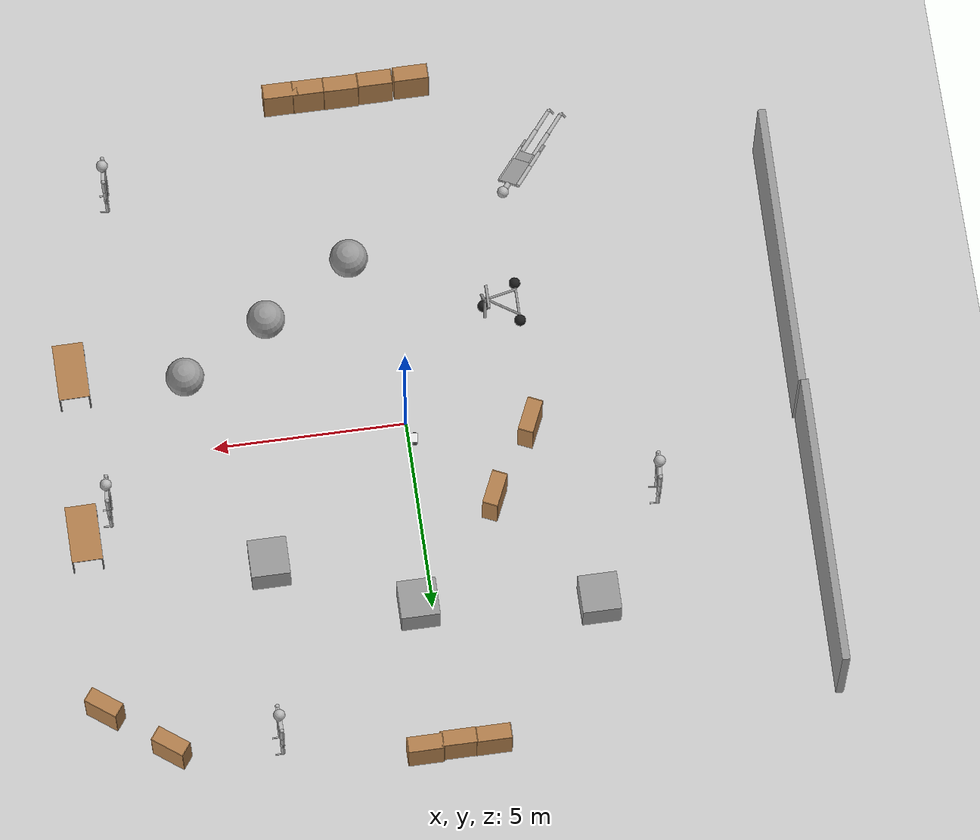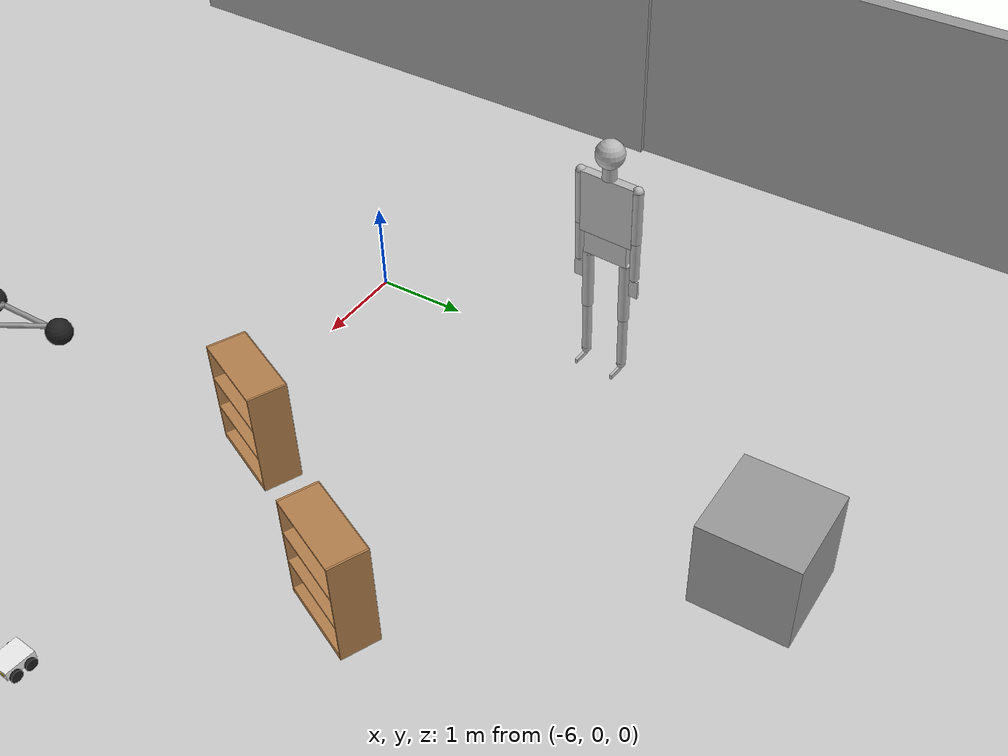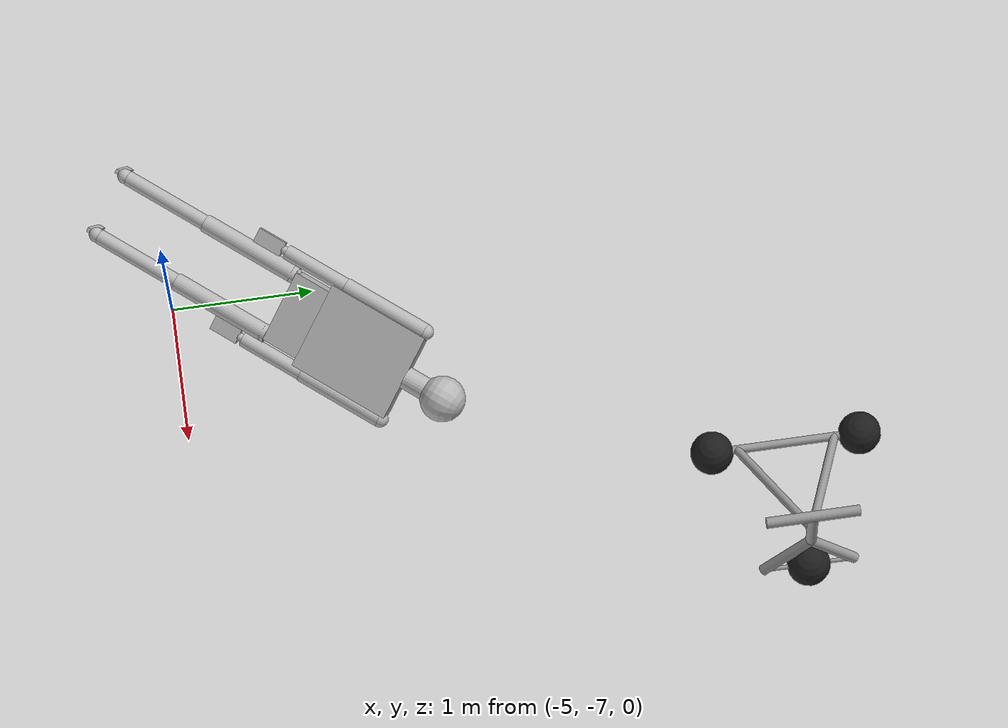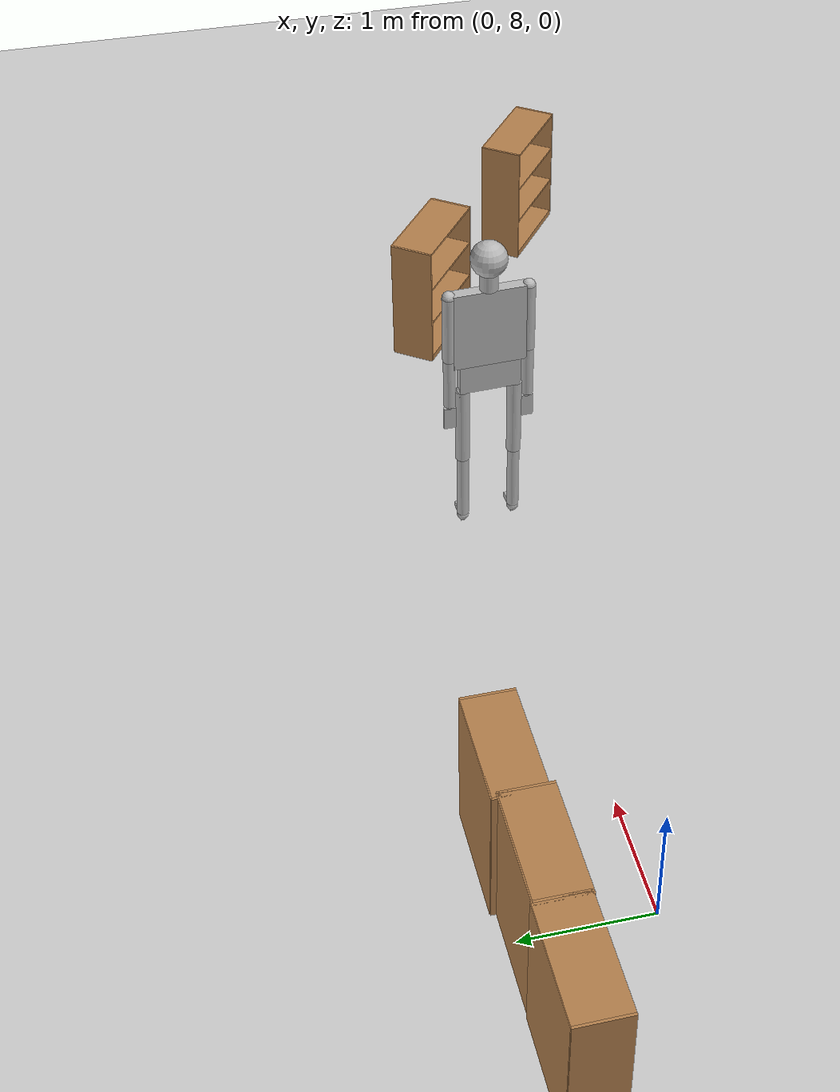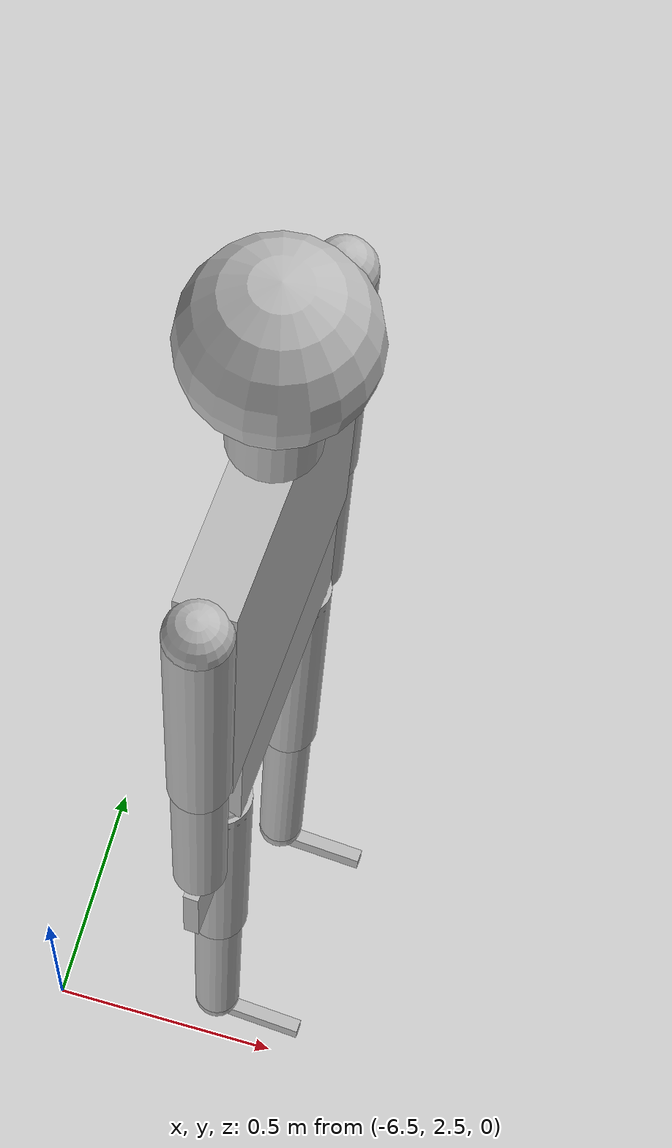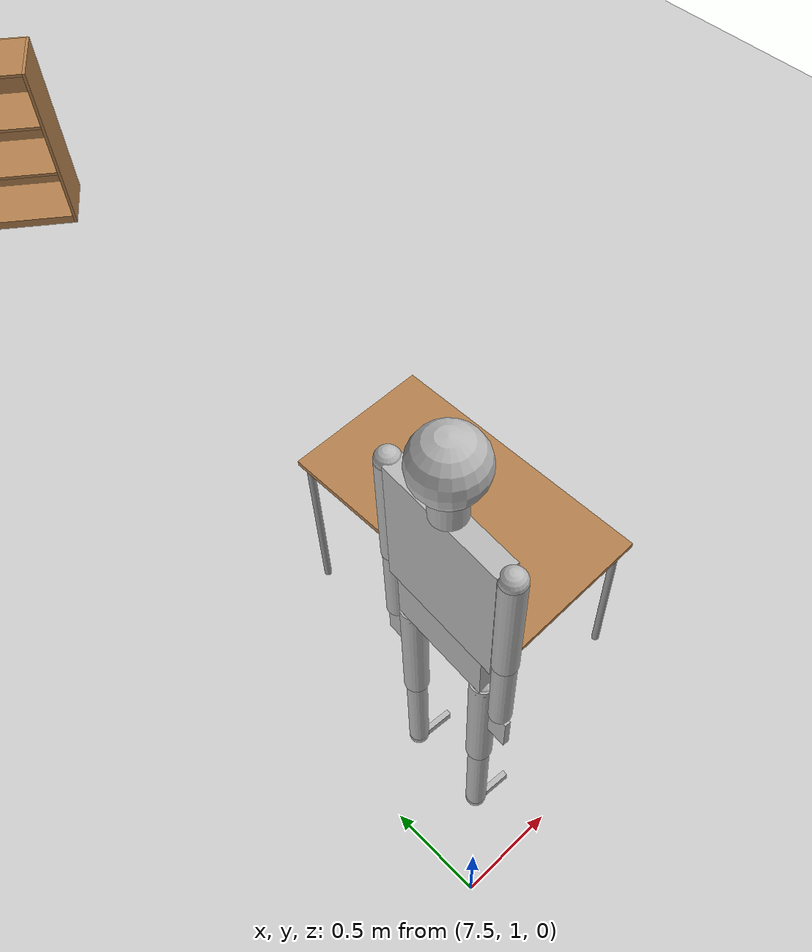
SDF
<sdf version="1.7">
 <world name="default">
  <light name="sun" type="directional">
   <pose>0 0 10 0 -0 0</pose>
   <diffuse>0.8 0.8 0.8 1</diffuse>
   <specular>0.2 0.2 0.2 1</specular>
   <attenuation>
    <range>1000</range>
    <constant>0.9</constant>
    <linear>0.01</linear>
    <quadratic>0.001</quadratic>
   </attenuation>
   <direction>-0.5 0.1 -0.9</direction>
   <spot><inner_angle>0</inner_angle><outer_angle>0</outer_angle><falloff>0</falloff></spot>
  </light>
  <model name="ground_plane">
   <static>1</static>
   <link name="link">
    <collision name="collision">
     <geometry><plane><normal>0 0 1</normal><size>100 100</size></plane></geometry>
     <surface>
      <contact><collide_bitmask>65535</collide_bitmask></contact>
      <friction><ode><mu>100</mu><mu2>50</mu2></ode></friction>
     </surface>
    </collision>
    <visual name="visual">
     <cast_shadows>0</cast_shadows>
     <geometry><plane><normal>0 0 1</normal><size>100 100</size></plane></geometry>
     <material>
      <script><uri>file://media/materials/scripts/gazebo.material</uri><name>Gazebo/Grey</name></script>
     </material>
    </visual>
   </link>
  </model>
  <gravity>0 0 -9.8</gravity>
  <magnetic_field>6e-06 2.3e-05 -4.2e-05</magnetic_field>
  <atmosphere type="adiabatic"/>
  <physics type="ode">
   <max_step_size>0.001</max_step_size>
   <real_time_factor>1</real_time_factor>
   <real_time_update_rate>1000</real_time_update_rate>
  </physics>
  <scene><ambient>0.4 0.4 0.4 1</ambient><background>0.7 0.7 0.7 1</background><shadows>1</shadows></scene>
  <audio><device>default</device></audio>
  <spherical_coordinates>
   <surface_model>EARTH_WGS84</surface_model>
   <latitude_deg>0</latitude_deg>
   <longitude_deg>0</longitude_deg>
   <elevation>0</elevation>
   <heading_deg>0</heading_deg>
  </spherical_coordinates>
  <model name="my_robot">
   <link name="base_footprint">
    <inertial>
     <pose>0.010714 0 0.098571 0 -0 0</pose>
     <mass>7</mass>
     <inertia>
      <ixx>0.0713607</ixx>
      <ixy>0</ixy>
      <ixz>0.00289286</ixz>
      <iyy>0.0436571</iyy>
      <iyz>-1.16852e-19</iyz>
      <izz>0.101646</izz>
     </inertia>
    </inertial>
    <collision name="base_footprint_fixed_joint_lump__base_link_collision">
     <pose>0 0 0.105 0 -0 0</pose>
     <geometry><box><size>0.3 0.25 0.09</size></box></geometry>
    </collision>
    <collision name="base_footprint_fixed_joint_lump__left_camera_link_collision_1">
     <pose>0.1525 0.075 0.11 0 -0 0</pose>
     <geometry><box><size>0.005 0.05 0.03</size></box></geometry>
    </collision>
    <collision name="base_footprint_fixed_joint_lump__left_wheel_front_link_collision_2">
     <pose>0.075 0.14 0.06 1.5708 -0 0</pose>
     <geometry><cylinder><length>0.03</length><radius>0.06</radius></cylinder></geometry>
     <surface><friction><ode><mu>0</mu><mu2>0</mu2></ode></friction></surface>
    </collision>
    <collision name="base_footprint_fixed_joint_lump__right_camera_link_collision_3">
     <pose>0.1525 -0.075 0.11 0 -0 0</pose>
     <geometry><box><size>0.005 0.05 0.03</size></box></geometry>
    </collision>
    <collision name="base_footprint_fixed_joint_lump__right_wheel_front_link_collision_4">
     <pose>0.075 -0.14 0.06 1.5708 -0 0</pose>
     <geometry><cylinder><length>0.03</length><radius>0.06</radius></cylinder></geometry>
     <surface><friction><ode><mu>0</mu><mu2>0</mu2></ode></friction></surface>
    </collision>
    <visual name="base_footprint_fixed_joint_lump__base_link_visual">
     <pose>0 0 0.105 0 -0 0</pose>
     <geometry><box><size>0.3 0.25 0.09</size></box></geometry>
     <material>
      <script><name>Gazebo/White</name><uri>file://media/materials/scripts/gazebo.material</uri></script>
     </material>
    </visual>
    <visual name="base_footprint_fixed_joint_lump__left_camera_link_visual_1">
     <pose>0.1525 0.075 0.11 0 -0 0</pose>
     <geometry><box><size>0.005 0.05 0.03</size></box></geometry>
     <material>
      <script><name>Gazebo/Gold</name><uri>file://media/materials/scripts/gazebo.material</uri></script>
     </material>
    </visual>
    <visual name="base_footprint_fixed_joint_lump__left_wheel_front_link_visual_2">
     <pose>0.075 0.14 0.06 1.5708 -0 0</pose>
     <geometry><cylinder><length>0.03</length><radius>0.06</radius></cylinder></geometry>
     <material>
      <script><name>Gazebo/Black</name><uri>file://media/materials/scripts/gazebo.material</uri></script>
     </material>
    </visual>
    <visual name="base_footprint_fixed_joint_lump__right_camera_link_visual_3">
     <pose>0.1525 -0.075 0.11 0 -0 0</pose>
     <geometry><box><size>0.005 0.05 0.03</size></box></geometry>
     <material>
      <script><name>Gazebo/Gold</name><uri>file://media/materials/scripts/gazebo.material</uri></script>
     </material>
    </visual>
    <visual name="base_footprint_fixed_joint_lump__right_wheel_front_link_visual_4">
     <pose>0.075 -0.14 0.06 1.5708 -0 0</pose>
     <geometry><cylinder><length>0.03</length><radius>0.06</radius></cylinder></geometry>
     <material>
      <script><name>Gazebo/Black</name><uri>file://media/materials/scripts/gazebo.material</uri></script>
     </material>
    </visual>
    <sensor name="left_camera_sensor" type="camera">
     <visualize>1</visualize>
     <update_rate>15</update_rate>
     <camera>
      <horizontal_fov>2.0944</horizontal_fov>
      <image><width>752</width><height>480</height><format>R8G8B8</format></image>
      <clip><near>0.1</near><far>100</far></clip>
      <distortion><k1>0</k1><k2>0</k2><k3>0</k3><p1>0</p1><p2>0</p2><center>376.5 240.5</center></distortion>
      <intrinsics><fx>217.08247</fx><fy>217.08247</fy><cx>376.5</cx><cy>240.5</cy></intrinsics>
     </camera>
     <plugin name="left_camera_controller" filename="libgazebo_ros_camera.so">
      <frame_name>left_camera_optical_link</frame_name>
      <camera_name>left_camera</camera_name>
      <image_width>752</image_width>
      <image_height>480</image_height>
      <ros>
       <namespace>/camera/left</namespace>
       <remapping>image_raw:=image</remapping>
       <parameter name="publish_image">1</parameter>
       <parameter name="publish_compressed">0</parameter>
       <parameter name="publish_depth">0</parameter>
       <parameter name="disable_pub_plugins">["compressed", "compressedDepth", "theora"]</parameter>
      </ros>
     </plugin>
     <pose>0.1525 0.075 0.11 0 -0 0</pose>
    </sensor>
    <sensor name="right_camera_sensor" type="camera">
     <visualize>1</visualize>
     <update_rate>15</update_rate>
     <camera>
      <horizontal_fov>2.0944</horizontal_fov>
      <image><width>752</width><height>480</height><format>R8G8B8</format></image>
      <clip><near>0.1</near><far>100</far></clip>
      <distortion><k1>0</k1><k2>0</k2><k3>0</k3><p1>0</p1><p2>0</p2><center>376.5 240.5</center></distortion>
      <intrinsics><fx>217.08247</fx><fy>217.08247</fy><cx>376.5</cx><cy>240.5</cy></intrinsics>
     </camera>
     <plugin name="right_camera_controller" filename="libgazebo_ros_camera.so">
      <frame_name>right_camera_optical_link</frame_name>
      <camera_name>right_camera</camera_name>
      <image_width>752</image_width>
      <image_height>480</image_height>
      <ros>
       <namespace>/camera/right</namespace>
       <remapping>image_raw:=image</remapping>
       <parameter name="publish_image">1</parameter>
       <parameter name="publish_compressed">0</parameter>
       <parameter name="publish_depth">0</parameter>
       <parameter name="disable_pub_plugins">["compressed", "compressedDepth", "theora"]</parameter>
      </ros>
     </plugin>
     <pose>0.1525 -0.075 0.11 0 -0 0</pose>
    </sensor>
   </link>
   <joint name="base_left_wheel_back_joint" type="revolute">
    <pose relative_to="base_footprint">-0.075 0.14 0.06 0 -0 0</pose>
    <parent>base_footprint</parent>
    <child>left_wheel_back_link</child>
    <axis>
     <xyz>0 1 0</xyz>
     <limit><effort>10</effort><velocity>10</velocity><lower>-1e+16</lower><upper>1e+16</upper></limit>
     <dynamics><spring_reference>0</spring_reference><spring_stiffness>0</spring_stiffness></dynamics>
    </axis>
   </joint>
   <link name="left_wheel_back_link">
    <pose relative_to="base_left_wheel_back_joint">0 0 0 0 -0 0</pose>
    <inertial>
     <pose>0 0 0 1.5708 -0 0</pose>
     <mass>0.5</mass>
     <inertia>
      <ixx>0.0004875</ixx>
      <ixy>0</ixy>
      <ixz>0</ixz>
      <iyy>0.0004875</iyy>
      <iyz>0</iyz>
      <izz>0.0009</izz>
     </inertia>
    </inertial>
    <collision name="left_wheel_back_link_collision">
     <pose>0 0 0 1.5708 -0 0</pose>
     <geometry><cylinder><length>0.03</length><radius>0.06</radius></cylinder></geometry>
    </collision>
    <visual name="left_wheel_back_link_visual">
     <pose>0 0 0 1.5708 -0 0</pose>
     <geometry><cylinder><length>0.03</length><radius>0.06</radius></cylinder></geometry>
     <material>
      <script><name>Gazebo/Black</name><uri>file://media/materials/scripts/gazebo.material</uri></script>
     </material>
    </visual>
   </link>
   <joint name="base_right_wheel_back_joint" type="revolute">
    <pose relative_to="base_footprint">-0.075 -0.14 0.06 0 -0 0</pose>
    <parent>base_footprint</parent>
    <child>right_wheel_back_link</child>
    <axis>
     <xyz>0 1 0</xyz>
     <limit><effort>10</effort><velocity>10</velocity><lower>-1e+16</lower><upper>1e+16</upper></limit>
     <dynamics><spring_reference>0</spring_reference><spring_stiffness>0</spring_stiffness></dynamics>
    </axis>
   </joint>
   <link name="right_wheel_back_link">
    <pose relative_to="base_right_wheel_back_joint">0 0 0 0 -0 0</pose>
    <inertial>
     <pose>0 0 0 1.5708 -0 0</pose>
     <mass>0.5</mass>
     <inertia>
      <ixx>0.0004875</ixx>
      <ixy>0</ixy>
      <ixz>0</ixz>
      <iyy>0.0004875</iyy>
      <iyz>0</iyz>
      <izz>0.0009</izz>
     </inertia>
    </inertial>
    <collision name="right_wheel_back_link_collision">
     <pose>0 0 0 1.5708 -0 0</pose>
     <geometry><cylinder><length>0.03</length><radius>0.06</radius></cylinder></geometry>
    </collision>
    <visual name="right_wheel_back_link_visual">
     <pose>0 0 0 1.5708 -0 0</pose>
     <geometry><cylinder><length>0.03</length><radius>0.06</radius></cylinder></geometry>
     <material>
      <script><name>Gazebo/Black</name><uri>file://media/materials/scripts/gazebo.material</uri></script>
     </material>
    </visual>
   </link>
   <static>0</static>
   <plugin name="diff_drive_controller" filename="libgazebo_ros_diff_drive.so">
    <update_rate>50</update_rate>
    <left_joint>base_left_wheel_back_joint</left_joint>
    <right_joint>base_right_wheel_back_joint</right_joint>
    <wheel_separation>0.28</wheel_separation>
    <wheel_diameter>0.12</wheel_diameter>
    <publish_odom>1</publish_odom>
    <publish_odom_tf>1</publish_odom_tf>
    <publish_wheel_tf>1</publish_wheel_tf>
    <odometry_topic>odom</odometry_topic>
    <odometry_frame>odom</odometry_frame>
    <robot_base_frame>base_footprint</robot_base_frame>
    <ros><namespace>/</namespace><remapping>cmd_vel:=cmd_vel</remapping><remapping>odom:=odom</remapping></ros>
    <max_wheel_torque>200</max_wheel_torque>
    <max_wheel_acceleration>10.0</max_wheel_acceleration>
    <command_topic>cmd_vel</command_topic>
   </plugin>
   <pose>-0.087835 0.442639 1e-06 -4e-06 3e-06 -0.090374</pose>
  </model>
  <model name="table">
   <static>1</static>
   <link name="link">
    <collision name="surface">
     <pose>0 0 1 0 -0 0</pose>
     <geometry><box><size>1.5 0.8 0.03</size></box></geometry>
     <surface><friction><ode><mu>0.6</mu><mu2>0.6</mu2></ode></friction></surface>
    </collision>
    <visual name="visual1">
     <pose>0 0 1 0 -0 0</pose>
     <geometry><box><size>1.5 0.8 0.03</size></box></geometry>
     <material>
      <script><uri>file://media/materials/scripts/gazebo.material</uri><name>Gazebo/Wood</name></script>
     </material>
    </visual>
    <collision name="front_left_leg">
     <pose>0.68 0.38 0.5 0 -0 0</pose>
     <geometry><cylinder><radius>0.02</radius><length>1</length></cylinder></geometry>
    </collision>
    <visual name="front_left_leg">
     <pose>0.68 0.38 0.5 0 -0 0</pose>
     <geometry><cylinder><radius>0.02</radius><length>1</length></cylinder></geometry>
     <material>
      <script><uri>file://media/materials/scripts/gazebo.material</uri><name>Gazebo/Grey</name></script>
     </material>
    </visual>
    <collision name="front_right_leg">
     <pose>0.68 -0.38 0.5 0 -0 0</pose>
     <geometry><cylinder><radius>0.02</radius><length>1</length></cylinder></geometry>
    </collision>
    <visual name="front_right_leg">
     <pose>0.68 -0.38 0.5 0 -0 0</pose>
     <geometry><cylinder><radius>0.02</radius><length>1</length></cylinder></geometry>
     <material>
      <script><uri>file://media/materials/scripts/gazebo.material</uri><name>Gazebo/Grey</name></script>
     </material>
    </visual>
    <collision name="back_right_leg">
     <pose>-0.68 -0.38 0.5 0 -0 0</pose>
     <geometry><cylinder><radius>0.02</radius><length>1</length></cylinder></geometry>
    </collision>
    <visual name="back_right_leg">
     <pose>-0.68 -0.38 0.5 0 -0 0</pose>
     <geometry><cylinder><radius>0.02</radius><length>1</length></cylinder></geometry>
     <material>
      <script><uri>file://media/materials/scripts/gazebo.material</uri><name>Gazebo/Grey</name></script>
     </material>
    </visual>
    <collision name="back_left_leg">
     <pose>-0.68 0.38 0.5 0 -0 0</pose>
     <geometry><cylinder><radius>0.02</radius><length>1</length></cylinder></geometry>
    </collision>
    <visual name="back_left_leg">
     <pose>-0.68 0.38 0.5 0 -0 0</pose>
     <geometry><cylinder><radius>0.02</radius><length>1</length></cylinder></geometry>
     <material>
      <script><uri>file://media/materials/scripts/gazebo.material</uri><name>Gazebo/Grey</name></script>
     </material>
    </visual>
   </link>
   <pose>8.3915 -2.25224 0 0 -0 1.58235</pose>
  </model>
  <model name="table_clone">
   <static>1</static>
   <link name="link">
    <collision name="surface">
     <pose>0 0 1 0 -0 0</pose>
     <geometry><box><size>1.5 0.8 0.03</size></box></geometry>
     <surface><friction><ode><mu>0.6</mu><mu2>0.6</mu2></ode></friction></surface>
    </collision>
    <visual name="visual1">
     <pose>0 0 1 0 -0 0</pose>
     <geometry><box><size>1.5 0.8 0.03</size></box></geometry>
     <material>
      <script><uri>file://media/materials/scripts/gazebo.material</uri><name>Gazebo/Wood</name></script>
     </material>
    </visual>
    <collision name="front_left_leg">
     <pose>0.68 0.38 0.5 0 -0 0</pose>
     <geometry><cylinder><radius>0.02</radius><length>1</length></cylinder></geometry>
    </collision>
    <visual name="front_left_leg">
     <pose>0.68 0.38 0.5 0 -0 0</pose>
     <geometry><cylinder><radius>0.02</radius><length>1</length></cylinder></geometry>
     <material>
      <script><uri>file://media/materials/scripts/gazebo.material</uri><name>Gazebo/Grey</name></script>
     </material>
    </visual>
    <collision name="front_right_leg">
     <pose>0.68 -0.38 0.5 0 -0 0</pose>
     <geometry><cylinder><radius>0.02</radius><length>1</length></cylinder></geometry>
    </collision>
    <visual name="front_right_leg">
     <pose>0.68 -0.38 0.5 0 -0 0</pose>
     <geometry><cylinder><radius>0.02</radius><length>1</length></cylinder></geometry>
     <material>
      <script><uri>file://media/materials/scripts/gazebo.material</uri><name>Gazebo/Grey</name></script>
     </material>
    </visual>
    <collision name="back_right_leg">
     <pose>-0.68 -0.38 0.5 0 -0 0</pose>
     <geometry><cylinder><radius>0.02</radius><length>1</length></cylinder></geometry>
    </collision>
    <visual name="back_right_leg">
     <pose>-0.68 -0.38 0.5 0 -0 0</pose>
     <geometry><cylinder><radius>0.02</radius><length>1</length></cylinder></geometry>
     <material>
      <script><uri>file://media/materials/scripts/gazebo.material</uri><name>Gazebo/Grey</name></script>
     </material>
    </visual>
    <collision name="back_left_leg">
     <pose>-0.68 0.38 0.5 0 -0 0</pose>
     <geometry><cylinder><radius>0.02</radius><length>1</length></cylinder></geometry>
    </collision>
    <visual name="back_left_leg">
     <pose>-0.68 0.38 0.5 0 -0 0</pose>
     <geometry><cylinder><radius>0.02</radius><length>1</length></cylinder></geometry>
     <material>
      <script><uri>file://media/materials/scripts/gazebo.material</uri><name>Gazebo/Grey</name></script>
     </material>
    </visual>
   </link>
   <pose>8.57439 2.15783 0 0 -0 1.58235</pose>
  </model>
  <model name="ragdoll">
   <pose>-4.03499 -6.22908 1.9802 1.65595 0.975455 2.52129</pose>
   <link name="hip">
    <inertial>
     <inertia><ixx>0.1</ixx><ixy>0</ixy><ixz>0</ixz><iyy>0.1</iyy><iyz>0</iyz><izz>0.1</izz></inertia>
     <mass>10</mass>
    </inertial>
    <collision name="hip_geom">
     <pose>0 0 0.125 0 -0 0</pose>
     <geometry><box><size>0.1 0.5 0.25</size></box></geometry>
     <surface>
      <friction><ode><mu>-1</mu><mu2>-1</mu2><fdir1>0 0 0</fdir1><slip1>0</slip1><slip2>0</slip2></ode></friction>
      <bounce><restitution_coefficient>0</restitution_coefficient><threshold>100000</threshold></bounce>
      <contact>
       <ode>
        <soft_cfm>0</soft_cfm>
        <soft_erp>0.2</soft_erp>
        <kp>1e+12</kp>
        <kd>1</kd>
        <max_vel>0</max_vel>
        <min_depth>0.001</min_depth>
       </ode>
      </contact>
     </surface>
    </collision>
    <visual name="hip_geom_visual">
     <pose>0 0 0.125 0 -0 0</pose>
     <geometry><box><size>0.1 0.5 0.25</size></box></geometry>
    </visual>
    <gravity>0</gravity>
   </link>
   <link name="l_thigh_pan">
    <pose>0 0.22 0 0 -0 0</pose>
    <inertial>
     <inertia><ixx>0.01</ixx><ixy>0</ixy><ixz>0</ixz><iyy>0.01</iyy><iyz>0</iyz><izz>0.01</izz></inertia>
     <mass>1</mass>
    </inertial>
    <collision name="l_thigh_pan_geom">
     <pose>0 0 -0.03 0 -0 0</pose>
     <geometry><sphere><radius>0.06</radius></sphere></geometry>
     <surface>
      <friction><ode><mu>-1</mu><mu2>-1</mu2><fdir1>0 0 0</fdir1><slip1>0</slip1><slip2>0</slip2></ode></friction>
      <bounce><restitution_coefficient>0</restitution_coefficient><threshold>100000</threshold></bounce>
      <contact>
       <ode>
        <soft_cfm>0</soft_cfm>
        <soft_erp>0.2</soft_erp>
        <kp>1e+12</kp>
        <kd>1</kd>
        <max_vel>0</max_vel>
        <min_depth>0.001</min_depth>
       </ode>
      </contact>
     </surface>
    </collision>
    <visual name="l_thigh_pan_geom_visual">
     <pose>0 0 -0.03 0 -0 0</pose>
     <geometry><sphere><radius>0.06</radius></sphere></geometry>
    </visual>
    <gravity>0</gravity>
   </link>
   <link name="l_thigh_lift">
    <pose>0 0.22 0 0 -0 0</pose>
    <inertial>
     <inertia><ixx>0.05</ixx><ixy>0</ixy><ixz>0</ixz><iyy>0.05</iyy><iyz>0</iyz><izz>0.05</izz></inertia>
     <mass>5</mass>
    </inertial>
    <collision name="l_thigh_lift_geom">
     <pose>0 0 -0.35 0 -0 0</pose>
     <geometry><cylinder><radius>0.06</radius><length>0.7</length></cylinder></geometry>
     <surface>
      <friction><ode><mu>-1</mu><mu2>-1</mu2><fdir1>0 0 0</fdir1><slip1>0</slip1><slip2>0</slip2></ode></friction>
      <bounce><restitution_coefficient>0</restitution_coefficient><threshold>100000</threshold></bounce>
      <contact>
       <ode>
        <soft_cfm>0</soft_cfm>
        <soft_erp>0.2</soft_erp>
        <kp>1e+12</kp>
        <kd>1</kd>
        <max_vel>0</max_vel>
        <min_depth>0.001</min_depth>
       </ode>
      </contact>
     </surface>
    </collision>
    <visual name="l_thigh_lift_geom_visual">
     <pose>0 0 -0.35 0 -0 0</pose>
     <geometry><cylinder><radius>0.06</radius><length>0.7</length></cylinder></geometry>
    </visual>
    <gravity>0</gravity>
   </link>
   <link name="l_calf">
    <pose>0 0.22 -0.7 0 -0 0</pose>
    <inertial>
     <inertia><ixx>0.02</ixx><ixy>0</ixy><ixz>0</ixz><iyy>0.02</iyy><iyz>0</iyz><izz>0.02</izz></inertia>
     <mass>2</mass>
    </inertial>
    <collision name="l_calf_geom">
     <pose>0 0 -0.3 0 -0 0</pose>
     <geometry><cylinder><radius>0.05</radius><length>0.6</length></cylinder></geometry>
     <surface>
      <friction><ode><mu>-1</mu><mu2>-1</mu2><fdir1>0 0 0</fdir1><slip1>0</slip1><slip2>0</slip2></ode></friction>
      <bounce><restitution_coefficient>0</restitution_coefficient><threshold>100000</threshold></bounce>
      <contact>
       <ode>
        <soft_cfm>0</soft_cfm>
        <soft_erp>0.2</soft_erp>
        <kp>1e+12</kp>
        <kd>1</kd>
        <max_vel>0</max_vel>
        <min_depth>0.001</min_depth>
       </ode>
      </contact>
     </surface>
    </collision>
    <visual name="l_calf_geom_visual">
     <pose>0 0 -0.3 0 -0 0</pose>
     <geometry><cylinder><radius>0.05</radius><length>0.6</length></cylinder></geometry>
    </visual>
    <gravity>0</gravity>
   </link>
   <link name="l_ankle">
    <pose>0 0.22 -1.325 0 -0 0</pose>
    <inertial>
     <inertia><ixx>0.01</ixx><ixy>0</ixy><ixz>0</ixz><iyy>0.01</iyy><iyz>0</iyz><izz>0.01</izz></inertia>
     <mass>1</mass>
    </inertial>
    <collision name="l_ankle_geom">
     <geometry><sphere><radius>0.05</radius></sphere></geometry>
     <surface>
      <friction><ode><mu>-1</mu><mu2>-1</mu2><fdir1>0 0 0</fdir1><slip1>0</slip1><slip2>0</slip2></ode></friction>
      <bounce><restitution_coefficient>0</restitution_coefficient><threshold>100000</threshold></bounce>
      <contact>
       <ode>
        <soft_cfm>0</soft_cfm>
        <soft_erp>0.2</soft_erp>
        <kp>1e+12</kp>
        <kd>1</kd>
        <max_vel>0</max_vel>
        <min_depth>0.001</min_depth>
       </ode>
      </contact>
     </surface>
    </collision>
    <visual name="l_ankle_geom_visual"><geometry><sphere><radius>0.05</radius></sphere></geometry></visual>
    <gravity>0</gravity>
   </link>
   <link name="l_foot">
    <pose>0 0.22 -1.35 0 -0 0</pose>
    <inertial>
     <pose>0.1 0 0 0 -0 0</pose>
     <inertia><ixx>0.01</ixx><ixy>0</ixy><ixz>0</ixz><iyy>0.01</iyy><iyz>0</iyz><izz>0.01</izz></inertia>
     <mass>1</mass>
    </inertial>
    <collision name="l_foot_geom">
     <pose>0.1 0 -0.025 0 -0 0</pose>
     <geometry><box><size>0.2 0.03 0.05</size></box></geometry>
     <surface>
      <friction><ode><mu>-1</mu><mu2>-1</mu2><fdir1>0 0 0</fdir1><slip1>0</slip1><slip2>0</slip2></ode></friction>
      <bounce><restitution_coefficient>0</restitution_coefficient><threshold>100000</threshold></bounce>
      <contact>
       <ode>
        <soft_cfm>0</soft_cfm>
        <soft_erp>0.2</soft_erp>
        <kp>1e+12</kp>
        <kd>1</kd>
        <max_vel>0</max_vel>
        <min_depth>0.001</min_depth>
       </ode>
      </contact>
     </surface>
    </collision>
    <visual name="l_foot_geom_visual">
     <pose>0.1 0 -0.025 0 -0 0</pose>
     <geometry><box><size>0.2 0.03 0.05</size></box></geometry>
    </visual>
   </link>
   <link name="r_thigh_pan">
    <pose>0 -0.22 0 0 -0 0</pose>
    <inertial>
     <inertia><ixx>0.01</ixx><ixy>0</ixy><ixz>0</ixz><iyy>0.01</iyy><iyz>0</iyz><izz>0.01</izz></inertia>
     <mass>1</mass>
    </inertial>
    <collision name="r_thigh_pan_geom">
     <pose>0 0 -0.03 0 -0 0</pose>
     <geometry><sphere><radius>0.06</radius></sphere></geometry>
     <surface>
      <friction><ode><mu>-1</mu><mu2>-1</mu2><fdir1>0 0 0</fdir1><slip1>0</slip1><slip2>0</slip2></ode></friction>
      <bounce><restitution_coefficient>0</restitution_coefficient><threshold>100000</threshold></bounce>
      <contact>
       <ode>
        <soft_cfm>0</soft_cfm>
        <soft_erp>0.2</soft_erp>
        <kp>1e+12</kp>
        <kd>1</kd>
        <max_vel>0</max_vel>
        <min_depth>0.001</min_depth>
       </ode>
      </contact>
     </surface>
    </collision>
    <visual name="r_thigh_pan_geom_visual">
     <pose>0 0 -0.03 0 -0 0</pose>
     <geometry><sphere><radius>0.06</radius></sphere></geometry>
    </visual>
    <gravity>0</gravity>
   </link>
   <link name="r_thigh_lift">
    <pose>0 -0.22 0 0 -0 0</pose>
    <inertial>
     <inertia><ixx>0.05</ixx><ixy>0</ixy><ixz>0</ixz><iyy>0.05</iyy><iyz>0</iyz><izz>0.05</izz></inertia>
     <mass>5</mass>
    </inertial>
    <collision name="r_thigh_lift_geom">
     <pose>0 0 -0.35 0 -0 0</pose>
     <geometry><cylinder><radius>0.06</radius><length>0.7</length></cylinder></geometry>
     <surface>
      <friction><ode><mu>-1</mu><mu2>-1</mu2><fdir1>0 0 0</fdir1><slip1>0</slip1><slip2>0</slip2></ode></friction>
      <bounce><restitution_coefficient>0</restitution_coefficient><threshold>100000</threshold></bounce>
      <contact>
       <ode>
        <soft_cfm>0</soft_cfm>
        <soft_erp>0.2</soft_erp>
        <kp>1e+12</kp>
        <kd>1</kd>
        <max_vel>0</max_vel>
        <min_depth>0.001</min_depth>
       </ode>
      </contact>
     </surface>
    </collision>
    <visual name="r_thigh_lift_geom_visual">
     <pose>0 0 -0.35 0 -0 0</pose>
     <geometry><cylinder><radius>0.06</radius><length>0.7</length></cylinder></geometry>
    </visual>
    <gravity>0</gravity>
   </link>
   <link name="r_calf">
    <pose>0 -0.22 -0.7 0 -0 0</pose>
    <inertial>
     <inertia><ixx>0.02</ixx><ixy>0</ixy><ixz>0</ixz><iyy>0.02</iyy><iyz>0</iyz><izz>0.02</izz></inertia>
     <mass>2</mass>
    </inertial>
    <collision name="r_calf_geom">
     <pose>0 0 -0.3 0 -0 0</pose>
     <geometry><cylinder><radius>0.05</radius><length>0.6</length></cylinder></geometry>
     <surface>
      <friction><ode><mu>-1</mu><mu2>-1</mu2><fdir1>0 0 0</fdir1><slip1>0</slip1><slip2>0</slip2></ode></friction>
      <bounce><restitution_coefficient>0</restitution_coefficient><threshold>100000</threshold></bounce>
      <contact>
       <ode>
        <soft_cfm>0</soft_cfm>
        <soft_erp>0.2</soft_erp>
        <kp>1e+12</kp>
        <kd>1</kd>
        <max_vel>0</max_vel>
        <min_depth>0.001</min_depth>
       </ode>
      </contact>
     </surface>
    </collision>
    <visual name="r_calf_geom_visual">
     <pose>0 0 -0.3 0 -0 0</pose>
     <geometry><cylinder><radius>0.05</radius><length>0.6</length></cylinder></geometry>
    </visual>
    <gravity>0</gravity>
   </link>
   <link name="r_ankle">
    <pose>0 -0.22 -1.325 0 -0 0</pose>
    <inertial>
     <inertia><ixx>0.01</ixx><ixy>0</ixy><ixz>0</ixz><iyy>0.01</iyy><iyz>0</iyz><izz>0.01</izz></inertia>
     <mass>1</mass>
    </inertial>
    <collision name="r_ankle_geom">
     <geometry><sphere><radius>0.05</radius></sphere></geometry>
     <surface>
      <friction><ode><mu>-1</mu><mu2>-1</mu2><fdir1>0 0 0</fdir1><slip1>0</slip1><slip2>0</slip2></ode></friction>
      <bounce><restitution_coefficient>0</restitution_coefficient><threshold>100000</threshold></bounce>
      <contact>
       <ode>
        <soft_cfm>0</soft_cfm>
        <soft_erp>0.2</soft_erp>
        <kp>1e+12</kp>
        <kd>1</kd>
        <max_vel>0</max_vel>
        <min_depth>0.001</min_depth>
       </ode>
      </contact>
     </surface>
    </collision>
    <visual name="r_ankle_geom_visual"><geometry><sphere><radius>0.05</radius></sphere></geometry></visual>
    <gravity>0</gravity>
   </link>
   <link name="r_foot">
    <pose>0 -0.22 -1.35 0 -0 0</pose>
    <inertial>
     <pose>0.1 0 0 0 -0 0</pose>
     <inertia><ixx>0.01</ixx><ixy>0</ixy><ixz>0</ixz><iyy>0.01</iyy><iyz>0</iyz><izz>0.01</izz></inertia>
     <mass>1</mass>
    </inertial>
    <collision name="r_foot_geom">
     <pose>0.1 0 -0.025 0 -0 0</pose>
     <geometry><box><size>0.2 0.03 0.05</size></box></geometry>
     <surface>
      <friction><ode><mu>-1</mu><mu2>-1</mu2><fdir1>0 0 0</fdir1><slip1>0</slip1><slip2>0</slip2></ode></friction>
      <bounce><restitution_coefficient>0</restitution_coefficient><threshold>100000</threshold></bounce>
      <contact>
       <ode>
        <soft_cfm>0</soft_cfm>
        <soft_erp>0.2</soft_erp>
        <kp>1e+12</kp>
        <kd>1</kd>
        <max_vel>0</max_vel>
        <min_depth>0.001</min_depth>
       </ode>
      </contact>
     </surface>
    </collision>
    <visual name="r_foot_geom_visual">
     <pose>0.1 0 -0.025 0 -0 0</pose>
     <geometry><box><size>0.2 0.03 0.05</size></box></geometry>
    </visual>
   </link>
   <link name="torso">
    <pose>0 0 0.25 0 -0 0</pose>
    <inertial>
     <inertia><ixx>0.3</ixx><ixy>0</ixy><ixz>0</ixz><iyy>0.3</iyy><iyz>0</iyz><izz>0.3</izz></inertia>
     <mass>30</mass>
    </inertial>
    <collision name="torso_geom">
     <pose>0 0 0.35 0 -0 0</pose>
     <geometry><box><size>0.1 0.6 0.7</size></box></geometry>
     <surface>
      <friction><ode><mu>-1</mu><mu2>-1</mu2><fdir1>0 0 0</fdir1><slip1>0</slip1><slip2>0</slip2></ode></friction>
      <bounce><restitution_coefficient>0</restitution_coefficient><threshold>100000</threshold></bounce>
      <contact>
       <ode>
        <soft_cfm>0</soft_cfm>
        <soft_erp>0.2</soft_erp>
        <kp>1e+12</kp>
        <kd>1</kd>
        <max_vel>0</max_vel>
        <min_depth>0.001</min_depth>
       </ode>
      </contact>
     </surface>
    </collision>
    <visual name="torso_geom_visual">
     <pose>0 0 0.35 0 -0 0</pose>
     <geometry><box><size>0.1 0.6 0.7</size></box></geometry>
    </visual>
    <gravity>0</gravity>
   </link>
   <link name="l_shoulder">
    <pose>0 0.3275 0.9225 0 -0 0</pose>
    <inertial>
     <inertia><ixx>0.01</ixx><ixy>0</ixy><ixz>0</ixz><iyy>0.01</iyy><iyz>0</iyz><izz>0.01</izz></inertia>
     <mass>1</mass>
    </inertial>
    <collision name="l_shoulder_geom">
     <geometry><sphere><radius>0.055</radius></sphere></geometry>
     <surface>
      <friction><ode><mu>-1</mu><mu2>-1</mu2><fdir1>0 0 0</fdir1><slip1>0</slip1><slip2>0</slip2></ode></friction>
      <bounce><restitution_coefficient>0</restitution_coefficient><threshold>100000</threshold></bounce>
      <contact>
       <ode>
        <soft_cfm>0</soft_cfm>
        <soft_erp>0.2</soft_erp>
        <kp>1e+12</kp>
        <kd>1</kd>
        <max_vel>0</max_vel>
        <min_depth>0.001</min_depth>
       </ode>
      </contact>
     </surface>
    </collision>
    <visual name="l_shoulder_geom_visual"><geometry><sphere><radius>0.055</radius></sphere></geometry></visual>
    <gravity>0</gravity>
   </link>
   <link name="l_upper_arm">
    <pose>0 0.3275 0.9225 0 -0 0</pose>
    <inertial>
     <inertia><ixx>0.02</ixx><ixy>0</ixy><ixz>0</ixz><iyy>0.02</iyy><iyz>0</iyz><izz>0.02</izz></inertia>
     <mass>2</mass>
    </inertial>
    <collision name="l_upper_arm_geom">
     <pose>0 0 -0.3 0 -0 0</pose>
     <geometry><cylinder><radius>0.055</radius><length>0.6</length></cylinder></geometry>
     <surface>
      <friction><ode><mu>-1</mu><mu2>-1</mu2><fdir1>0 0 0</fdir1><slip1>0</slip1><slip2>0</slip2></ode></friction>
      <bounce><restitution_coefficient>0</restitution_coefficient><threshold>100000</threshold></bounce>
      <contact>
       <ode>
        <soft_cfm>0</soft_cfm>
        <soft_erp>0.2</soft_erp>
        <kp>1e+12</kp>
        <kd>1</kd>
        <max_vel>0</max_vel>
        <min_depth>0.001</min_depth>
       </ode>
      </contact>
     </surface>
    </collision>
    <visual name="l_upper_arm_geom_visual">
     <pose>0 0 -0.3 0 -0 0</pose>
     <geometry><cylinder><radius>0.055</radius><length>0.6</length></cylinder></geometry>
    </visual>
    <gravity>0</gravity>
   </link>
   <link name="l_forearm">
    <pose>0 0.3275 0.3225 0 -0 0</pose>
    <inertial>
     <inertia><ixx>0.01</ixx><ixy>0</ixy><ixz>0</ixz><iyy>0.01</iyy><iyz>0</iyz><izz>0.01</izz></inertia>
     <mass>1</mass>
    </inertial>
    <collision name="l_forearm_geom">
     <pose>0 0 -0.225 0 -0 0</pose>
     <geometry><cylinder><radius>0.05</radius><length>0.45</length></cylinder></geometry>
     <surface>
      <friction><ode><mu>-1</mu><mu2>-1</mu2><fdir1>0 0 0</fdir1><slip1>0</slip1><slip2>0</slip2></ode></friction>
      <bounce><restitution_coefficient>0</restitution_coefficient><threshold>100000</threshold></bounce>
      <contact>
       <ode>
        <soft_cfm>0</soft_cfm>
        <soft_erp>0.2</soft_erp>
        <kp>1e+12</kp>
        <kd>1</kd>
        <max_vel>0</max_vel>
        <min_depth>0.001</min_depth>
       </ode>
      </contact>
     </surface>
    </collision>
    <visual name="l_forearm_geom_visual">
     <pose>0 0 -0.225 0 -0 0</pose>
     <geometry><cylinder><radius>0.05</radius><length>0.45</length></cylinder></geometry>
    </visual>
    <gravity>0</gravity>
   </link>
   <link name="l_wrist">
    <pose>0 0.3275 -0.1425 0 -0 0</pose>
    <inertial>
     <inertia><ixx>0.01</ixx><ixy>0</ixy><ixz>0</ixz><iyy>0.01</iyy><iyz>0</iyz><izz>0.01</izz></inertia>
     <mass>1</mass>
    </inertial>
    <collision name="l_wrist_geom">
     <geometry><sphere><radius>0.03</radius></sphere></geometry>
     <surface>
      <friction><ode><mu>-1</mu><mu2>-1</mu2><fdir1>0 0 0</fdir1><slip1>0</slip1><slip2>0</slip2></ode></friction>
      <bounce><restitution_coefficient>0</restitution_coefficient><threshold>100000</threshold></bounce>
      <contact>
       <ode>
        <soft_cfm>0</soft_cfm>
        <soft_erp>0.2</soft_erp>
        <kp>1e+12</kp>
        <kd>1</kd>
        <max_vel>0</max_vel>
        <min_depth>0.001</min_depth>
       </ode>
      </contact>
     </surface>
    </collision>
    <visual name="l_wrist_geom_visual"><geometry><sphere><radius>0.03</radius></sphere></geometry></visual>
    <gravity>0</gravity>
   </link>
   <link name="l_hand">
    <pose>0 0.3275 -0.1575 0 -0 0</pose>
    <inertial>
     <inertia><ixx>0.01</ixx><ixy>0</ixy><ixz>0</ixz><iyy>0.01</iyy><iyz>0</iyz><izz>0.01</izz></inertia>
     <mass>1</mass>
    </inertial>
    <collision name="l_hand_geom">
     <pose>0 0 -0.1 0 -0 0</pose>
     <geometry><box><size>0.03 0.1 0.2</size></box></geometry>
     <surface>
      <friction><ode><mu>-1</mu><mu2>-1</mu2><fdir1>0 0 0</fdir1><slip1>0</slip1><slip2>0</slip2></ode></friction>
      <bounce><restitution_coefficient>0</restitution_coefficient><threshold>100000</threshold></bounce>
      <contact>
       <ode>
        <soft_cfm>0</soft_cfm>
        <soft_erp>0.2</soft_erp>
        <kp>1e+12</kp>
        <kd>1</kd>
        <max_vel>0</max_vel>
        <min_depth>0.001</min_depth>
       </ode>
      </contact>
     </surface>
    </collision>
    <visual name="l_hand_geom_visual">
     <pose>0 0 -0.1 0 -0 0</pose>
     <geometry><box><size>0.03 0.1 0.2</size></box></geometry>
    </visual>
    <gravity>0</gravity>
   </link>
   <link name="neck">
    <pose>0 0 0.95 0 -0 0</pose>
    <inertial>
     <inertia><ixx>0.01</ixx><ixy>0</ixy><ixz>0</ixz><iyy>0.01</iyy><iyz>0</iyz><izz>0.01</izz></inertia>
     <mass>1</mass>
    </inertial>
    <collision name="neck_geom">
     <pose>0 0 0.1 0 -0 0</pose>
     <geometry><cylinder><radius>0.075</radius><length>0.2</length></cylinder></geometry>
     <surface>
      <friction><ode><mu>-1</mu><mu2>-1</mu2><fdir1>0 0 0</fdir1><slip1>0</slip1><slip2>0</slip2></ode></friction>
      <bounce><restitution_coefficient>0</restitution_coefficient><threshold>100000</threshold></bounce>
      <contact>
       <ode>
        <soft_cfm>0</soft_cfm>
        <soft_erp>0.2</soft_erp>
        <kp>1e+12</kp>
        <kd>1</kd>
        <max_vel>0</max_vel>
        <min_depth>0.001</min_depth>
       </ode>
      </contact>
     </surface>
    </collision>
    <visual name="neck_geom_visual">
     <pose>0 0 0.1 0 -0 0</pose>
     <geometry><cylinder><radius>0.075</radius><length>0.2</length></cylinder></geometry>
    </visual>
    <gravity>0</gravity>
   </link>
   <link name="head">
    <pose>0 0 1.225 0 -0 0</pose>
    <inertial>
     <inertia><ixx>0.1</ixx><ixy>0</ixy><ixz>0</ixz><iyy>0.1</iyy><iyz>0</iyz><izz>0.1</izz></inertia>
     <mass>10</mass>
    </inertial>
    <collision name="head_geom">
     <geometry><sphere><radius>0.15</radius></sphere></geometry>
     <surface>
      <friction><ode><mu>-1</mu><mu2>-1</mu2><fdir1>0 0 0</fdir1><slip1>0</slip1><slip2>0</slip2></ode></friction>
      <bounce><restitution_coefficient>0</restitution_coefficient><threshold>100000</threshold></bounce>
      <contact>
       <ode>
        <soft_cfm>0</soft_cfm>
        <soft_erp>0.2</soft_erp>
        <kp>1e+12</kp>
        <kd>1</kd>
        <max_vel>0</max_vel>
        <min_depth>0.001</min_depth>
       </ode>
      </contact>
     </surface>
    </collision>
    <visual name="head_geom_visual"><geometry><sphere><radius>0.15</radius></sphere></geometry></visual>
    <gravity>0</gravity>
   </link>
   <link name="r_shoulder">
    <pose>0 -0.3275 0.9225 0 -0 0</pose>
    <inertial>
     <inertia><ixx>0.01</ixx><ixy>0</ixy><ixz>0</ixz><iyy>0.01</iyy><iyz>0</iyz><izz>0.01</izz></inertia>
     <mass>1</mass>
    </inertial>
    <collision name="r_shoulder_geom">
     <geometry><sphere><radius>0.055</radius></sphere></geometry>
     <surface>
      <friction><ode><mu>-1</mu><mu2>-1</mu2><fdir1>0 0 0</fdir1><slip1>0</slip1><slip2>0</slip2></ode></friction>
      <bounce><restitution_coefficient>0</restitution_coefficient><threshold>100000</threshold></bounce>
      <contact>
       <ode>
        <soft_cfm>0</soft_cfm>
        <soft_erp>0.2</soft_erp>
        <kp>1e+12</kp>
        <kd>1</kd>
        <max_vel>0</max_vel>
        <min_depth>0.001</min_depth>
       </ode>
      </contact>
     </surface>
    </collision>
    <visual name="r_shoulder_geom_visual"><geometry><sphere><radius>0.055</radius></sphere></geometry></visual>
    <gravity>0</gravity>
   </link>
   <link name="r_upper_arm">
    <pose>0 -0.3275 0.9225 0 -0 0</pose>
    <inertial>
     <inertia><ixx>0.02</ixx><ixy>0</ixy><ixz>0</ixz><iyy>0.02</iyy><iyz>0</iyz><izz>0.02</izz></inertia>
     <mass>2</mass>
    </inertial>
    <collision name="r_upper_arm_geom">
     <pose>0 0 -0.3 0 -0 0</pose>
     <geometry><cylinder><radius>0.055</radius><length>0.6</length></cylinder></geometry>
     <surface>
      <friction><ode><mu>-1</mu><mu2>-1</mu2><fdir1>0 0 0</fdir1><slip1>0</slip1><slip2>0</slip2></ode></friction>
      <bounce><restitution_coefficient>0</restitution_coefficient><threshold>100000</threshold></bounce>
      <contact>
       <ode>
        <soft_cfm>0</soft_cfm>
        <soft_erp>0.2</soft_erp>
        <kp>1e+12</kp>
        <kd>1</kd>
        <max_vel>0</max_vel>
        <min_depth>0.001</min_depth>
       </ode>
      </contact>
     </surface>
    </collision>
    <visual name="r_upper_arm_geom_visual">
     <pose>0 0 -0.3 0 -0 0</pose>
     <geometry><cylinder><radius>0.055</radius><length>0.6</length></cylinder></geometry>
    </visual>
    <gravity>0</gravity>
   </link>
   <link name="r_forearm">
    <pose>0 -0.3275 0.3225 0 -0 0</pose>
    <inertial>
     <inertia><ixx>0.01</ixx><ixy>0</ixy><ixz>0</ixz><iyy>0.01</iyy><iyz>0</iyz><izz>0.01</izz></inertia>
     <mass>1</mass>
    </inertial>
    <collision name="r_forearm_geom">
     <pose>0 0 -0.225 0 -0 0</pose>
     <geometry><cylinder><radius>0.05</radius><length>0.45</length></cylinder></geometry>
     <surface>
      <friction><ode><mu>-1</mu><mu2>-1</mu2><fdir1>0 0 0</fdir1><slip1>0</slip1><slip2>0</slip2></ode></friction>
      <bounce><restitution_coefficient>0</restitution_coefficient><threshold>100000</threshold></bounce>
      <contact>
       <ode>
        <soft_cfm>0</soft_cfm>
        <soft_erp>0.2</soft_erp>
        <kp>1e+12</kp>
        <kd>1</kd>
        <max_vel>0</max_vel>
        <min_depth>0.001</min_depth>
       </ode>
      </contact>
     </surface>
    </collision>
    <visual name="r_forearm_geom_visual">
     <pose>0 0 -0.225 0 -0 0</pose>
     <geometry><cylinder><radius>0.05</radius><length>0.45</length></cylinder></geometry>
    </visual>
    <gravity>0</gravity>
   </link>
   <link name="r_wrist">
    <pose>0 -0.3275 -0.1425 0 -0 0</pose>
    <inertial>
     <inertia><ixx>0.01</ixx><ixy>0</ixy><ixz>0</ixz><iyy>0.01</iyy><iyz>0</iyz><izz>0.01</izz></inertia>
     <mass>1</mass>
    </inertial>
    <collision name="r_wrist_geom">
     <geometry><sphere><radius>0.03</radius></sphere></geometry>
     <surface>
      <friction><ode><mu>-1</mu><mu2>-1</mu2><fdir1>0 0 0</fdir1><slip1>0</slip1><slip2>0</slip2></ode></friction>
      <bounce><restitution_coefficient>0</restitution_coefficient><threshold>100000</threshold></bounce>
      <contact>
       <ode>
        <soft_cfm>0</soft_cfm>
        <soft_erp>0.2</soft_erp>
        <kp>1e+12</kp>
        <kd>1</kd>
        <max_vel>0</max_vel>
        <min_depth>0.001</min_depth>
       </ode>
      </contact>
     </surface>
    </collision>
    <visual name="r_wrist_geom_visual"><geometry><sphere><radius>0.03</radius></sphere></geometry></visual>
    <gravity>0</gravity>
   </link>
   <link name="r_hand">
    <pose>0 -0.3275 -0.1575 0 -0 0</pose>
    <inertial>
     <inertia><ixx>0.01</ixx><ixy>0</ixy><ixz>0</ixz><iyy>0.01</iyy><iyz>0</iyz><izz>0.01</izz></inertia>
     <mass>1</mass>
    </inertial>
    <collision name="r_hand_geom">
     <pose>0 0 -0.1 0 -0 0</pose>
     <geometry><box><size>0.03 0.1 0.2</size></box></geometry>
     <surface>
      <friction><ode><mu>-1</mu><mu2>-1</mu2><fdir1>0 0 0</fdir1><slip1>0</slip1><slip2>0</slip2></ode></friction>
      <bounce><restitution_coefficient>0</restitution_coefficient><threshold>100000</threshold></bounce>
      <contact>
       <ode>
        <soft_cfm>0</soft_cfm>
        <soft_erp>0.2</soft_erp>
        <kp>1e+12</kp>
        <kd>1</kd>
        <max_vel>0</max_vel>
        <min_depth>0.001</min_depth>
       </ode>
      </contact>
     </surface>
    </collision>
    <visual name="r_hand_geom_visual">
     <pose>0 0 -0.1 0 -0 0</pose>
     <geometry><box><size>0.03 0.1 0.2</size></box></geometry>
    </visual>
    <gravity>0</gravity>
   </link>
   <joint name="l_thigh_pan_joint" type="revolute">
    <parent>hip</parent>
    <child>l_thigh_pan</child>
    <axis>
     <dynamics>
      <damping>0</damping>
      <friction>0</friction>
      <spring_reference>0</spring_reference>
      <spring_stiffness>0</spring_stiffness>
     </dynamics>
     <limit><lower>-1.5708</lower><upper>1.5708</upper><effort>0</effort><velocity>0</velocity></limit>
     <xyz expressed_in="__model__">0 0 1</xyz>
    </axis>
   </joint>
   <joint name="l_thigh_lift_joint" type="revolute">
    <parent>l_thigh_pan</parent>
    <child>l_thigh_lift</child>
    <axis>
     <dynamics>
      <damping>0</damping>
      <friction>0</friction>
      <spring_reference>0</spring_reference>
      <spring_stiffness>0</spring_stiffness>
     </dynamics>
     <limit><lower>-1.5708</lower><upper>1.5708</upper><effort>0</effort><velocity>0</velocity></limit>
     <xyz expressed_in="__model__">0 1 0</xyz>
    </axis>
   </joint>
   <joint name="l_calf_joint" type="revolute">
    <parent>l_thigh_lift</parent>
    <child>l_calf</child>
    <axis>
     <dynamics>
      <damping>0</damping>
      <friction>0</friction>
      <spring_reference>0</spring_reference>
      <spring_stiffness>0</spring_stiffness>
     </dynamics>
     <limit><lower>-1.5708</lower><upper>1.5708</upper><effort>0</effort><velocity>0</velocity></limit>
     <xyz expressed_in="__model__">0 1 0</xyz>
    </axis>
   </joint>
   <joint name="l_ankle_joint" type="revolute">
    <parent>l_calf</parent>
    <child>l_ankle</child>
    <axis>
     <dynamics>
      <damping>0</damping>
      <friction>0</friction>
      <spring_reference>0</spring_reference>
      <spring_stiffness>0</spring_stiffness>
     </dynamics>
     <limit><lower>-1.5708</lower><upper>1.5708</upper><effort>0</effort><velocity>0</velocity></limit>
     <xyz expressed_in="__model__">0 1 0</xyz>
    </axis>
   </joint>
   <joint name="l_foot_joint" type="revolute">
    <parent>l_ankle</parent>
    <child>l_foot</child>
    <axis>
     <dynamics>
      <damping>0</damping>
      <friction>0</friction>
      <spring_reference>0</spring_reference>
      <spring_stiffness>0</spring_stiffness>
     </dynamics>
     <limit><lower>-1.5708</lower><upper>1.5708</upper><effort>0</effort><velocity>0</velocity></limit>
     <xyz expressed_in="__model__">1 0 0</xyz>
    </axis>
   </joint>
   <joint name="r_thigh_pan_joint" type="revolute">
    <parent>hip</parent>
    <child>r_thigh_pan</child>
    <axis>
     <dynamics>
      <damping>0</damping>
      <friction>0</friction>
      <spring_reference>0</spring_reference>
      <spring_stiffness>0</spring_stiffness>
     </dynamics>
     <limit><lower>-1.5708</lower><upper>1.5708</upper><effort>0</effort><velocity>0</velocity></limit>
     <xyz expressed_in="__model__">0 0 1</xyz>
    </axis>
   </joint>
   <joint name="r_thigh_lift_joint" type="revolute">
    <parent>r_thigh_pan</parent>
    <child>r_thigh_lift</child>
    <axis>
     <dynamics>
      <damping>0</damping>
      <friction>0</friction>
      <spring_reference>0</spring_reference>
      <spring_stiffness>0</spring_stiffness>
     </dynamics>
     <limit><lower>-1.5708</lower><upper>1.5708</upper><effort>0</effort><velocity>0</velocity></limit>
     <xyz expressed_in="__model__">0 1 0</xyz>
    </axis>
   </joint>
   <joint name="r_calf_joint" type="revolute">
    <parent>r_thigh_lift</parent>
    <child>r_calf</child>
    <axis>
     <dynamics>
      <damping>0</damping>
      <friction>0</friction>
      <spring_reference>0</spring_reference>
      <spring_stiffness>0</spring_stiffness>
     </dynamics>
     <limit><lower>-1.5708</lower><upper>1.5708</upper><effort>0</effort><velocity>0</velocity></limit>
     <xyz expressed_in="__model__">0 1 0</xyz>
    </axis>
   </joint>
   <joint name="r_ankle_joint" type="revolute">
    <parent>r_calf</parent>
    <child>r_ankle</child>
    <axis>
     <dynamics>
      <damping>0</damping>
      <friction>0</friction>
      <spring_reference>0</spring_reference>
      <spring_stiffness>0</spring_stiffness>
     </dynamics>
     <limit><lower>-1.5708</lower><upper>1.5708</upper><effort>0</effort><velocity>0</velocity></limit>
     <xyz expressed_in="__model__">0 1 0</xyz>
    </axis>
   </joint>
   <joint name="r_foot_joint" type="revolute">
    <parent>r_ankle</parent>
    <child>r_foot</child>
    <axis>
     <dynamics>
      <damping>0</damping>
      <friction>0</friction>
      <spring_reference>0</spring_reference>
      <spring_stiffness>0</spring_stiffness>
     </dynamics>
     <limit><lower>-1.5708</lower><upper>1.5708</upper><effort>0</effort><velocity>0</velocity></limit>
     <xyz expressed_in="__model__">1 0 0</xyz>
    </axis>
   </joint>
   <joint name="torso_joint" type="revolute">
    <parent>hip</parent>
    <child>torso</child>
    <axis>
     <dynamics>
      <damping>0</damping>
      <friction>0</friction>
      <spring_reference>0</spring_reference>
      <spring_stiffness>0</spring_stiffness>
     </dynamics>
     <limit><lower>-1.5708</lower><upper>1.5708</upper><effort>0</effort><velocity>0</velocity></limit>
     <xyz expressed_in="__model__">0 1 0</xyz>
    </axis>
   </joint>
   <joint name="l_shoulder_joint" type="revolute">
    <parent>torso</parent>
    <child>l_shoulder</child>
    <axis>
     <dynamics>
      <damping>0</damping>
      <friction>0</friction>
      <spring_reference>0</spring_reference>
      <spring_stiffness>0</spring_stiffness>
     </dynamics>
     <limit><lower>-1.5708</lower><upper>1.5708</upper><effort>0</effort><velocity>0</velocity></limit>
     <xyz expressed_in="__model__">1 0 0</xyz>
    </axis>
   </joint>
   <joint name="l_upper_arm_joint" type="revolute">
    <parent>l_shoulder</parent>
    <child>l_upper_arm</child>
    <axis>
     <dynamics>
      <damping>0</damping>
      <friction>0</friction>
      <spring_reference>0</spring_reference>
      <spring_stiffness>0</spring_stiffness>
     </dynamics>
     <limit><lower>-1.5708</lower><upper>1.5708</upper><effort>0</effort><velocity>0</velocity></limit>
     <xyz expressed_in="__model__">0 1 0</xyz>
    </axis>
   </joint>
   <joint name="l_forearm_joint" type="revolute">
    <parent>l_upper_arm</parent>
    <child>l_forearm</child>
    <axis>
     <dynamics>
      <damping>0</damping>
      <friction>0</friction>
      <spring_reference>0</spring_reference>
      <spring_stiffness>0</spring_stiffness>
     </dynamics>
     <limit><lower>-1.5708</lower><upper>1.5708</upper><effort>0</effort><velocity>0</velocity></limit>
     <xyz expressed_in="__model__">0 1 0</xyz>
    </axis>
   </joint>
   <joint name="l_wrist_joint" type="revolute">
    <parent>l_forearm</parent>
    <child>l_wrist</child>
    <axis>
     <dynamics>
      <damping>0</damping>
      <friction>0</friction>
      <spring_reference>0</spring_reference>
      <spring_stiffness>0</spring_stiffness>
     </dynamics>
     <limit><lower>-1.5708</lower><upper>1.5708</upper><effort>0</effort><velocity>0</velocity></limit>
     <xyz expressed_in="__model__">0 1 0</xyz>
    </axis>
   </joint>
   <joint name="l_hand_joint" type="revolute">
    <parent>l_wrist</parent>
    <child>l_hand</child>
    <axis>
     <dynamics>
      <damping>0</damping>
      <friction>0</friction>
      <spring_reference>0</spring_reference>
      <spring_stiffness>0</spring_stiffness>
     </dynamics>
     <limit><lower>-1.5708</lower><upper>1.5708</upper><effort>0</effort><velocity>0</velocity></limit>
     <xyz expressed_in="__model__">0 1 0</xyz>
    </axis>
   </joint>
   <joint name="neck_joint" type="revolute">
    <parent>torso</parent>
    <child>neck</child>
    <axis>
     <dynamics>
      <damping>0</damping>
      <friction>0</friction>
      <spring_reference>0</spring_reference>
      <spring_stiffness>0</spring_stiffness>
     </dynamics>
     <limit><lower>-1.5708</lower><upper>1.5708</upper><effort>0</effort><velocity>0</velocity></limit>
     <xyz expressed_in="__model__">0 0 1</xyz>
    </axis>
   </joint>
   <joint name="head_joint" type="revolute">
    <parent>neck</parent>
    <child>head</child>
    <axis>
     <dynamics>
      <damping>0</damping>
      <friction>0</friction>
      <spring_reference>0</spring_reference>
      <spring_stiffness>0</spring_stiffness>
     </dynamics>
     <limit><lower>-1.5708</lower><upper>1.5708</upper><effort>0</effort><velocity>0</velocity></limit>
     <xyz expressed_in="__model__">0 1 0</xyz>
    </axis>
   </joint>
   <joint name="r_shoulder_joint" type="revolute">
    <parent>torso</parent>
    <child>r_shoulder</child>
    <axis>
     <dynamics>
      <damping>0</damping>
      <friction>0</friction>
      <spring_reference>0</spring_reference>
      <spring_stiffness>0</spring_stiffness>
     </dynamics>
     <limit><lower>-1.5708</lower><upper>1.5708</upper><effort>0</effort><velocity>0</velocity></limit>
     <xyz expressed_in="__model__">1 0 0</xyz>
    </axis>
   </joint>
   <joint name="r_upper_arm_joint" type="revolute">
    <parent>r_shoulder</parent>
    <child>r_upper_arm</child>
    <axis>
     <dynamics>
      <damping>0</damping>
      <friction>0</friction>
      <spring_reference>0</spring_reference>
      <spring_stiffness>0</spring_stiffness>
     </dynamics>
     <limit><lower>-1.5708</lower><upper>1.5708</upper><effort>0</effort><velocity>0</velocity></limit>
     <xyz expressed_in="__model__">0 1 0</xyz>
    </axis>
   </joint>
   <joint name="r_forearm_joint" type="revolute">
    <parent>r_upper_arm</parent>
    <child>r_forearm</child>
    <axis>
     <dynamics>
      <damping>0</damping>
      <friction>0</friction>
      <spring_reference>0</spring_reference>
      <spring_stiffness>0</spring_stiffness>
     </dynamics>
     <limit><lower>-1.5708</lower><upper>1.5708</upper><effort>0</effort><velocity>0</velocity></limit>
     <xyz expressed_in="__model__">0 1 0</xyz>
    </axis>
   </joint>
   <joint name="r_wrist_joint" type="revolute">
    <parent>r_forearm</parent>
    <child>r_wrist</child>
    <axis>
     <dynamics>
      <damping>0</damping>
      <friction>0</friction>
      <spring_reference>0</spring_reference>
      <spring_stiffness>0</spring_stiffness>
     </dynamics>
     <limit><lower>-1.5708</lower><upper>1.5708</upper><effort>0</effort><velocity>0</velocity></limit>
     <xyz expressed_in="__model__">0 1 0</xyz>
    </axis>
   </joint>
   <joint name="r_hand_joint" type="revolute">
    <parent>r_wrist</parent>
    <child>r_hand</child>
    <axis>
     <dynamics>
      <damping>0</damping>
      <friction>0</friction>
      <spring_reference>0</spring_reference>
      <spring_stiffness>0</spring_stiffness>
     </dynamics>
     <limit><lower>-1.5708</lower><upper>1.5708</upper><effort>0</effort><velocity>0</velocity></limit>
     <xyz expressed_in="__model__">0 1 0</xyz>
    </axis>
   </joint>
   <static>0</static>
  </model>
  <model name="ragdoll_clone">
   <pose>-6.12181 2.7905 1.39992 5.1e-05 0.0065 -0.065101</pose>
   <link name="hip">
    <inertial>
     <inertia><ixx>0.1</ixx><ixy>0</ixy><ixz>0</ixz><iyy>0.1</iyy><iyz>0</iyz><izz>0.1</izz></inertia>
     <mass>10</mass>
    </inertial>
    <collision name="hip_geom">
     <pose>0 0 0.125 0 -0 0</pose>
     <geometry><box><size>0.1 0.5 0.25</size></box></geometry>
     <surface>
      <friction><ode><mu>-1</mu><mu2>-1</mu2><fdir1>0 0 0</fdir1><slip1>0</slip1><slip2>0</slip2></ode></friction>
      <bounce><restitution_coefficient>0</restitution_coefficient><threshold>100000</threshold></bounce>
      <contact>
       <ode>
        <soft_cfm>0</soft_cfm>
        <soft_erp>0.2</soft_erp>
        <kp>1e+12</kp>
        <kd>1</kd>
        <max_vel>0</max_vel>
        <min_depth>0.001</min_depth>
       </ode>
      </contact>
     </surface>
    </collision>
    <visual name="hip_geom_visual">
     <pose>0 0 0.125 0 -0 0</pose>
     <geometry><box><size>0.1 0.5 0.25</size></box></geometry>
    </visual>
    <gravity>0</gravity>
   </link>
   <link name="l_thigh_pan">
    <pose>0 0.22 0 0 -0 0</pose>
    <inertial>
     <inertia><ixx>0.01</ixx><ixy>0</ixy><ixz>0</ixz><iyy>0.01</iyy><iyz>0</iyz><izz>0.01</izz></inertia>
     <mass>1</mass>
    </inertial>
    <collision name="l_thigh_pan_geom">
     <pose>0 0 -0.03 0 -0 0</pose>
     <geometry><sphere><radius>0.06</radius></sphere></geometry>
     <surface>
      <friction><ode><mu>-1</mu><mu2>-1</mu2><fdir1>0 0 0</fdir1><slip1>0</slip1><slip2>0</slip2></ode></friction>
      <bounce><restitution_coefficient>0</restitution_coefficient><threshold>100000</threshold></bounce>
      <contact>
       <ode>
        <soft_cfm>0</soft_cfm>
        <soft_erp>0.2</soft_erp>
        <kp>1e+12</kp>
        <kd>1</kd>
        <max_vel>0</max_vel>
        <min_depth>0.001</min_depth>
       </ode>
      </contact>
     </surface>
    </collision>
    <visual name="l_thigh_pan_geom_visual">
     <pose>0 0 -0.03 0 -0 0</pose>
     <geometry><sphere><radius>0.06</radius></sphere></geometry>
    </visual>
    <gravity>0</gravity>
   </link>
   <link name="l_thigh_lift">
    <pose>0 0.22 0 0 -0 0</pose>
    <inertial>
     <inertia><ixx>0.05</ixx><ixy>0</ixy><ixz>0</ixz><iyy>0.05</iyy><iyz>0</iyz><izz>0.05</izz></inertia>
     <mass>5</mass>
    </inertial>
    <collision name="l_thigh_lift_geom">
     <pose>0 0 -0.35 0 -0 0</pose>
     <geometry><cylinder><radius>0.06</radius><length>0.7</length></cylinder></geometry>
     <surface>
      <friction><ode><mu>-1</mu><mu2>-1</mu2><fdir1>0 0 0</fdir1><slip1>0</slip1><slip2>0</slip2></ode></friction>
      <bounce><restitution_coefficient>0</restitution_coefficient><threshold>100000</threshold></bounce>
      <contact>
       <ode>
        <soft_cfm>0</soft_cfm>
        <soft_erp>0.2</soft_erp>
        <kp>1e+12</kp>
        <kd>1</kd>
        <max_vel>0</max_vel>
        <min_depth>0.001</min_depth>
       </ode>
      </contact>
     </surface>
    </collision>
    <visual name="l_thigh_lift_geom_visual">
     <pose>0 0 -0.35 0 -0 0</pose>
     <geometry><cylinder><radius>0.06</radius><length>0.7</length></cylinder></geometry>
    </visual>
    <gravity>0</gravity>
   </link>
   <link name="l_calf">
    <pose>0 0.22 -0.7 0 -0 0</pose>
    <inertial>
     <inertia><ixx>0.02</ixx><ixy>0</ixy><ixz>0</ixz><iyy>0.02</iyy><iyz>0</iyz><izz>0.02</izz></inertia>
     <mass>2</mass>
    </inertial>
    <collision name="l_calf_geom">
     <pose>0 0 -0.3 0 -0 0</pose>
     <geometry><cylinder><radius>0.05</radius><length>0.6</length></cylinder></geometry>
     <surface>
      <friction><ode><mu>-1</mu><mu2>-1</mu2><fdir1>0 0 0</fdir1><slip1>0</slip1><slip2>0</slip2></ode></friction>
      <bounce><restitution_coefficient>0</restitution_coefficient><threshold>100000</threshold></bounce>
      <contact>
       <ode>
        <soft_cfm>0</soft_cfm>
        <soft_erp>0.2</soft_erp>
        <kp>1e+12</kp>
        <kd>1</kd>
        <max_vel>0</max_vel>
        <min_depth>0.001</min_depth>
       </ode>
      </contact>
     </surface>
    </collision>
    <visual name="l_calf_geom_visual">
     <pose>0 0 -0.3 0 -0 0</pose>
     <geometry><cylinder><radius>0.05</radius><length>0.6</length></cylinder></geometry>
    </visual>
    <gravity>0</gravity>
   </link>
   <link name="l_ankle">
    <pose>0 0.22 -1.325 0 -0 0</pose>
    <inertial>
     <inertia><ixx>0.01</ixx><ixy>0</ixy><ixz>0</ixz><iyy>0.01</iyy><iyz>0</iyz><izz>0.01</izz></inertia>
     <mass>1</mass>
    </inertial>
    <collision name="l_ankle_geom">
     <geometry><sphere><radius>0.05</radius></sphere></geometry>
     <surface>
      <friction><ode><mu>-1</mu><mu2>-1</mu2><fdir1>0 0 0</fdir1><slip1>0</slip1><slip2>0</slip2></ode></friction>
      <bounce><restitution_coefficient>0</restitution_coefficient><threshold>100000</threshold></bounce>
      <contact>
       <ode>
        <soft_cfm>0</soft_cfm>
        <soft_erp>0.2</soft_erp>
        <kp>1e+12</kp>
        <kd>1</kd>
        <max_vel>0</max_vel>
        <min_depth>0.001</min_depth>
       </ode>
      </contact>
     </surface>
    </collision>
    <visual name="l_ankle_geom_visual"><geometry><sphere><radius>0.05</radius></sphere></geometry></visual>
    <gravity>0</gravity>
   </link>
   <link name="l_foot">
    <pose>0 0.22 -1.35 0 -0 0</pose>
    <inertial>
     <pose>0.1 0 0 0 -0 0</pose>
     <inertia><ixx>0.01</ixx><ixy>0</ixy><ixz>0</ixz><iyy>0.01</iyy><iyz>0</iyz><izz>0.01</izz></inertia>
     <mass>1</mass>
    </inertial>
    <collision name="l_foot_geom">
     <pose>0.1 0 -0.025 0 -0 0</pose>
     <geometry><box><size>0.2 0.03 0.05</size></box></geometry>
     <surface>
      <friction><ode><mu>-1</mu><mu2>-1</mu2><fdir1>0 0 0</fdir1><slip1>0</slip1><slip2>0</slip2></ode></friction>
      <bounce><restitution_coefficient>0</restitution_coefficient><threshold>100000</threshold></bounce>
      <contact>
       <ode>
        <soft_cfm>0</soft_cfm>
        <soft_erp>0.2</soft_erp>
        <kp>1e+12</kp>
        <kd>1</kd>
        <max_vel>0</max_vel>
        <min_depth>0.001</min_depth>
       </ode>
      </contact>
     </surface>
    </collision>
    <visual name="l_foot_geom_visual">
     <pose>0.1 0 -0.025 0 -0 0</pose>
     <geometry><box><size>0.2 0.03 0.05</size></box></geometry>
    </visual>
   </link>
   <link name="r_thigh_pan">
    <pose>0 -0.22 0 0 -0 0</pose>
    <inertial>
     <inertia><ixx>0.01</ixx><ixy>0</ixy><ixz>0</ixz><iyy>0.01</iyy><iyz>0</iyz><izz>0.01</izz></inertia>
     <mass>1</mass>
    </inertial>
    <collision name="r_thigh_pan_geom">
     <pose>0 0 -0.03 0 -0 0</pose>
     <geometry><sphere><radius>0.06</radius></sphere></geometry>
     <surface>
      <friction><ode><mu>-1</mu><mu2>-1</mu2><fdir1>0 0 0</fdir1><slip1>0</slip1><slip2>0</slip2></ode></friction>
      <bounce><restitution_coefficient>0</restitution_coefficient><threshold>100000</threshold></bounce>
      <contact>
       <ode>
        <soft_cfm>0</soft_cfm>
        <soft_erp>0.2</soft_erp>
        <kp>1e+12</kp>
        <kd>1</kd>
        <max_vel>0</max_vel>
        <min_depth>0.001</min_depth>
       </ode>
      </contact>
     </surface>
    </collision>
    <visual name="r_thigh_pan_geom_visual">
     <pose>0 0 -0.03 0 -0 0</pose>
     <geometry><sphere><radius>0.06</radius></sphere></geometry>
    </visual>
    <gravity>0</gravity>
   </link>
   <link name="r_thigh_lift">
    <pose>0 -0.22 0 0 -0 0</pose>
    <inertial>
     <inertia><ixx>0.05</ixx><ixy>0</ixy><ixz>0</ixz><iyy>0.05</iyy><iyz>0</iyz><izz>0.05</izz></inertia>
     <mass>5</mass>
    </inertial>
    <collision name="r_thigh_lift_geom">
     <pose>0 0 -0.35 0 -0 0</pose>
     <geometry><cylinder><radius>0.06</radius><length>0.7</length></cylinder></geometry>
     <surface>
      <friction><ode><mu>-1</mu><mu2>-1</mu2><fdir1>0 0 0</fdir1><slip1>0</slip1><slip2>0</slip2></ode></friction>
      <bounce><restitution_coefficient>0</restitution_coefficient><threshold>100000</threshold></bounce>
      <contact>
       <ode>
        <soft_cfm>0</soft_cfm>
        <soft_erp>0.2</soft_erp>
        <kp>1e+12</kp>
        <kd>1</kd>
        <max_vel>0</max_vel>
        <min_depth>0.001</min_depth>
       </ode>
      </contact>
     </surface>
    </collision>
    <visual name="r_thigh_lift_geom_visual">
     <pose>0 0 -0.35 0 -0 0</pose>
     <geometry><cylinder><radius>0.06</radius><length>0.7</length></cylinder></geometry>
    </visual>
    <gravity>0</gravity>
   </link>
   <link name="r_calf">
    <pose>0 -0.22 -0.7 0 -0 0</pose>
    <inertial>
     <inertia><ixx>0.02</ixx><ixy>0</ixy><ixz>0</ixz><iyy>0.02</iyy><iyz>0</iyz><izz>0.02</izz></inertia>
     <mass>2</mass>
    </inertial>
    <collision name="r_calf_geom">
     <pose>0 0 -0.3 0 -0 0</pose>
     <geometry><cylinder><radius>0.05</radius><length>0.6</length></cylinder></geometry>
     <surface>
      <friction><ode><mu>-1</mu><mu2>-1</mu2><fdir1>0 0 0</fdir1><slip1>0</slip1><slip2>0</slip2></ode></friction>
      <bounce><restitution_coefficient>0</restitution_coefficient><threshold>100000</threshold></bounce>
      <contact>
       <ode>
        <soft_cfm>0</soft_cfm>
        <soft_erp>0.2</soft_erp>
        <kp>1e+12</kp>
        <kd>1</kd>
        <max_vel>0</max_vel>
        <min_depth>0.001</min_depth>
       </ode>
      </contact>
     </surface>
    </collision>
    <visual name="r_calf_geom_visual">
     <pose>0 0 -0.3 0 -0 0</pose>
     <geometry><cylinder><radius>0.05</radius><length>0.6</length></cylinder></geometry>
    </visual>
    <gravity>0</gravity>
   </link>
   <link name="r_ankle">
    <pose>0 -0.22 -1.325 0 -0 0</pose>
    <inertial>
     <inertia><ixx>0.01</ixx><ixy>0</ixy><ixz>0</ixz><iyy>0.01</iyy><iyz>0</iyz><izz>0.01</izz></inertia>
     <mass>1</mass>
    </inertial>
    <collision name="r_ankle_geom">
     <geometry><sphere><radius>0.05</radius></sphere></geometry>
     <surface>
      <friction><ode><mu>-1</mu><mu2>-1</mu2><fdir1>0 0 0</fdir1><slip1>0</slip1><slip2>0</slip2></ode></friction>
      <bounce><restitution_coefficient>0</restitution_coefficient><threshold>100000</threshold></bounce>
      <contact>
       <ode>
        <soft_cfm>0</soft_cfm>
        <soft_erp>0.2</soft_erp>
        <kp>1e+12</kp>
        <kd>1</kd>
        <max_vel>0</max_vel>
        <min_depth>0.001</min_depth>
       </ode>
      </contact>
     </surface>
    </collision>
    <visual name="r_ankle_geom_visual"><geometry><sphere><radius>0.05</radius></sphere></geometry></visual>
    <gravity>0</gravity>
   </link>
   <link name="r_foot">
    <pose>0 -0.22 -1.35 0 -0 0</pose>
    <inertial>
     <pose>0.1 0 0 0 -0 0</pose>
     <inertia><ixx>0.01</ixx><ixy>0</ixy><ixz>0</ixz><iyy>0.01</iyy><iyz>0</iyz><izz>0.01</izz></inertia>
     <mass>1</mass>
    </inertial>
    <collision name="r_foot_geom">
     <pose>0.1 0 -0.025 0 -0 0</pose>
     <geometry><box><size>0.2 0.03 0.05</size></box></geometry>
     <surface>
      <friction><ode><mu>-1</mu><mu2>-1</mu2><fdir1>0 0 0</fdir1><slip1>0</slip1><slip2>0</slip2></ode></friction>
      <bounce><restitution_coefficient>0</restitution_coefficient><threshold>100000</threshold></bounce>
      <contact>
       <ode>
        <soft_cfm>0</soft_cfm>
        <soft_erp>0.2</soft_erp>
        <kp>1e+12</kp>
        <kd>1</kd>
        <max_vel>0</max_vel>
        <min_depth>0.001</min_depth>
       </ode>
      </contact>
     </surface>
    </collision>
    <visual name="r_foot_geom_visual">
     <pose>0.1 0 -0.025 0 -0 0</pose>
     <geometry><box><size>0.2 0.03 0.05</size></box></geometry>
    </visual>
   </link>
   <link name="torso">
    <pose>0 0 0.25 0 -0 0</pose>
    <inertial>
     <inertia><ixx>0.3</ixx><ixy>0</ixy><ixz>0</ixz><iyy>0.3</iyy><iyz>0</iyz><izz>0.3</izz></inertia>
     <mass>30</mass>
    </inertial>
    <collision name="torso_geom">
     <pose>0 0 0.35 0 -0 0</pose>
     <geometry><box><size>0.1 0.6 0.7</size></box></geometry>
     <surface>
      <friction><ode><mu>-1</mu><mu2>-1</mu2><fdir1>0 0 0</fdir1><slip1>0</slip1><slip2>0</slip2></ode></friction>
      <bounce><restitution_coefficient>0</restitution_coefficient><threshold>100000</threshold></bounce>
      <contact>
       <ode>
        <soft_cfm>0</soft_cfm>
        <soft_erp>0.2</soft_erp>
        <kp>1e+12</kp>
        <kd>1</kd>
        <max_vel>0</max_vel>
        <min_depth>0.001</min_depth>
       </ode>
      </contact>
     </surface>
    </collision>
    <visual name="torso_geom_visual">
     <pose>0 0 0.35 0 -0 0</pose>
     <geometry><box><size>0.1 0.6 0.7</size></box></geometry>
    </visual>
    <gravity>0</gravity>
   </link>
   <link name="l_shoulder">
    <pose>0 0.3275 0.9225 0 -0 0</pose>
    <inertial>
     <inertia><ixx>0.01</ixx><ixy>0</ixy><ixz>0</ixz><iyy>0.01</iyy><iyz>0</iyz><izz>0.01</izz></inertia>
     <mass>1</mass>
    </inertial>
    <collision name="l_shoulder_geom">
     <geometry><sphere><radius>0.055</radius></sphere></geometry>
     <surface>
      <friction><ode><mu>-1</mu><mu2>-1</mu2><fdir1>0 0 0</fdir1><slip1>0</slip1><slip2>0</slip2></ode></friction>
      <bounce><restitution_coefficient>0</restitution_coefficient><threshold>100000</threshold></bounce>
      <contact>
       <ode>
        <soft_cfm>0</soft_cfm>
        <soft_erp>0.2</soft_erp>
        <kp>1e+12</kp>
        <kd>1</kd>
        <max_vel>0</max_vel>
        <min_depth>0.001</min_depth>
       </ode>
      </contact>
     </surface>
    </collision>
    <visual name="l_shoulder_geom_visual"><geometry><sphere><radius>0.055</radius></sphere></geometry></visual>
    <gravity>0</gravity>
   </link>
   <link name="l_upper_arm">
    <pose>0 0.3275 0.9225 0 -0 0</pose>
    <inertial>
     <inertia><ixx>0.02</ixx><ixy>0</ixy><ixz>0</ixz><iyy>0.02</iyy><iyz>0</iyz><izz>0.02</izz></inertia>
     <mass>2</mass>
    </inertial>
    <collision name="l_upper_arm_geom">
     <pose>0 0 -0.3 0 -0 0</pose>
     <geometry><cylinder><radius>0.055</radius><length>0.6</length></cylinder></geometry>
     <surface>
      <friction><ode><mu>-1</mu><mu2>-1</mu2><fdir1>0 0 0</fdir1><slip1>0</slip1><slip2>0</slip2></ode></friction>
      <bounce><restitution_coefficient>0</restitution_coefficient><threshold>100000</threshold></bounce>
      <contact>
       <ode>
        <soft_cfm>0</soft_cfm>
        <soft_erp>0.2</soft_erp>
        <kp>1e+12</kp>
        <kd>1</kd>
        <max_vel>0</max_vel>
        <min_depth>0.001</min_depth>
       </ode>
      </contact>
     </surface>
    </collision>
    <visual name="l_upper_arm_geom_visual">
     <pose>0 0 -0.3 0 -0 0</pose>
     <geometry><cylinder><radius>0.055</radius><length>0.6</length></cylinder></geometry>
    </visual>
    <gravity>0</gravity>
   </link>
   <link name="l_forearm">
    <pose>0 0.3275 0.3225 0 -0 0</pose>
    <inertial>
     <inertia><ixx>0.01</ixx><ixy>0</ixy><ixz>0</ixz><iyy>0.01</iyy><iyz>0</iyz><izz>0.01</izz></inertia>
     <mass>1</mass>
    </inertial>
    <collision name="l_forearm_geom">
     <pose>0 0 -0.225 0 -0 0</pose>
     <geometry><cylinder><radius>0.05</radius><length>0.45</length></cylinder></geometry>
     <surface>
      <friction><ode><mu>-1</mu><mu2>-1</mu2><fdir1>0 0 0</fdir1><slip1>0</slip1><slip2>0</slip2></ode></friction>
      <bounce><restitution_coefficient>0</restitution_coefficient><threshold>100000</threshold></bounce>
      <contact>
       <ode>
        <soft_cfm>0</soft_cfm>
        <soft_erp>0.2</soft_erp>
        <kp>1e+12</kp>
        <kd>1</kd>
        <max_vel>0</max_vel>
        <min_depth>0.001</min_depth>
       </ode>
      </contact>
     </surface>
    </collision>
    <visual name="l_forearm_geom_visual">
     <pose>0 0 -0.225 0 -0 0</pose>
     <geometry><cylinder><radius>0.05</radius><length>0.45</length></cylinder></geometry>
    </visual>
    <gravity>0</gravity>
   </link>
   <link name="l_wrist">
    <pose>0 0.3275 -0.1425 0 -0 0</pose>
    <inertial>
     <inertia><ixx>0.01</ixx><ixy>0</ixy><ixz>0</ixz><iyy>0.01</iyy><iyz>0</iyz><izz>0.01</izz></inertia>
     <mass>1</mass>
    </inertial>
    <collision name="l_wrist_geom">
     <geometry><sphere><radius>0.03</radius></sphere></geometry>
     <surface>
      <friction><ode><mu>-1</mu><mu2>-1</mu2><fdir1>0 0 0</fdir1><slip1>0</slip1><slip2>0</slip2></ode></friction>
      <bounce><restitution_coefficient>0</restitution_coefficient><threshold>100000</threshold></bounce>
      <contact>
       <ode>
        <soft_cfm>0</soft_cfm>
        <soft_erp>0.2</soft_erp>
        <kp>1e+12</kp>
        <kd>1</kd>
        <max_vel>0</max_vel>
        <min_depth>0.001</min_depth>
       </ode>
      </contact>
     </surface>
    </collision>
    <visual name="l_wrist_geom_visual"><geometry><sphere><radius>0.03</radius></sphere></geometry></visual>
    <gravity>0</gravity>
   </link>
   <link name="l_hand">
    <pose>0 0.3275 -0.1575 0 -0 0</pose>
    <inertial>
     <inertia><ixx>0.01</ixx><ixy>0</ixy><ixz>0</ixz><iyy>0.01</iyy><iyz>0</iyz><izz>0.01</izz></inertia>
     <mass>1</mass>
    </inertial>
    <collision name="l_hand_geom">
     <pose>0 0 -0.1 0 -0 0</pose>
     <geometry><box><size>0.03 0.1 0.2</size></box></geometry>
     <surface>
      <friction><ode><mu>-1</mu><mu2>-1</mu2><fdir1>0 0 0</fdir1><slip1>0</slip1><slip2>0</slip2></ode></friction>
      <bounce><restitution_coefficient>0</restitution_coefficient><threshold>100000</threshold></bounce>
      <contact>
       <ode>
        <soft_cfm>0</soft_cfm>
        <soft_erp>0.2</soft_erp>
        <kp>1e+12</kp>
        <kd>1</kd>
        <max_vel>0</max_vel>
        <min_depth>0.001</min_depth>
       </ode>
      </contact>
     </surface>
    </collision>
    <visual name="l_hand_geom_visual">
     <pose>0 0 -0.1 0 -0 0</pose>
     <geometry><box><size>0.03 0.1 0.2</size></box></geometry>
    </visual>
    <gravity>0</gravity>
   </link>
   <link name="neck">
    <pose>0 0 0.95 0 -0 0</pose>
    <inertial>
     <inertia><ixx>0.01</ixx><ixy>0</ixy><ixz>0</ixz><iyy>0.01</iyy><iyz>0</iyz><izz>0.01</izz></inertia>
     <mass>1</mass>
    </inertial>
    <collision name="neck_geom">
     <pose>0 0 0.1 0 -0 0</pose>
     <geometry><cylinder><radius>0.075</radius><length>0.2</length></cylinder></geometry>
     <surface>
      <friction><ode><mu>-1</mu><mu2>-1</mu2><fdir1>0 0 0</fdir1><slip1>0</slip1><slip2>0</slip2></ode></friction>
      <bounce><restitution_coefficient>0</restitution_coefficient><threshold>100000</threshold></bounce>
      <contact>
       <ode>
        <soft_cfm>0</soft_cfm>
        <soft_erp>0.2</soft_erp>
        <kp>1e+12</kp>
        <kd>1</kd>
        <max_vel>0</max_vel>
        <min_depth>0.001</min_depth>
       </ode>
      </contact>
     </surface>
    </collision>
    <visual name="neck_geom_visual">
     <pose>0 0 0.1 0 -0 0</pose>
     <geometry><cylinder><radius>0.075</radius><length>0.2</length></cylinder></geometry>
    </visual>
    <gravity>0</gravity>
   </link>
   <link name="head">
    <pose>0 0 1.225 0 -0 0</pose>
    <inertial>
     <inertia><ixx>0.1</ixx><ixy>0</ixy><ixz>0</ixz><iyy>0.1</iyy><iyz>0</iyz><izz>0.1</izz></inertia>
     <mass>10</mass>
    </inertial>
    <collision name="head_geom">
     <geometry><sphere><radius>0.15</radius></sphere></geometry>
     <surface>
      <friction><ode><mu>-1</mu><mu2>-1</mu2><fdir1>0 0 0</fdir1><slip1>0</slip1><slip2>0</slip2></ode></friction>
      <bounce><restitution_coefficient>0</restitution_coefficient><threshold>100000</threshold></bounce>
      <contact>
       <ode>
        <soft_cfm>0</soft_cfm>
        <soft_erp>0.2</soft_erp>
        <kp>1e+12</kp>
        <kd>1</kd>
        <max_vel>0</max_vel>
        <min_depth>0.001</min_depth>
       </ode>
      </contact>
     </surface>
    </collision>
    <visual name="head_geom_visual"><geometry><sphere><radius>0.15</radius></sphere></geometry></visual>
    <gravity>0</gravity>
   </link>
   <link name="r_shoulder">
    <pose>0 -0.3275 0.9225 0 -0 0</pose>
    <inertial>
     <inertia><ixx>0.01</ixx><ixy>0</ixy><ixz>0</ixz><iyy>0.01</iyy><iyz>0</iyz><izz>0.01</izz></inertia>
     <mass>1</mass>
    </inertial>
    <collision name="r_shoulder_geom">
     <geometry><sphere><radius>0.055</radius></sphere></geometry>
     <surface>
      <friction><ode><mu>-1</mu><mu2>-1</mu2><fdir1>0 0 0</fdir1><slip1>0</slip1><slip2>0</slip2></ode></friction>
      <bounce><restitution_coefficient>0</restitution_coefficient><threshold>100000</threshold></bounce>
      <contact>
       <ode>
        <soft_cfm>0</soft_cfm>
        <soft_erp>0.2</soft_erp>
        <kp>1e+12</kp>
        <kd>1</kd>
        <max_vel>0</max_vel>
        <min_depth>0.001</min_depth>
       </ode>
      </contact>
     </surface>
    </collision>
    <visual name="r_shoulder_geom_visual"><geometry><sphere><radius>0.055</radius></sphere></geometry></visual>
    <gravity>0</gravity>
   </link>
   <link name="r_upper_arm">
    <pose>0 -0.3275 0.9225 0 -0 0</pose>
    <inertial>
     <inertia><ixx>0.02</ixx><ixy>0</ixy><ixz>0</ixz><iyy>0.02</iyy><iyz>0</iyz><izz>0.02</izz></inertia>
     <mass>2</mass>
    </inertial>
    <collision name="r_upper_arm_geom">
     <pose>0 0 -0.3 0 -0 0</pose>
     <geometry><cylinder><radius>0.055</radius><length>0.6</length></cylinder></geometry>
     <surface>
      <friction><ode><mu>-1</mu><mu2>-1</mu2><fdir1>0 0 0</fdir1><slip1>0</slip1><slip2>0</slip2></ode></friction>
      <bounce><restitution_coefficient>0</restitution_coefficient><threshold>100000</threshold></bounce>
      <contact>
       <ode>
        <soft_cfm>0</soft_cfm>
        <soft_erp>0.2</soft_erp>
        <kp>1e+12</kp>
        <kd>1</kd>
        <max_vel>0</max_vel>
        <min_depth>0.001</min_depth>
       </ode>
      </contact>
     </surface>
    </collision>
    <visual name="r_upper_arm_geom_visual">
     <pose>0 0 -0.3 0 -0 0</pose>
     <geometry><cylinder><radius>0.055</radius><length>0.6</length></cylinder></geometry>
    </visual>
    <gravity>0</gravity>
   </link>
   <link name="r_forearm">
    <pose>0 -0.3275 0.3225 0 -0 0</pose>
    <inertial>
     <inertia><ixx>0.01</ixx><ixy>0</ixy><ixz>0</ixz><iyy>0.01</iyy><iyz>0</iyz><izz>0.01</izz></inertia>
     <mass>1</mass>
    </inertial>
    <collision name="r_forearm_geom">
     <pose>0 0 -0.225 0 -0 0</pose>
     <geometry><cylinder><radius>0.05</radius><length>0.45</length></cylinder></geometry>
     <surface>
      <friction><ode><mu>-1</mu><mu2>-1</mu2><fdir1>0 0 0</fdir1><slip1>0</slip1><slip2>0</slip2></ode></friction>
      <bounce><restitution_coefficient>0</restitution_coefficient><threshold>100000</threshold></bounce>
      <contact>
       <ode>
        <soft_cfm>0</soft_cfm>
        <soft_erp>0.2</soft_erp>
        <kp>1e+12</kp>
        <kd>1</kd>
        <max_vel>0</max_vel>
        <min_depth>0.001</min_depth>
       </ode>
      </contact>
     </surface>
    </collision>
    <visual name="r_forearm_geom_visual">
     <pose>0 0 -0.225 0 -0 0</pose>
     <geometry><cylinder><radius>0.05</radius><length>0.45</length></cylinder></geometry>
    </visual>
    <gravity>0</gravity>
   </link>
   <link name="r_wrist">
    <pose>0 -0.3275 -0.1425 0 -0 0</pose>
    <inertial>
     <inertia><ixx>0.01</ixx><ixy>0</ixy><ixz>0</ixz><iyy>0.01</iyy><iyz>0</iyz><izz>0.01</izz></inertia>
     <mass>1</mass>
    </inertial>
    <collision name="r_wrist_geom">
     <geometry><sphere><radius>0.03</radius></sphere></geometry>
     <surface>
      <friction><ode><mu>-1</mu><mu2>-1</mu2><fdir1>0 0 0</fdir1><slip1>0</slip1><slip2>0</slip2></ode></friction>
      <bounce><restitution_coefficient>0</restitution_coefficient><threshold>100000</threshold></bounce>
      <contact>
       <ode>
        <soft_cfm>0</soft_cfm>
        <soft_erp>0.2</soft_erp>
        <kp>1e+12</kp>
        <kd>1</kd>
        <max_vel>0</max_vel>
        <min_depth>0.001</min_depth>
       </ode>
      </contact>
     </surface>
    </collision>
    <visual name="r_wrist_geom_visual"><geometry><sphere><radius>0.03</radius></sphere></geometry></visual>
    <gravity>0</gravity>
   </link>
   <link name="r_hand">
    <pose>0 -0.3275 -0.1575 0 -0 0</pose>
    <inertial>
     <inertia><ixx>0.01</ixx><ixy>0</ixy><ixz>0</ixz><iyy>0.01</iyy><iyz>0</iyz><izz>0.01</izz></inertia>
     <mass>1</mass>
    </inertial>
    <collision name="r_hand_geom">
     <pose>0 0 -0.1 0 -0 0</pose>
     <geometry><box><size>0.03 0.1 0.2</size></box></geometry>
     <surface>
      <friction><ode><mu>-1</mu><mu2>-1</mu2><fdir1>0 0 0</fdir1><slip1>0</slip1><slip2>0</slip2></ode></friction>
      <bounce><restitution_coefficient>0</restitution_coefficient><threshold>100000</threshold></bounce>
      <contact>
       <ode>
        <soft_cfm>0</soft_cfm>
        <soft_erp>0.2</soft_erp>
        <kp>1e+12</kp>
        <kd>1</kd>
        <max_vel>0</max_vel>
        <min_depth>0.001</min_depth>
       </ode>
      </contact>
     </surface>
    </collision>
    <visual name="r_hand_geom_visual">
     <pose>0 0 -0.1 0 -0 0</pose>
     <geometry><box><size>0.03 0.1 0.2</size></box></geometry>
    </visual>
    <gravity>0</gravity>
   </link>
   <joint name="l_thigh_pan_joint" type="revolute">
    <parent>hip</parent>
    <child>l_thigh_pan</child>
    <axis>
     <dynamics>
      <damping>0</damping>
      <friction>0</friction>
      <spring_reference>0</spring_reference>
      <spring_stiffness>0</spring_stiffness>
     </dynamics>
     <limit><lower>-1.5708</lower><upper>1.5708</upper><effort>0</effort><velocity>0</velocity></limit>
     <xyz expressed_in="__model__">0 0 1</xyz>
    </axis>
   </joint>
   <joint name="l_thigh_lift_joint" type="revolute">
    <parent>l_thigh_pan</parent>
    <child>l_thigh_lift</child>
    <axis>
     <dynamics>
      <damping>0</damping>
      <friction>0</friction>
      <spring_reference>0</spring_reference>
      <spring_stiffness>0</spring_stiffness>
     </dynamics>
     <limit><lower>-1.5708</lower><upper>1.5708</upper><effort>0</effort><velocity>0</velocity></limit>
     <xyz expressed_in="__model__">0 1 0</xyz>
    </axis>
   </joint>
   <joint name="l_calf_joint" type="revolute">
    <parent>l_thigh_lift</parent>
    <child>l_calf</child>
    <axis>
     <dynamics>
      <damping>0</damping>
      <friction>0</friction>
      <spring_reference>0</spring_reference>
      <spring_stiffness>0</spring_stiffness>
     </dynamics>
     <limit><lower>-1.5708</lower><upper>1.5708</upper><effort>0</effort><velocity>0</velocity></limit>
     <xyz expressed_in="__model__">0 1 0</xyz>
    </axis>
   </joint>
   <joint name="l_ankle_joint" type="revolute">
    <parent>l_calf</parent>
    <child>l_ankle</child>
    <axis>
     <dynamics>
      <damping>0</damping>
      <friction>0</friction>
      <spring_reference>0</spring_reference>
      <spring_stiffness>0</spring_stiffness>
     </dynamics>
     <limit><lower>-1.5708</lower><upper>1.5708</upper><effort>0</effort><velocity>0</velocity></limit>
     <xyz expressed_in="__model__">0 1 0</xyz>
    </axis>
   </joint>
   <joint name="l_foot_joint" type="revolute">
    <parent>l_ankle</parent>
    <child>l_foot</child>
    <axis>
     <dynamics>
      <damping>0</damping>
      <friction>0</friction>
      <spring_reference>0</spring_reference>
      <spring_stiffness>0</spring_stiffness>
     </dynamics>
     <limit><lower>-1.5708</lower><upper>1.5708</upper><effort>0</effort><velocity>0</velocity></limit>
     <xyz expressed_in="__model__">1 0 0</xyz>
    </axis>
   </joint>
   <joint name="r_thigh_pan_joint" type="revolute">
    <parent>hip</parent>
    <child>r_thigh_pan</child>
    <axis>
     <dynamics>
      <damping>0</damping>
      <friction>0</friction>
      <spring_reference>0</spring_reference>
      <spring_stiffness>0</spring_stiffness>
     </dynamics>
     <limit><lower>-1.5708</lower><upper>1.5708</upper><effort>0</effort><velocity>0</velocity></limit>
     <xyz expressed_in="__model__">0 0 1</xyz>
    </axis>
   </joint>
   <joint name="r_thigh_lift_joint" type="revolute">
    <parent>r_thigh_pan</parent>
    <child>r_thigh_lift</child>
    <axis>
     <dynamics>
      <damping>0</damping>
      <friction>0</friction>
      <spring_reference>0</spring_reference>
      <spring_stiffness>0</spring_stiffness>
     </dynamics>
     <limit><lower>-1.5708</lower><upper>1.5708</upper><effort>0</effort><velocity>0</velocity></limit>
     <xyz expressed_in="__model__">0 1 0</xyz>
    </axis>
   </joint>
   <joint name="r_calf_joint" type="revolute">
    <parent>r_thigh_lift</parent>
    <child>r_calf</child>
    <axis>
     <dynamics>
      <damping>0</damping>
      <friction>0</friction>
      <spring_reference>0</spring_reference>
      <spring_stiffness>0</spring_stiffness>
     </dynamics>
     <limit><lower>-1.5708</lower><upper>1.5708</upper><effort>0</effort><velocity>0</velocity></limit>
     <xyz expressed_in="__model__">0 1 0</xyz>
    </axis>
   </joint>
   <joint name="r_ankle_joint" type="revolute">
    <parent>r_calf</parent>
    <child>r_ankle</child>
    <axis>
     <dynamics>
      <damping>0</damping>
      <friction>0</friction>
      <spring_reference>0</spring_reference>
      <spring_stiffness>0</spring_stiffness>
     </dynamics>
     <limit><lower>-1.5708</lower><upper>1.5708</upper><effort>0</effort><velocity>0</velocity></limit>
     <xyz expressed_in="__model__">0 1 0</xyz>
    </axis>
   </joint>
   <joint name="r_foot_joint" type="revolute">
    <parent>r_ankle</parent>
    <child>r_foot</child>
    <axis>
     <dynamics>
      <damping>0</damping>
      <friction>0</friction>
      <spring_reference>0</spring_reference>
      <spring_stiffness>0</spring_stiffness>
     </dynamics>
     <limit><lower>-1.5708</lower><upper>1.5708</upper><effort>0</effort><velocity>0</velocity></limit>
     <xyz expressed_in="__model__">1 0 0</xyz>
    </axis>
   </joint>
   <joint name="torso_joint" type="revolute">
    <parent>hip</parent>
    <child>torso</child>
    <axis>
     <dynamics>
      <damping>0</damping>
      <friction>0</friction>
      <spring_reference>0</spring_reference>
      <spring_stiffness>0</spring_stiffness>
     </dynamics>
     <limit><lower>-1.5708</lower><upper>1.5708</upper><effort>0</effort><velocity>0</velocity></limit>
     <xyz expressed_in="__model__">0 1 0</xyz>
    </axis>
   </joint>
   <joint name="l_shoulder_joint" type="revolute">
    <parent>torso</parent>
    <child>l_shoulder</child>
    <axis>
     <dynamics>
      <damping>0</damping>
      <friction>0</friction>
      <spring_reference>0</spring_reference>
      <spring_stiffness>0</spring_stiffness>
     </dynamics>
     <limit><lower>-1.5708</lower><upper>1.5708</upper><effort>0</effort><velocity>0</velocity></limit>
     <xyz expressed_in="__model__">1 0 0</xyz>
    </axis>
   </joint>
   <joint name="l_upper_arm_joint" type="revolute">
    <parent>l_shoulder</parent>
    <child>l_upper_arm</child>
    <axis>
     <dynamics>
      <damping>0</damping>
      <friction>0</friction>
      <spring_reference>0</spring_reference>
      <spring_stiffness>0</spring_stiffness>
     </dynamics>
     <limit><lower>-1.5708</lower><upper>1.5708</upper><effort>0</effort><velocity>0</velocity></limit>
     <xyz expressed_in="__model__">0 1 0</xyz>
    </axis>
   </joint>
   <joint name="l_forearm_joint" type="revolute">
    <parent>l_upper_arm</parent>
    <child>l_forearm</child>
    <axis>
     <dynamics>
      <damping>0</damping>
      <friction>0</friction>
      <spring_reference>0</spring_reference>
      <spring_stiffness>0</spring_stiffness>
     </dynamics>
     <limit><lower>-1.5708</lower><upper>1.5708</upper><effort>0</effort><velocity>0</velocity></limit>
     <xyz expressed_in="__model__">0 1 0</xyz>
    </axis>
   </joint>
   <joint name="l_wrist_joint" type="revolute">
    <parent>l_forearm</parent>
    <child>l_wrist</child>
    <axis>
     <dynamics>
      <damping>0</damping>
      <friction>0</friction>
      <spring_reference>0</spring_reference>
      <spring_stiffness>0</spring_stiffness>
     </dynamics>
     <limit><lower>-1.5708</lower><upper>1.5708</upper><effort>0</effort><velocity>0</velocity></limit>
     <xyz expressed_in="__model__">0 1 0</xyz>
    </axis>
   </joint>
   <joint name="l_hand_joint" type="revolute">
    <parent>l_wrist</parent>
    <child>l_hand</child>
    <axis>
     <dynamics>
      <damping>0</damping>
      <friction>0</friction>
      <spring_reference>0</spring_reference>
      <spring_stiffness>0</spring_stiffness>
     </dynamics>
     <limit><lower>-1.5708</lower><upper>1.5708</upper><effort>0</effort><velocity>0</velocity></limit>
     <xyz expressed_in="__model__">0 1 0</xyz>
    </axis>
   </joint>
   <joint name="neck_joint" type="revolute">
    <parent>torso</parent>
    <child>neck</child>
    <axis>
     <dynamics>
      <damping>0</damping>
      <friction>0</friction>
      <spring_reference>0</spring_reference>
      <spring_stiffness>0</spring_stiffness>
     </dynamics>
     <limit><lower>-1.5708</lower><upper>1.5708</upper><effort>0</effort><velocity>0</velocity></limit>
     <xyz expressed_in="__model__">0 0 1</xyz>
    </axis>
   </joint>
   <joint name="head_joint" type="revolute">
    <parent>neck</parent>
    <child>head</child>
    <axis>
     <dynamics>
      <damping>0</damping>
      <friction>0</friction>
      <spring_reference>0</spring_reference>
      <spring_stiffness>0</spring_stiffness>
     </dynamics>
     <limit><lower>-1.5708</lower><upper>1.5708</upper><effort>0</effort><velocity>0</velocity></limit>
     <xyz expressed_in="__model__">0 1 0</xyz>
    </axis>
   </joint>
   <joint name="r_shoulder_joint" type="revolute">
    <parent>torso</parent>
    <child>r_shoulder</child>
    <axis>
     <dynamics>
      <damping>0</damping>
      <friction>0</friction>
      <spring_reference>0</spring_reference>
      <spring_stiffness>0</spring_stiffness>
     </dynamics>
     <limit><lower>-1.5708</lower><upper>1.5708</upper><effort>0</effort><velocity>0</velocity></limit>
     <xyz expressed_in="__model__">1 0 0</xyz>
    </axis>
   </joint>
   <joint name="r_upper_arm_joint" type="revolute">
    <parent>r_shoulder</parent>
    <child>r_upper_arm</child>
    <axis>
     <dynamics>
      <damping>0</damping>
      <friction>0</friction>
      <spring_reference>0</spring_reference>
      <spring_stiffness>0</spring_stiffness>
     </dynamics>
     <limit><lower>-1.5708</lower><upper>1.5708</upper><effort>0</effort><velocity>0</velocity></limit>
     <xyz expressed_in="__model__">0 1 0</xyz>
    </axis>
   </joint>
   <joint name="r_forearm_joint" type="revolute">
    <parent>r_upper_arm</parent>
    <child>r_forearm</child>
    <axis>
     <dynamics>
      <damping>0</damping>
      <friction>0</friction>
      <spring_reference>0</spring_reference>
      <spring_stiffness>0</spring_stiffness>
     </dynamics>
     <limit><lower>-1.5708</lower><upper>1.5708</upper><effort>0</effort><velocity>0</velocity></limit>
     <xyz expressed_in="__model__">0 1 0</xyz>
    </axis>
   </joint>
   <joint name="r_wrist_joint" type="revolute">
    <parent>r_forearm</parent>
    <child>r_wrist</child>
    <axis>
     <dynamics>
      <damping>0</damping>
      <friction>0</friction>
      <spring_reference>0</spring_reference>
      <spring_stiffness>0</spring_stiffness>
     </dynamics>
     <limit><lower>-1.5708</lower><upper>1.5708</upper><effort>0</effort><velocity>0</velocity></limit>
     <xyz expressed_in="__model__">0 1 0</xyz>
    </axis>
   </joint>
   <joint name="r_hand_joint" type="revolute">
    <parent>r_wrist</parent>
    <child>r_hand</child>
    <axis>
     <dynamics>
      <damping>0</damping>
      <friction>0</friction>
      <spring_reference>0</spring_reference>
      <spring_stiffness>0</spring_stiffness>
     </dynamics>
     <limit><lower>-1.5708</lower><upper>1.5708</upper><effort>0</effort><velocity>0</velocity></limit>
     <xyz expressed_in="__model__">0 1 0</xyz>
    </axis>
   </joint>
   <static>0</static>
  </model>
  <model name="unit_box">
   <pose>-4.22084 5.51314 0.499995 0 1e-05 0</pose>
   <link name="link">
    <inertial>
     <mass>1</mass>
     <inertia>
      <ixx>0.166667</ixx>
      <ixy>0</ixy>
      <ixz>0</ixz>
      <iyy>0.166667</iyy>
      <iyz>0</iyz>
      <izz>0.166667</izz>
     </inertia>
    </inertial>
    <collision name="collision"><geometry><box><size>1 1 1</size></box></geometry></collision>
    <visual name="visual">
     <geometry><box><size>1 1 1</size></box></geometry>
     <material>
      <script><name>Gazebo/Grey</name><uri>file://media/materials/scripts/gazebo.material</uri></script>
     </material>
    </visual>
   </link>
  </model>
  <model name="unit_box_0">
   <pose>0.365531 5.03237 0.499995 -1e-05 0 0</pose>
   <link name="link">
    <inertial>
     <mass>1</mass>
     <inertia>
      <ixx>0.166667</ixx>
      <ixy>0</ixy>
      <ixz>0</ixz>
      <iyy>0.166667</iyy>
      <iyz>0</iyz>
      <izz>0.166667</izz>
     </inertia>
    </inertial>
    <collision name="collision"><geometry><box><size>1 1 1</size></box></geometry></collision>
    <visual name="visual">
     <geometry><box><size>1 1 1</size></box></geometry>
     <material>
      <script><name>Gazebo/Grey</name><uri>file://media/materials/scripts/gazebo.material</uri></script>
     </material>
    </visual>
   </link>
  </model>
  <model name="ragdoll_clone_0">
   <pose>6.92043 -7.12893 1.39992 0.000107 0.004612 -0.071221</pose>
   <link name="hip">
    <inertial>
     <inertia><ixx>0.1</ixx><ixy>0</ixy><ixz>0</ixz><iyy>0.1</iyy><iyz>0</iyz><izz>0.1</izz></inertia>
     <mass>10</mass>
    </inertial>
    <collision name="hip_geom">
     <pose>0 0 0.125 0 -0 0</pose>
     <geometry><box><size>0.1 0.5 0.25</size></box></geometry>
     <surface>
      <friction><ode><mu>-1</mu><mu2>-1</mu2><fdir1>0 0 0</fdir1><slip1>0</slip1><slip2>0</slip2></ode></friction>
      <bounce><restitution_coefficient>0</restitution_coefficient><threshold>100000</threshold></bounce>
      <contact>
       <ode>
        <soft_cfm>0</soft_cfm>
        <soft_erp>0.2</soft_erp>
        <kp>1e+12</kp>
        <kd>1</kd>
        <max_vel>0</max_vel>
        <min_depth>0.001</min_depth>
       </ode>
      </contact>
     </surface>
    </collision>
    <visual name="hip_geom_visual">
     <pose>0 0 0.125 0 -0 0</pose>
     <geometry><box><size>0.1 0.5 0.25</size></box></geometry>
    </visual>
    <gravity>0</gravity>
   </link>
   <link name="l_thigh_pan">
    <pose>0 0.22 0 0 -0 0</pose>
    <inertial>
     <inertia><ixx>0.01</ixx><ixy>0</ixy><ixz>0</ixz><iyy>0.01</iyy><iyz>0</iyz><izz>0.01</izz></inertia>
     <mass>1</mass>
    </inertial>
    <collision name="l_thigh_pan_geom">
     <pose>0 0 -0.03 0 -0 0</pose>
     <geometry><sphere><radius>0.06</radius></sphere></geometry>
     <surface>
      <friction><ode><mu>-1</mu><mu2>-1</mu2><fdir1>0 0 0</fdir1><slip1>0</slip1><slip2>0</slip2></ode></friction>
      <bounce><restitution_coefficient>0</restitution_coefficient><threshold>100000</threshold></bounce>
      <contact>
       <ode>
        <soft_cfm>0</soft_cfm>
        <soft_erp>0.2</soft_erp>
        <kp>1e+12</kp>
        <kd>1</kd>
        <max_vel>0</max_vel>
        <min_depth>0.001</min_depth>
       </ode>
      </contact>
     </surface>
    </collision>
    <visual name="l_thigh_pan_geom_visual">
     <pose>0 0 -0.03 0 -0 0</pose>
     <geometry><sphere><radius>0.06</radius></sphere></geometry>
    </visual>
    <gravity>0</gravity>
   </link>
   <link name="l_thigh_lift">
    <pose>0 0.22 0 0 -0 0</pose>
    <inertial>
     <inertia><ixx>0.05</ixx><ixy>0</ixy><ixz>0</ixz><iyy>0.05</iyy><iyz>0</iyz><izz>0.05</izz></inertia>
     <mass>5</mass>
    </inertial>
    <collision name="l_thigh_lift_geom">
     <pose>0 0 -0.35 0 -0 0</pose>
     <geometry><cylinder><radius>0.06</radius><length>0.7</length></cylinder></geometry>
     <surface>
      <friction><ode><mu>-1</mu><mu2>-1</mu2><fdir1>0 0 0</fdir1><slip1>0</slip1><slip2>0</slip2></ode></friction>
      <bounce><restitution_coefficient>0</restitution_coefficient><threshold>100000</threshold></bounce>
      <contact>
       <ode>
        <soft_cfm>0</soft_cfm>
        <soft_erp>0.2</soft_erp>
        <kp>1e+12</kp>
        <kd>1</kd>
        <max_vel>0</max_vel>
        <min_depth>0.001</min_depth>
       </ode>
      </contact>
     </surface>
    </collision>
    <visual name="l_thigh_lift_geom_visual">
     <pose>0 0 -0.35 0 -0 0</pose>
     <geometry><cylinder><radius>0.06</radius><length>0.7</length></cylinder></geometry>
    </visual>
    <gravity>0</gravity>
   </link>
   <link name="l_calf">
    <pose>0 0.22 -0.7 0 -0 0</pose>
    <inertial>
     <inertia><ixx>0.02</ixx><ixy>0</ixy><ixz>0</ixz><iyy>0.02</iyy><iyz>0</iyz><izz>0.02</izz></inertia>
     <mass>2</mass>
    </inertial>
    <collision name="l_calf_geom">
     <pose>0 0 -0.3 0 -0 0</pose>
     <geometry><cylinder><radius>0.05</radius><length>0.6</length></cylinder></geometry>
     <surface>
      <friction><ode><mu>-1</mu><mu2>-1</mu2><fdir1>0 0 0</fdir1><slip1>0</slip1><slip2>0</slip2></ode></friction>
      <bounce><restitution_coefficient>0</restitution_coefficient><threshold>100000</threshold></bounce>
      <contact>
       <ode>
        <soft_cfm>0</soft_cfm>
        <soft_erp>0.2</soft_erp>
        <kp>1e+12</kp>
        <kd>1</kd>
        <max_vel>0</max_vel>
        <min_depth>0.001</min_depth>
       </ode>
      </contact>
     </surface>
    </collision>
    <visual name="l_calf_geom_visual">
     <pose>0 0 -0.3 0 -0 0</pose>
     <geometry><cylinder><radius>0.05</radius><length>0.6</length></cylinder></geometry>
    </visual>
    <gravity>0</gravity>
   </link>
   <link name="l_ankle">
    <pose>0 0.22 -1.325 0 -0 0</pose>
    <inertial>
     <inertia><ixx>0.01</ixx><ixy>0</ixy><ixz>0</ixz><iyy>0.01</iyy><iyz>0</iyz><izz>0.01</izz></inertia>
     <mass>1</mass>
    </inertial>
    <collision name="l_ankle_geom">
     <geometry><sphere><radius>0.05</radius></sphere></geometry>
     <surface>
      <friction><ode><mu>-1</mu><mu2>-1</mu2><fdir1>0 0 0</fdir1><slip1>0</slip1><slip2>0</slip2></ode></friction>
      <bounce><restitution_coefficient>0</restitution_coefficient><threshold>100000</threshold></bounce>
      <contact>
       <ode>
        <soft_cfm>0</soft_cfm>
        <soft_erp>0.2</soft_erp>
        <kp>1e+12</kp>
        <kd>1</kd>
        <max_vel>0</max_vel>
        <min_depth>0.001</min_depth>
       </ode>
      </contact>
     </surface>
    </collision>
    <visual name="l_ankle_geom_visual"><geometry><sphere><radius>0.05</radius></sphere></geometry></visual>
    <gravity>0</gravity>
   </link>
   <link name="l_foot">
    <pose>0 0.22 -1.35 0 -0 0</pose>
    <inertial>
     <pose>0.1 0 0 0 -0 0</pose>
     <inertia><ixx>0.01</ixx><ixy>0</ixy><ixz>0</ixz><iyy>0.01</iyy><iyz>0</iyz><izz>0.01</izz></inertia>
     <mass>1</mass>
    </inertial>
    <collision name="l_foot_geom">
     <pose>0.1 0 -0.025 0 -0 0</pose>
     <geometry><box><size>0.2 0.03 0.05</size></box></geometry>
     <surface>
      <friction><ode><mu>-1</mu><mu2>-1</mu2><fdir1>0 0 0</fdir1><slip1>0</slip1><slip2>0</slip2></ode></friction>
      <bounce><restitution_coefficient>0</restitution_coefficient><threshold>100000</threshold></bounce>
      <contact>
       <ode>
        <soft_cfm>0</soft_cfm>
        <soft_erp>0.2</soft_erp>
        <kp>1e+12</kp>
        <kd>1</kd>
        <max_vel>0</max_vel>
        <min_depth>0.001</min_depth>
       </ode>
      </contact>
     </surface>
    </collision>
    <visual name="l_foot_geom_visual">
     <pose>0.1 0 -0.025 0 -0 0</pose>
     <geometry><box><size>0.2 0.03 0.05</size></box></geometry>
    </visual>
   </link>
   <link name="r_thigh_pan">
    <pose>0 -0.22 0 0 -0 0</pose>
    <inertial>
     <inertia><ixx>0.01</ixx><ixy>0</ixy><ixz>0</ixz><iyy>0.01</iyy><iyz>0</iyz><izz>0.01</izz></inertia>
     <mass>1</mass>
    </inertial>
    <collision name="r_thigh_pan_geom">
     <pose>0 0 -0.03 0 -0 0</pose>
     <geometry><sphere><radius>0.06</radius></sphere></geometry>
     <surface>
      <friction><ode><mu>-1</mu><mu2>-1</mu2><fdir1>0 0 0</fdir1><slip1>0</slip1><slip2>0</slip2></ode></friction>
      <bounce><restitution_coefficient>0</restitution_coefficient><threshold>100000</threshold></bounce>
      <contact>
       <ode>
        <soft_cfm>0</soft_cfm>
        <soft_erp>0.2</soft_erp>
        <kp>1e+12</kp>
        <kd>1</kd>
        <max_vel>0</max_vel>
        <min_depth>0.001</min_depth>
       </ode>
      </contact>
     </surface>
    </collision>
    <visual name="r_thigh_pan_geom_visual">
     <pose>0 0 -0.03 0 -0 0</pose>
     <geometry><sphere><radius>0.06</radius></sphere></geometry>
    </visual>
    <gravity>0</gravity>
   </link>
   <link name="r_thigh_lift">
    <pose>0 -0.22 0 0 -0 0</pose>
    <inertial>
     <inertia><ixx>0.05</ixx><ixy>0</ixy><ixz>0</ixz><iyy>0.05</iyy><iyz>0</iyz><izz>0.05</izz></inertia>
     <mass>5</mass>
    </inertial>
    <collision name="r_thigh_lift_geom">
     <pose>0 0 -0.35 0 -0 0</pose>
     <geometry><cylinder><radius>0.06</radius><length>0.7</length></cylinder></geometry>
     <surface>
      <friction><ode><mu>-1</mu><mu2>-1</mu2><fdir1>0 0 0</fdir1><slip1>0</slip1><slip2>0</slip2></ode></friction>
      <bounce><restitution_coefficient>0</restitution_coefficient><threshold>100000</threshold></bounce>
      <contact>
       <ode>
        <soft_cfm>0</soft_cfm>
        <soft_erp>0.2</soft_erp>
        <kp>1e+12</kp>
        <kd>1</kd>
        <max_vel>0</max_vel>
        <min_depth>0.001</min_depth>
       </ode>
      </contact>
     </surface>
    </collision>
    <visual name="r_thigh_lift_geom_visual">
     <pose>0 0 -0.35 0 -0 0</pose>
     <geometry><cylinder><radius>0.06</radius><length>0.7</length></cylinder></geometry>
    </visual>
    <gravity>0</gravity>
   </link>
   <link name="r_calf">
    <pose>0 -0.22 -0.7 0 -0 0</pose>
    <inertial>
     <inertia><ixx>0.02</ixx><ixy>0</ixy><ixz>0</ixz><iyy>0.02</iyy><iyz>0</iyz><izz>0.02</izz></inertia>
     <mass>2</mass>
    </inertial>
    <collision name="r_calf_geom">
     <pose>0 0 -0.3 0 -0 0</pose>
     <geometry><cylinder><radius>0.05</radius><length>0.6</length></cylinder></geometry>
     <surface>
      <friction><ode><mu>-1</mu><mu2>-1</mu2><fdir1>0 0 0</fdir1><slip1>0</slip1><slip2>0</slip2></ode></friction>
      <bounce><restitution_coefficient>0</restitution_coefficient><threshold>100000</threshold></bounce>
      <contact>
       <ode>
        <soft_cfm>0</soft_cfm>
        <soft_erp>0.2</soft_erp>
        <kp>1e+12</kp>
        <kd>1</kd>
        <max_vel>0</max_vel>
        <min_depth>0.001</min_depth>
       </ode>
      </contact>
     </surface>
    </collision>
    <visual name="r_calf_geom_visual">
     <pose>0 0 -0.3 0 -0 0</pose>
     <geometry><cylinder><radius>0.05</radius><length>0.6</length></cylinder></geometry>
    </visual>
    <gravity>0</gravity>
   </link>
   <link name="r_ankle">
    <pose>0 -0.22 -1.325 0 -0 0</pose>
    <inertial>
     <inertia><ixx>0.01</ixx><ixy>0</ixy><ixz>0</ixz><iyy>0.01</iyy><iyz>0</iyz><izz>0.01</izz></inertia>
     <mass>1</mass>
    </inertial>
    <collision name="r_ankle_geom">
     <geometry><sphere><radius>0.05</radius></sphere></geometry>
     <surface>
      <friction><ode><mu>-1</mu><mu2>-1</mu2><fdir1>0 0 0</fdir1><slip1>0</slip1><slip2>0</slip2></ode></friction>
      <bounce><restitution_coefficient>0</restitution_coefficient><threshold>100000</threshold></bounce>
      <contact>
       <ode>
        <soft_cfm>0</soft_cfm>
        <soft_erp>0.2</soft_erp>
        <kp>1e+12</kp>
        <kd>1</kd>
        <max_vel>0</max_vel>
        <min_depth>0.001</min_depth>
       </ode>
      </contact>
     </surface>
    </collision>
    <visual name="r_ankle_geom_visual"><geometry><sphere><radius>0.05</radius></sphere></geometry></visual>
    <gravity>0</gravity>
   </link>
   <link name="r_foot">
    <pose>0 -0.22 -1.35 0 -0 0</pose>
    <inertial>
     <pose>0.1 0 0 0 -0 0</pose>
     <inertia><ixx>0.01</ixx><ixy>0</ixy><ixz>0</ixz><iyy>0.01</iyy><iyz>0</iyz><izz>0.01</izz></inertia>
     <mass>1</mass>
    </inertial>
    <collision name="r_foot_geom">
     <pose>0.1 0 -0.025 0 -0 0</pose>
     <geometry><box><size>0.2 0.03 0.05</size></box></geometry>
     <surface>
      <friction><ode><mu>-1</mu><mu2>-1</mu2><fdir1>0 0 0</fdir1><slip1>0</slip1><slip2>0</slip2></ode></friction>
      <bounce><restitution_coefficient>0</restitution_coefficient><threshold>100000</threshold></bounce>
      <contact>
       <ode>
        <soft_cfm>0</soft_cfm>
        <soft_erp>0.2</soft_erp>
        <kp>1e+12</kp>
        <kd>1</kd>
        <max_vel>0</max_vel>
        <min_depth>0.001</min_depth>
       </ode>
      </contact>
     </surface>
    </collision>
    <visual name="r_foot_geom_visual">
     <pose>0.1 0 -0.025 0 -0 0</pose>
     <geometry><box><size>0.2 0.03 0.05</size></box></geometry>
    </visual>
   </link>
   <link name="torso">
    <pose>0 0 0.25 0 -0 0</pose>
    <inertial>
     <inertia><ixx>0.3</ixx><ixy>0</ixy><ixz>0</ixz><iyy>0.3</iyy><iyz>0</iyz><izz>0.3</izz></inertia>
     <mass>30</mass>
    </inertial>
    <collision name="torso_geom">
     <pose>0 0 0.35 0 -0 0</pose>
     <geometry><box><size>0.1 0.6 0.7</size></box></geometry>
     <surface>
      <friction><ode><mu>-1</mu><mu2>-1</mu2><fdir1>0 0 0</fdir1><slip1>0</slip1><slip2>0</slip2></ode></friction>
      <bounce><restitution_coefficient>0</restitution_coefficient><threshold>100000</threshold></bounce>
      <contact>
       <ode>
        <soft_cfm>0</soft_cfm>
        <soft_erp>0.2</soft_erp>
        <kp>1e+12</kp>
        <kd>1</kd>
        <max_vel>0</max_vel>
        <min_depth>0.001</min_depth>
       </ode>
      </contact>
     </surface>
    </collision>
    <visual name="torso_geom_visual">
     <pose>0 0 0.35 0 -0 0</pose>
     <geometry><box><size>0.1 0.6 0.7</size></box></geometry>
    </visual>
    <gravity>0</gravity>
   </link>
   <link name="l_shoulder">
    <pose>0 0.3275 0.9225 0 -0 0</pose>
    <inertial>
     <inertia><ixx>0.01</ixx><ixy>0</ixy><ixz>0</ixz><iyy>0.01</iyy><iyz>0</iyz><izz>0.01</izz></inertia>
     <mass>1</mass>
    </inertial>
    <collision name="l_shoulder_geom">
     <geometry><sphere><radius>0.055</radius></sphere></geometry>
     <surface>
      <friction><ode><mu>-1</mu><mu2>-1</mu2><fdir1>0 0 0</fdir1><slip1>0</slip1><slip2>0</slip2></ode></friction>
      <bounce><restitution_coefficient>0</restitution_coefficient><threshold>100000</threshold></bounce>
      <contact>
       <ode>
        <soft_cfm>0</soft_cfm>
        <soft_erp>0.2</soft_erp>
        <kp>1e+12</kp>
        <kd>1</kd>
        <max_vel>0</max_vel>
        <min_depth>0.001</min_depth>
       </ode>
      </contact>
     </surface>
    </collision>
    <visual name="l_shoulder_geom_visual"><geometry><sphere><radius>0.055</radius></sphere></geometry></visual>
    <gravity>0</gravity>
   </link>
   <link name="l_upper_arm">
    <pose>0 0.3275 0.9225 0 -0 0</pose>
    <inertial>
     <inertia><ixx>0.02</ixx><ixy>0</ixy><ixz>0</ixz><iyy>0.02</iyy><iyz>0</iyz><izz>0.02</izz></inertia>
     <mass>2</mass>
    </inertial>
    <collision name="l_upper_arm_geom">
     <pose>0 0 -0.3 0 -0 0</pose>
     <geometry><cylinder><radius>0.055</radius><length>0.6</length></cylinder></geometry>
     <surface>
      <friction><ode><mu>-1</mu><mu2>-1</mu2><fdir1>0 0 0</fdir1><slip1>0</slip1><slip2>0</slip2></ode></friction>
      <bounce><restitution_coefficient>0</restitution_coefficient><threshold>100000</threshold></bounce>
      <contact>
       <ode>
        <soft_cfm>0</soft_cfm>
        <soft_erp>0.2</soft_erp>
        <kp>1e+12</kp>
        <kd>1</kd>
        <max_vel>0</max_vel>
        <min_depth>0.001</min_depth>
       </ode>
      </contact>
     </surface>
    </collision>
    <visual name="l_upper_arm_geom_visual">
     <pose>0 0 -0.3 0 -0 0</pose>
     <geometry><cylinder><radius>0.055</radius><length>0.6</length></cylinder></geometry>
    </visual>
    <gravity>0</gravity>
   </link>
   <link name="l_forearm">
    <pose>0 0.3275 0.3225 0 -0 0</pose>
    <inertial>
     <inertia><ixx>0.01</ixx><ixy>0</ixy><ixz>0</ixz><iyy>0.01</iyy><iyz>0</iyz><izz>0.01</izz></inertia>
     <mass>1</mass>
    </inertial>
    <collision name="l_forearm_geom">
     <pose>0 0 -0.225 0 -0 0</pose>
     <geometry><cylinder><radius>0.05</radius><length>0.45</length></cylinder></geometry>
     <surface>
      <friction><ode><mu>-1</mu><mu2>-1</mu2><fdir1>0 0 0</fdir1><slip1>0</slip1><slip2>0</slip2></ode></friction>
      <bounce><restitution_coefficient>0</restitution_coefficient><threshold>100000</threshold></bounce>
      <contact>
       <ode>
        <soft_cfm>0</soft_cfm>
        <soft_erp>0.2</soft_erp>
        <kp>1e+12</kp>
        <kd>1</kd>
        <max_vel>0</max_vel>
        <min_depth>0.001</min_depth>
       </ode>
      </contact>
     </surface>
    </collision>
    <visual name="l_forearm_geom_visual">
     <pose>0 0 -0.225 0 -0 0</pose>
     <geometry><cylinder><radius>0.05</radius><length>0.45</length></cylinder></geometry>
    </visual>
    <gravity>0</gravity>
   </link>
   <link name="l_wrist">
    <pose>0 0.3275 -0.1425 0 -0 0</pose>
    <inertial>
     <inertia><ixx>0.01</ixx><ixy>0</ixy><ixz>0</ixz><iyy>0.01</iyy><iyz>0</iyz><izz>0.01</izz></inertia>
     <mass>1</mass>
    </inertial>
    <collision name="l_wrist_geom">
     <geometry><sphere><radius>0.03</radius></sphere></geometry>
     <surface>
      <friction><ode><mu>-1</mu><mu2>-1</mu2><fdir1>0 0 0</fdir1><slip1>0</slip1><slip2>0</slip2></ode></friction>
      <bounce><restitution_coefficient>0</restitution_coefficient><threshold>100000</threshold></bounce>
      <contact>
       <ode>
        <soft_cfm>0</soft_cfm>
        <soft_erp>0.2</soft_erp>
        <kp>1e+12</kp>
        <kd>1</kd>
        <max_vel>0</max_vel>
        <min_depth>0.001</min_depth>
       </ode>
      </contact>
     </surface>
    </collision>
    <visual name="l_wrist_geom_visual"><geometry><sphere><radius>0.03</radius></sphere></geometry></visual>
    <gravity>0</gravity>
   </link>
   <link name="l_hand">
    <pose>0 0.3275 -0.1575 0 -0 0</pose>
    <inertial>
     <inertia><ixx>0.01</ixx><ixy>0</ixy><ixz>0</ixz><iyy>0.01</iyy><iyz>0</iyz><izz>0.01</izz></inertia>
     <mass>1</mass>
    </inertial>
    <collision name="l_hand_geom">
     <pose>0 0 -0.1 0 -0 0</pose>
     <geometry><box><size>0.03 0.1 0.2</size></box></geometry>
     <surface>
      <friction><ode><mu>-1</mu><mu2>-1</mu2><fdir1>0 0 0</fdir1><slip1>0</slip1><slip2>0</slip2></ode></friction>
      <bounce><restitution_coefficient>0</restitution_coefficient><threshold>100000</threshold></bounce>
      <contact>
       <ode>
        <soft_cfm>0</soft_cfm>
        <soft_erp>0.2</soft_erp>
        <kp>1e+12</kp>
        <kd>1</kd>
        <max_vel>0</max_vel>
        <min_depth>0.001</min_depth>
       </ode>
      </contact>
     </surface>
    </collision>
    <visual name="l_hand_geom_visual">
     <pose>0 0 -0.1 0 -0 0</pose>
     <geometry><box><size>0.03 0.1 0.2</size></box></geometry>
    </visual>
    <gravity>0</gravity>
   </link>
   <link name="neck">
    <pose>0 0 0.95 0 -0 0</pose>
    <inertial>
     <inertia><ixx>0.01</ixx><ixy>0</ixy><ixz>0</ixz><iyy>0.01</iyy><iyz>0</iyz><izz>0.01</izz></inertia>
     <mass>1</mass>
    </inertial>
    <collision name="neck_geom">
     <pose>0 0 0.1 0 -0 0</pose>
     <geometry><cylinder><radius>0.075</radius><length>0.2</length></cylinder></geometry>
     <surface>
      <friction><ode><mu>-1</mu><mu2>-1</mu2><fdir1>0 0 0</fdir1><slip1>0</slip1><slip2>0</slip2></ode></friction>
      <bounce><restitution_coefficient>0</restitution_coefficient><threshold>100000</threshold></bounce>
      <contact>
       <ode>
        <soft_cfm>0</soft_cfm>
        <soft_erp>0.2</soft_erp>
        <kp>1e+12</kp>
        <kd>1</kd>
        <max_vel>0</max_vel>
        <min_depth>0.001</min_depth>
       </ode>
      </contact>
     </surface>
    </collision>
    <visual name="neck_geom_visual">
     <pose>0 0 0.1 0 -0 0</pose>
     <geometry><cylinder><radius>0.075</radius><length>0.2</length></cylinder></geometry>
    </visual>
    <gravity>0</gravity>
   </link>
   <link name="head">
    <pose>0 0 1.225 0 -0 0</pose>
    <inertial>
     <inertia><ixx>0.1</ixx><ixy>0</ixy><ixz>0</ixz><iyy>0.1</iyy><iyz>0</iyz><izz>0.1</izz></inertia>
     <mass>10</mass>
    </inertial>
    <collision name="head_geom">
     <geometry><sphere><radius>0.15</radius></sphere></geometry>
     <surface>
      <friction><ode><mu>-1</mu><mu2>-1</mu2><fdir1>0 0 0</fdir1><slip1>0</slip1><slip2>0</slip2></ode></friction>
      <bounce><restitution_coefficient>0</restitution_coefficient><threshold>100000</threshold></bounce>
      <contact>
       <ode>
        <soft_cfm>0</soft_cfm>
        <soft_erp>0.2</soft_erp>
        <kp>1e+12</kp>
        <kd>1</kd>
        <max_vel>0</max_vel>
        <min_depth>0.001</min_depth>
       </ode>
      </contact>
     </surface>
    </collision>
    <visual name="head_geom_visual"><geometry><sphere><radius>0.15</radius></sphere></geometry></visual>
    <gravity>0</gravity>
   </link>
   <link name="r_shoulder">
    <pose>0 -0.3275 0.9225 0 -0 0</pose>
    <inertial>
     <inertia><ixx>0.01</ixx><ixy>0</ixy><ixz>0</ixz><iyy>0.01</iyy><iyz>0</iyz><izz>0.01</izz></inertia>
     <mass>1</mass>
    </inertial>
    <collision name="r_shoulder_geom">
     <geometry><sphere><radius>0.055</radius></sphere></geometry>
     <surface>
      <friction><ode><mu>-1</mu><mu2>-1</mu2><fdir1>0 0 0</fdir1><slip1>0</slip1><slip2>0</slip2></ode></friction>
      <bounce><restitution_coefficient>0</restitution_coefficient><threshold>100000</threshold></bounce>
      <contact>
       <ode>
        <soft_cfm>0</soft_cfm>
        <soft_erp>0.2</soft_erp>
        <kp>1e+12</kp>
        <kd>1</kd>
        <max_vel>0</max_vel>
        <min_depth>0.001</min_depth>
       </ode>
      </contact>
     </surface>
    </collision>
    <visual name="r_shoulder_geom_visual"><geometry><sphere><radius>0.055</radius></sphere></geometry></visual>
    <gravity>0</gravity>
   </link>
   <link name="r_upper_arm">
    <pose>0 -0.3275 0.9225 0 -0 0</pose>
    <inertial>
     <inertia><ixx>0.02</ixx><ixy>0</ixy><ixz>0</ixz><iyy>0.02</iyy><iyz>0</iyz><izz>0.02</izz></inertia>
     <mass>2</mass>
    </inertial>
    <collision name="r_upper_arm_geom">
     <pose>0 0 -0.3 0 -0 0</pose>
     <geometry><cylinder><radius>0.055</radius><length>0.6</length></cylinder></geometry>
     <surface>
      <friction><ode><mu>-1</mu><mu2>-1</mu2><fdir1>0 0 0</fdir1><slip1>0</slip1><slip2>0</slip2></ode></friction>
      <bounce><restitution_coefficient>0</restitution_coefficient><threshold>100000</threshold></bounce>
      <contact>
       <ode>
        <soft_cfm>0</soft_cfm>
        <soft_erp>0.2</soft_erp>
        <kp>1e+12</kp>
        <kd>1</kd>
        <max_vel>0</max_vel>
        <min_depth>0.001</min_depth>
       </ode>
      </contact>
     </surface>
    </collision>
    <visual name="r_upper_arm_geom_visual">
     <pose>0 0 -0.3 0 -0 0</pose>
     <geometry><cylinder><radius>0.055</radius><length>0.6</length></cylinder></geometry>
    </visual>
    <gravity>0</gravity>
   </link>
   <link name="r_forearm">
    <pose>0 -0.3275 0.3225 0 -0 0</pose>
    <inertial>
     <inertia><ixx>0.01</ixx><ixy>0</ixy><ixz>0</ixz><iyy>0.01</iyy><iyz>0</iyz><izz>0.01</izz></inertia>
     <mass>1</mass>
    </inertial>
    <collision name="r_forearm_geom">
     <pose>0 0 -0.225 0 -0 0</pose>
     <geometry><cylinder><radius>0.05</radius><length>0.45</length></cylinder></geometry>
     <surface>
      <friction><ode><mu>-1</mu><mu2>-1</mu2><fdir1>0 0 0</fdir1><slip1>0</slip1><slip2>0</slip2></ode></friction>
      <bounce><restitution_coefficient>0</restitution_coefficient><threshold>100000</threshold></bounce>
      <contact>
       <ode>
        <soft_cfm>0</soft_cfm>
        <soft_erp>0.2</soft_erp>
        <kp>1e+12</kp>
        <kd>1</kd>
        <max_vel>0</max_vel>
        <min_depth>0.001</min_depth>
       </ode>
      </contact>
     </surface>
    </collision>
    <visual name="r_forearm_geom_visual">
     <pose>0 0 -0.225 0 -0 0</pose>
     <geometry><cylinder><radius>0.05</radius><length>0.45</length></cylinder></geometry>
    </visual>
    <gravity>0</gravity>
   </link>
   <link name="r_wrist">
    <pose>0 -0.3275 -0.1425 0 -0 0</pose>
    <inertial>
     <inertia><ixx>0.01</ixx><ixy>0</ixy><ixz>0</ixz><iyy>0.01</iyy><iyz>0</iyz><izz>0.01</izz></inertia>
     <mass>1</mass>
    </inertial>
    <collision name="r_wrist_geom">
     <geometry><sphere><radius>0.03</radius></sphere></geometry>
     <surface>
      <friction><ode><mu>-1</mu><mu2>-1</mu2><fdir1>0 0 0</fdir1><slip1>0</slip1><slip2>0</slip2></ode></friction>
      <bounce><restitution_coefficient>0</restitution_coefficient><threshold>100000</threshold></bounce>
      <contact>
       <ode>
        <soft_cfm>0</soft_cfm>
        <soft_erp>0.2</soft_erp>
        <kp>1e+12</kp>
        <kd>1</kd>
        <max_vel>0</max_vel>
        <min_depth>0.001</min_depth>
       </ode>
      </contact>
     </surface>
    </collision>
    <visual name="r_wrist_geom_visual"><geometry><sphere><radius>0.03</radius></sphere></geometry></visual>
    <gravity>0</gravity>
   </link>
   <link name="r_hand">
    <pose>0 -0.3275 -0.1575 0 -0 0</pose>
    <inertial>
     <inertia><ixx>0.01</ixx><ixy>0</ixy><ixz>0</ixz><iyy>0.01</iyy><iyz>0</iyz><izz>0.01</izz></inertia>
     <mass>1</mass>
    </inertial>
    <collision name="r_hand_geom">
     <pose>0 0 -0.1 0 -0 0</pose>
     <geometry><box><size>0.03 0.1 0.2</size></box></geometry>
     <surface>
      <friction><ode><mu>-1</mu><mu2>-1</mu2><fdir1>0 0 0</fdir1><slip1>0</slip1><slip2>0</slip2></ode></friction>
      <bounce><restitution_coefficient>0</restitution_coefficient><threshold>100000</threshold></bounce>
      <contact>
       <ode>
        <soft_cfm>0</soft_cfm>
        <soft_erp>0.2</soft_erp>
        <kp>1e+12</kp>
        <kd>1</kd>
        <max_vel>0</max_vel>
        <min_depth>0.001</min_depth>
       </ode>
      </contact>
     </surface>
    </collision>
    <visual name="r_hand_geom_visual">
     <pose>0 0 -0.1 0 -0 0</pose>
     <geometry><box><size>0.03 0.1 0.2</size></box></geometry>
    </visual>
    <gravity>0</gravity>
   </link>
   <joint name="l_thigh_pan_joint" type="revolute">
    <parent>hip</parent>
    <child>l_thigh_pan</child>
    <axis>
     <dynamics>
      <damping>0</damping>
      <friction>0</friction>
      <spring_reference>0</spring_reference>
      <spring_stiffness>0</spring_stiffness>
     </dynamics>
     <limit><lower>-1.5708</lower><upper>1.5708</upper><effort>0</effort><velocity>0</velocity></limit>
     <xyz expressed_in="__model__">0 0 1</xyz>
    </axis>
   </joint>
   <joint name="l_thigh_lift_joint" type="revolute">
    <parent>l_thigh_pan</parent>
    <child>l_thigh_lift</child>
    <axis>
     <dynamics>
      <damping>0</damping>
      <friction>0</friction>
      <spring_reference>0</spring_reference>
      <spring_stiffness>0</spring_stiffness>
     </dynamics>
     <limit><lower>-1.5708</lower><upper>1.5708</upper><effort>0</effort><velocity>0</velocity></limit>
     <xyz expressed_in="__model__">0 1 0</xyz>
    </axis>
   </joint>
   <joint name="l_calf_joint" type="revolute">
    <parent>l_thigh_lift</parent>
    <child>l_calf</child>
    <axis>
     <dynamics>
      <damping>0</damping>
      <friction>0</friction>
      <spring_reference>0</spring_reference>
      <spring_stiffness>0</spring_stiffness>
     </dynamics>
     <limit><lower>-1.5708</lower><upper>1.5708</upper><effort>0</effort><velocity>0</velocity></limit>
     <xyz expressed_in="__model__">0 1 0</xyz>
    </axis>
   </joint>
   <joint name="l_ankle_joint" type="revolute">
    <parent>l_calf</parent>
    <child>l_ankle</child>
    <axis>
     <dynamics>
      <damping>0</damping>
      <friction>0</friction>
      <spring_reference>0</spring_reference>
      <spring_stiffness>0</spring_stiffness>
     </dynamics>
     <limit><lower>-1.5708</lower><upper>1.5708</upper><effort>0</effort><velocity>0</velocity></limit>
     <xyz expressed_in="__model__">0 1 0</xyz>
    </axis>
   </joint>
   <joint name="l_foot_joint" type="revolute">
    <parent>l_ankle</parent>
    <child>l_foot</child>
    <axis>
     <dynamics>
      <damping>0</damping>
      <friction>0</friction>
      <spring_reference>0</spring_reference>
      <spring_stiffness>0</spring_stiffness>
     </dynamics>
     <limit><lower>-1.5708</lower><upper>1.5708</upper><effort>0</effort><velocity>0</velocity></limit>
     <xyz expressed_in="__model__">1 0 0</xyz>
    </axis>
   </joint>
   <joint name="r_thigh_pan_joint" type="revolute">
    <parent>hip</parent>
    <child>r_thigh_pan</child>
    <axis>
     <dynamics>
      <damping>0</damping>
      <friction>0</friction>
      <spring_reference>0</spring_reference>
      <spring_stiffness>0</spring_stiffness>
     </dynamics>
     <limit><lower>-1.5708</lower><upper>1.5708</upper><effort>0</effort><velocity>0</velocity></limit>
     <xyz expressed_in="__model__">0 0 1</xyz>
    </axis>
   </joint>
   <joint name="r_thigh_lift_joint" type="revolute">
    <parent>r_thigh_pan</parent>
    <child>r_thigh_lift</child>
    <axis>
     <dynamics>
      <damping>0</damping>
      <friction>0</friction>
      <spring_reference>0</spring_reference>
      <spring_stiffness>0</spring_stiffness>
     </dynamics>
     <limit><lower>-1.5708</lower><upper>1.5708</upper><effort>0</effort><velocity>0</velocity></limit>
     <xyz expressed_in="__model__">0 1 0</xyz>
    </axis>
   </joint>
   <joint name="r_calf_joint" type="revolute">
    <parent>r_thigh_lift</parent>
    <child>r_calf</child>
    <axis>
     <dynamics>
      <damping>0</damping>
      <friction>0</friction>
      <spring_reference>0</spring_reference>
      <spring_stiffness>0</spring_stiffness>
     </dynamics>
     <limit><lower>-1.5708</lower><upper>1.5708</upper><effort>0</effort><velocity>0</velocity></limit>
     <xyz expressed_in="__model__">0 1 0</xyz>
    </axis>
   </joint>
   <joint name="r_ankle_joint" type="revolute">
    <parent>r_calf</parent>
    <child>r_ankle</child>
    <axis>
     <dynamics>
      <damping>0</damping>
      <friction>0</friction>
      <spring_reference>0</spring_reference>
      <spring_stiffness>0</spring_stiffness>
     </dynamics>
     <limit><lower>-1.5708</lower><upper>1.5708</upper><effort>0</effort><velocity>0</velocity></limit>
     <xyz expressed_in="__model__">0 1 0</xyz>
    </axis>
   </joint>
   <joint name="r_foot_joint" type="revolute">
    <parent>r_ankle</parent>
    <child>r_foot</child>
    <axis>
     <dynamics>
      <damping>0</damping>
      <friction>0</friction>
      <spring_reference>0</spring_reference>
      <spring_stiffness>0</spring_stiffness>
     </dynamics>
     <limit><lower>-1.5708</lower><upper>1.5708</upper><effort>0</effort><velocity>0</velocity></limit>
     <xyz expressed_in="__model__">1 0 0</xyz>
    </axis>
   </joint>
   <joint name="torso_joint" type="revolute">
    <parent>hip</parent>
    <child>torso</child>
    <axis>
     <dynamics>
      <damping>0</damping>
      <friction>0</friction>
      <spring_reference>0</spring_reference>
      <spring_stiffness>0</spring_stiffness>
     </dynamics>
     <limit><lower>-1.5708</lower><upper>1.5708</upper><effort>0</effort><velocity>0</velocity></limit>
     <xyz expressed_in="__model__">0 1 0</xyz>
    </axis>
   </joint>
   <joint name="l_shoulder_joint" type="revolute">
    <parent>torso</parent>
    <child>l_shoulder</child>
    <axis>
     <dynamics>
      <damping>0</damping>
      <friction>0</friction>
      <spring_reference>0</spring_reference>
      <spring_stiffness>0</spring_stiffness>
     </dynamics>
     <limit><lower>-1.5708</lower><upper>1.5708</upper><effort>0</effort><velocity>0</velocity></limit>
     <xyz expressed_in="__model__">1 0 0</xyz>
    </axis>
   </joint>
   <joint name="l_upper_arm_joint" type="revolute">
    <parent>l_shoulder</parent>
    <child>l_upper_arm</child>
    <axis>
     <dynamics>
      <damping>0</damping>
      <friction>0</friction>
      <spring_reference>0</spring_reference>
      <spring_stiffness>0</spring_stiffness>
     </dynamics>
     <limit><lower>-1.5708</lower><upper>1.5708</upper><effort>0</effort><velocity>0</velocity></limit>
     <xyz expressed_in="__model__">0 1 0</xyz>
    </axis>
   </joint>
   <joint name="l_forearm_joint" type="revolute">
    <parent>l_upper_arm</parent>
    <child>l_forearm</child>
    <axis>
     <dynamics>
      <damping>0</damping>
      <friction>0</friction>
      <spring_reference>0</spring_reference>
      <spring_stiffness>0</spring_stiffness>
     </dynamics>
     <limit><lower>-1.5708</lower><upper>1.5708</upper><effort>0</effort><velocity>0</velocity></limit>
     <xyz expressed_in="__model__">0 1 0</xyz>
    </axis>
   </joint>
   <joint name="l_wrist_joint" type="revolute">
    <parent>l_forearm</parent>
    <child>l_wrist</child>
    <axis>
     <dynamics>
      <damping>0</damping>
      <friction>0</friction>
      <spring_reference>0</spring_reference>
      <spring_stiffness>0</spring_stiffness>
     </dynamics>
     <limit><lower>-1.5708</lower><upper>1.5708</upper><effort>0</effort><velocity>0</velocity></limit>
     <xyz expressed_in="__model__">0 1 0</xyz>
    </axis>
   </joint>
   <joint name="l_hand_joint" type="revolute">
    <parent>l_wrist</parent>
    <child>l_hand</child>
    <axis>
     <dynamics>
      <damping>0</damping>
      <friction>0</friction>
      <spring_reference>0</spring_reference>
      <spring_stiffness>0</spring_stiffness>
     </dynamics>
     <limit><lower>-1.5708</lower><upper>1.5708</upper><effort>0</effort><velocity>0</velocity></limit>
     <xyz expressed_in="__model__">0 1 0</xyz>
    </axis>
   </joint>
   <joint name="neck_joint" type="revolute">
    <parent>torso</parent>
    <child>neck</child>
    <axis>
     <dynamics>
      <damping>0</damping>
      <friction>0</friction>
      <spring_reference>0</spring_reference>
      <spring_stiffness>0</spring_stiffness>
     </dynamics>
     <limit><lower>-1.5708</lower><upper>1.5708</upper><effort>0</effort><velocity>0</velocity></limit>
     <xyz expressed_in="__model__">0 0 1</xyz>
    </axis>
   </joint>
   <joint name="head_joint" type="revolute">
    <parent>neck</parent>
    <child>head</child>
    <axis>
     <dynamics>
      <damping>0</damping>
      <friction>0</friction>
      <spring_reference>0</spring_reference>
      <spring_stiffness>0</spring_stiffness>
     </dynamics>
     <limit><lower>-1.5708</lower><upper>1.5708</upper><effort>0</effort><velocity>0</velocity></limit>
     <xyz expressed_in="__model__">0 1 0</xyz>
    </axis>
   </joint>
   <joint name="r_shoulder_joint" type="revolute">
    <parent>torso</parent>
    <child>r_shoulder</child>
    <axis>
     <dynamics>
      <damping>0</damping>
      <friction>0</friction>
      <spring_reference>0</spring_reference>
      <spring_stiffness>0</spring_stiffness>
     </dynamics>
     <limit><lower>-1.5708</lower><upper>1.5708</upper><effort>0</effort><velocity>0</velocity></limit>
     <xyz expressed_in="__model__">1 0 0</xyz>
    </axis>
   </joint>
   <joint name="r_upper_arm_joint" type="revolute">
    <parent>r_shoulder</parent>
    <child>r_upper_arm</child>
    <axis>
     <dynamics>
      <damping>0</damping>
      <friction>0</friction>
      <spring_reference>0</spring_reference>
      <spring_stiffness>0</spring_stiffness>
     </dynamics>
     <limit><lower>-1.5708</lower><upper>1.5708</upper><effort>0</effort><velocity>0</velocity></limit>
     <xyz expressed_in="__model__">0 1 0</xyz>
    </axis>
   </joint>
   <joint name="r_forearm_joint" type="revolute">
    <parent>r_upper_arm</parent>
    <child>r_forearm</child>
    <axis>
     <dynamics>
      <damping>0</damping>
      <friction>0</friction>
      <spring_reference>0</spring_reference>
      <spring_stiffness>0</spring_stiffness>
     </dynamics>
     <limit><lower>-1.5708</lower><upper>1.5708</upper><effort>0</effort><velocity>0</velocity></limit>
     <xyz expressed_in="__model__">0 1 0</xyz>
    </axis>
   </joint>
   <joint name="r_wrist_joint" type="revolute">
    <parent>r_forearm</parent>
    <child>r_wrist</child>
    <axis>
     <dynamics>
      <damping>0</damping>
      <friction>0</friction>
      <spring_reference>0</spring_reference>
      <spring_stiffness>0</spring_stiffness>
     </dynamics>
     <limit><lower>-1.5708</lower><upper>1.5708</upper><effort>0</effort><velocity>0</velocity></limit>
     <xyz expressed_in="__model__">0 1 0</xyz>
    </axis>
   </joint>
   <joint name="r_hand_joint" type="revolute">
    <parent>r_wrist</parent>
    <child>r_hand</child>
    <axis>
     <dynamics>
      <damping>0</damping>
      <friction>0</friction>
      <spring_reference>0</spring_reference>
      <spring_stiffness>0</spring_stiffness>
     </dynamics>
     <limit><lower>-1.5708</lower><upper>1.5708</upper><effort>0</effort><velocity>0</velocity></limit>
     <xyz expressed_in="__model__">0 1 0</xyz>
    </axis>
   </joint>
   <static>0</static>
  </model>
  <model name="ragdoll_clone_1">
   <pose>4.28086 8.13716 1.39993 -8.3e-05 -0.001061 0.045893</pose>
   <link name="hip">
    <inertial>
     <inertia><ixx>0.1</ixx><ixy>0</ixy><ixz>0</ixz><iyy>0.1</iyy><iyz>0</iyz><izz>0.1</izz></inertia>
     <mass>10</mass>
    </inertial>
    <collision name="hip_geom">
     <pose>0 0 0.125 0 -0 0</pose>
     <geometry><box><size>0.1 0.5 0.25</size></box></geometry>
     <surface>
      <friction><ode><mu>-1</mu><mu2>-1</mu2><fdir1>0 0 0</fdir1><slip1>0</slip1><slip2>0</slip2></ode></friction>
      <bounce><restitution_coefficient>0</restitution_coefficient><threshold>100000</threshold></bounce>
      <contact>
       <ode>
        <soft_cfm>0</soft_cfm>
        <soft_erp>0.2</soft_erp>
        <kp>1e+12</kp>
        <kd>1</kd>
        <max_vel>0</max_vel>
        <min_depth>0.001</min_depth>
       </ode>
      </contact>
     </surface>
    </collision>
    <visual name="hip_geom_visual">
     <pose>0 0 0.125 0 -0 0</pose>
     <geometry><box><size>0.1 0.5 0.25</size></box></geometry>
    </visual>
    <gravity>0</gravity>
   </link>
   <link name="l_thigh_pan">
    <pose>0 0.22 0 0 -0 0</pose>
    <inertial>
     <inertia><ixx>0.01</ixx><ixy>0</ixy><ixz>0</ixz><iyy>0.01</iyy><iyz>0</iyz><izz>0.01</izz></inertia>
     <mass>1</mass>
    </inertial>
    <collision name="l_thigh_pan_geom">
     <pose>0 0 -0.03 0 -0 0</pose>
     <geometry><sphere><radius>0.06</radius></sphere></geometry>
     <surface>
      <friction><ode><mu>-1</mu><mu2>-1</mu2><fdir1>0 0 0</fdir1><slip1>0</slip1><slip2>0</slip2></ode></friction>
      <bounce><restitution_coefficient>0</restitution_coefficient><threshold>100000</threshold></bounce>
      <contact>
       <ode>
        <soft_cfm>0</soft_cfm>
        <soft_erp>0.2</soft_erp>
        <kp>1e+12</kp>
        <kd>1</kd>
        <max_vel>0</max_vel>
        <min_depth>0.001</min_depth>
       </ode>
      </contact>
     </surface>
    </collision>
    <visual name="l_thigh_pan_geom_visual">
     <pose>0 0 -0.03 0 -0 0</pose>
     <geometry><sphere><radius>0.06</radius></sphere></geometry>
    </visual>
    <gravity>0</gravity>
   </link>
   <link name="l_thigh_lift">
    <pose>0 0.22 0 0 -0 0</pose>
    <inertial>
     <inertia><ixx>0.05</ixx><ixy>0</ixy><ixz>0</ixz><iyy>0.05</iyy><iyz>0</iyz><izz>0.05</izz></inertia>
     <mass>5</mass>
    </inertial>
    <collision name="l_thigh_lift_geom">
     <pose>0 0 -0.35 0 -0 0</pose>
     <geometry><cylinder><radius>0.06</radius><length>0.7</length></cylinder></geometry>
     <surface>
      <friction><ode><mu>-1</mu><mu2>-1</mu2><fdir1>0 0 0</fdir1><slip1>0</slip1><slip2>0</slip2></ode></friction>
      <bounce><restitution_coefficient>0</restitution_coefficient><threshold>100000</threshold></bounce>
      <contact>
       <ode>
        <soft_cfm>0</soft_cfm>
        <soft_erp>0.2</soft_erp>
        <kp>1e+12</kp>
        <kd>1</kd>
        <max_vel>0</max_vel>
        <min_depth>0.001</min_depth>
       </ode>
      </contact>
     </surface>
    </collision>
    <visual name="l_thigh_lift_geom_visual">
     <pose>0 0 -0.35 0 -0 0</pose>
     <geometry><cylinder><radius>0.06</radius><length>0.7</length></cylinder></geometry>
    </visual>
    <gravity>0</gravity>
   </link>
   <link name="l_calf">
    <pose>0 0.22 -0.7 0 -0 0</pose>
    <inertial>
     <inertia><ixx>0.02</ixx><ixy>0</ixy><ixz>0</ixz><iyy>0.02</iyy><iyz>0</iyz><izz>0.02</izz></inertia>
     <mass>2</mass>
    </inertial>
    <collision name="l_calf_geom">
     <pose>0 0 -0.3 0 -0 0</pose>
     <geometry><cylinder><radius>0.05</radius><length>0.6</length></cylinder></geometry>
     <surface>
      <friction><ode><mu>-1</mu><mu2>-1</mu2><fdir1>0 0 0</fdir1><slip1>0</slip1><slip2>0</slip2></ode></friction>
      <bounce><restitution_coefficient>0</restitution_coefficient><threshold>100000</threshold></bounce>
      <contact>
       <ode>
        <soft_cfm>0</soft_cfm>
        <soft_erp>0.2</soft_erp>
        <kp>1e+12</kp>
        <kd>1</kd>
        <max_vel>0</max_vel>
        <min_depth>0.001</min_depth>
       </ode>
      </contact>
     </surface>
    </collision>
    <visual name="l_calf_geom_visual">
     <pose>0 0 -0.3 0 -0 0</pose>
     <geometry><cylinder><radius>0.05</radius><length>0.6</length></cylinder></geometry>
    </visual>
    <gravity>0</gravity>
   </link>
   <link name="l_ankle">
    <pose>0 0.22 -1.325 0 -0 0</pose>
    <inertial>
     <inertia><ixx>0.01</ixx><ixy>0</ixy><ixz>0</ixz><iyy>0.01</iyy><iyz>0</iyz><izz>0.01</izz></inertia>
     <mass>1</mass>
    </inertial>
    <collision name="l_ankle_geom">
     <geometry><sphere><radius>0.05</radius></sphere></geometry>
     <surface>
      <friction><ode><mu>-1</mu><mu2>-1</mu2><fdir1>0 0 0</fdir1><slip1>0</slip1><slip2>0</slip2></ode></friction>
      <bounce><restitution_coefficient>0</restitution_coefficient><threshold>100000</threshold></bounce>
      <contact>
       <ode>
        <soft_cfm>0</soft_cfm>
        <soft_erp>0.2</soft_erp>
        <kp>1e+12</kp>
        <kd>1</kd>
        <max_vel>0</max_vel>
        <min_depth>0.001</min_depth>
       </ode>
      </contact>
     </surface>
    </collision>
    <visual name="l_ankle_geom_visual"><geometry><sphere><radius>0.05</radius></sphere></geometry></visual>
    <gravity>0</gravity>
   </link>
   <link name="l_foot">
    <pose>0 0.22 -1.35 0 -0 0</pose>
    <inertial>
     <pose>0.1 0 0 0 -0 0</pose>
     <inertia><ixx>0.01</ixx><ixy>0</ixy><ixz>0</ixz><iyy>0.01</iyy><iyz>0</iyz><izz>0.01</izz></inertia>
     <mass>1</mass>
    </inertial>
    <collision name="l_foot_geom">
     <pose>0.1 0 -0.025 0 -0 0</pose>
     <geometry><box><size>0.2 0.03 0.05</size></box></geometry>
     <surface>
      <friction><ode><mu>-1</mu><mu2>-1</mu2><fdir1>0 0 0</fdir1><slip1>0</slip1><slip2>0</slip2></ode></friction>
      <bounce><restitution_coefficient>0</restitution_coefficient><threshold>100000</threshold></bounce>
      <contact>
       <ode>
        <soft_cfm>0</soft_cfm>
        <soft_erp>0.2</soft_erp>
        <kp>1e+12</kp>
        <kd>1</kd>
        <max_vel>0</max_vel>
        <min_depth>0.001</min_depth>
       </ode>
      </contact>
     </surface>
    </collision>
    <visual name="l_foot_geom_visual">
     <pose>0.1 0 -0.025 0 -0 0</pose>
     <geometry><box><size>0.2 0.03 0.05</size></box></geometry>
    </visual>
   </link>
   <link name="r_thigh_pan">
    <pose>0 -0.22 0 0 -0 0</pose>
    <inertial>
     <inertia><ixx>0.01</ixx><ixy>0</ixy><ixz>0</ixz><iyy>0.01</iyy><iyz>0</iyz><izz>0.01</izz></inertia>
     <mass>1</mass>
    </inertial>
    <collision name="r_thigh_pan_geom">
     <pose>0 0 -0.03 0 -0 0</pose>
     <geometry><sphere><radius>0.06</radius></sphere></geometry>
     <surface>
      <friction><ode><mu>-1</mu><mu2>-1</mu2><fdir1>0 0 0</fdir1><slip1>0</slip1><slip2>0</slip2></ode></friction>
      <bounce><restitution_coefficient>0</restitution_coefficient><threshold>100000</threshold></bounce>
      <contact>
       <ode>
        <soft_cfm>0</soft_cfm>
        <soft_erp>0.2</soft_erp>
        <kp>1e+12</kp>
        <kd>1</kd>
        <max_vel>0</max_vel>
        <min_depth>0.001</min_depth>
       </ode>
      </contact>
     </surface>
    </collision>
    <visual name="r_thigh_pan_geom_visual">
     <pose>0 0 -0.03 0 -0 0</pose>
     <geometry><sphere><radius>0.06</radius></sphere></geometry>
    </visual>
    <gravity>0</gravity>
   </link>
   <link name="r_thigh_lift">
    <pose>0 -0.22 0 0 -0 0</pose>
    <inertial>
     <inertia><ixx>0.05</ixx><ixy>0</ixy><ixz>0</ixz><iyy>0.05</iyy><iyz>0</iyz><izz>0.05</izz></inertia>
     <mass>5</mass>
    </inertial>
    <collision name="r_thigh_lift_geom">
     <pose>0 0 -0.35 0 -0 0</pose>
     <geometry><cylinder><radius>0.06</radius><length>0.7</length></cylinder></geometry>
     <surface>
      <friction><ode><mu>-1</mu><mu2>-1</mu2><fdir1>0 0 0</fdir1><slip1>0</slip1><slip2>0</slip2></ode></friction>
      <bounce><restitution_coefficient>0</restitution_coefficient><threshold>100000</threshold></bounce>
      <contact>
       <ode>
        <soft_cfm>0</soft_cfm>
        <soft_erp>0.2</soft_erp>
        <kp>1e+12</kp>
        <kd>1</kd>
        <max_vel>0</max_vel>
        <min_depth>0.001</min_depth>
       </ode>
      </contact>
     </surface>
    </collision>
    <visual name="r_thigh_lift_geom_visual">
     <pose>0 0 -0.35 0 -0 0</pose>
     <geometry><cylinder><radius>0.06</radius><length>0.7</length></cylinder></geometry>
    </visual>
    <gravity>0</gravity>
   </link>
   <link name="r_calf">
    <pose>0 -0.22 -0.7 0 -0 0</pose>
    <inertial>
     <inertia><ixx>0.02</ixx><ixy>0</ixy><ixz>0</ixz><iyy>0.02</iyy><iyz>0</iyz><izz>0.02</izz></inertia>
     <mass>2</mass>
    </inertial>
    <collision name="r_calf_geom">
     <pose>0 0 -0.3 0 -0 0</pose>
     <geometry><cylinder><radius>0.05</radius><length>0.6</length></cylinder></geometry>
     <surface>
      <friction><ode><mu>-1</mu><mu2>-1</mu2><fdir1>0 0 0</fdir1><slip1>0</slip1><slip2>0</slip2></ode></friction>
      <bounce><restitution_coefficient>0</restitution_coefficient><threshold>100000</threshold></bounce>
      <contact>
       <ode>
        <soft_cfm>0</soft_cfm>
        <soft_erp>0.2</soft_erp>
        <kp>1e+12</kp>
        <kd>1</kd>
        <max_vel>0</max_vel>
        <min_depth>0.001</min_depth>
       </ode>
      </contact>
     </surface>
    </collision>
    <visual name="r_calf_geom_visual">
     <pose>0 0 -0.3 0 -0 0</pose>
     <geometry><cylinder><radius>0.05</radius><length>0.6</length></cylinder></geometry>
    </visual>
    <gravity>0</gravity>
   </link>
   <link name="r_ankle">
    <pose>0 -0.22 -1.325 0 -0 0</pose>
    <inertial>
     <inertia><ixx>0.01</ixx><ixy>0</ixy><ixz>0</ixz><iyy>0.01</iyy><iyz>0</iyz><izz>0.01</izz></inertia>
     <mass>1</mass>
    </inertial>
    <collision name="r_ankle_geom">
     <geometry><sphere><radius>0.05</radius></sphere></geometry>
     <surface>
      <friction><ode><mu>-1</mu><mu2>-1</mu2><fdir1>0 0 0</fdir1><slip1>0</slip1><slip2>0</slip2></ode></friction>
      <bounce><restitution_coefficient>0</restitution_coefficient><threshold>100000</threshold></bounce>
      <contact>
       <ode>
        <soft_cfm>0</soft_cfm>
        <soft_erp>0.2</soft_erp>
        <kp>1e+12</kp>
        <kd>1</kd>
        <max_vel>0</max_vel>
        <min_depth>0.001</min_depth>
       </ode>
      </contact>
     </surface>
    </collision>
    <visual name="r_ankle_geom_visual"><geometry><sphere><radius>0.05</radius></sphere></geometry></visual>
    <gravity>0</gravity>
   </link>
   <link name="r_foot">
    <pose>0 -0.22 -1.35 0 -0 0</pose>
    <inertial>
     <pose>0.1 0 0 0 -0 0</pose>
     <inertia><ixx>0.01</ixx><ixy>0</ixy><ixz>0</ixz><iyy>0.01</iyy><iyz>0</iyz><izz>0.01</izz></inertia>
     <mass>1</mass>
    </inertial>
    <collision name="r_foot_geom">
     <pose>0.1 0 -0.025 0 -0 0</pose>
     <geometry><box><size>0.2 0.03 0.05</size></box></geometry>
     <surface>
      <friction><ode><mu>-1</mu><mu2>-1</mu2><fdir1>0 0 0</fdir1><slip1>0</slip1><slip2>0</slip2></ode></friction>
      <bounce><restitution_coefficient>0</restitution_coefficient><threshold>100000</threshold></bounce>
      <contact>
       <ode>
        <soft_cfm>0</soft_cfm>
        <soft_erp>0.2</soft_erp>
        <kp>1e+12</kp>
        <kd>1</kd>
        <max_vel>0</max_vel>
        <min_depth>0.001</min_depth>
       </ode>
      </contact>
     </surface>
    </collision>
    <visual name="r_foot_geom_visual">
     <pose>0.1 0 -0.025 0 -0 0</pose>
     <geometry><box><size>0.2 0.03 0.05</size></box></geometry>
    </visual>
   </link>
   <link name="torso">
    <pose>0 0 0.25 0 -0 0</pose>
    <inertial>
     <inertia><ixx>0.3</ixx><ixy>0</ixy><ixz>0</ixz><iyy>0.3</iyy><iyz>0</iyz><izz>0.3</izz></inertia>
     <mass>30</mass>
    </inertial>
    <collision name="torso_geom">
     <pose>0 0 0.35 0 -0 0</pose>
     <geometry><box><size>0.1 0.6 0.7</size></box></geometry>
     <surface>
      <friction><ode><mu>-1</mu><mu2>-1</mu2><fdir1>0 0 0</fdir1><slip1>0</slip1><slip2>0</slip2></ode></friction>
      <bounce><restitution_coefficient>0</restitution_coefficient><threshold>100000</threshold></bounce>
      <contact>
       <ode>
        <soft_cfm>0</soft_cfm>
        <soft_erp>0.2</soft_erp>
        <kp>1e+12</kp>
        <kd>1</kd>
        <max_vel>0</max_vel>
        <min_depth>0.001</min_depth>
       </ode>
      </contact>
     </surface>
    </collision>
    <visual name="torso_geom_visual">
     <pose>0 0 0.35 0 -0 0</pose>
     <geometry><box><size>0.1 0.6 0.7</size></box></geometry>
    </visual>
    <gravity>0</gravity>
   </link>
   <link name="l_shoulder">
    <pose>0 0.3275 0.9225 0 -0 0</pose>
    <inertial>
     <inertia><ixx>0.01</ixx><ixy>0</ixy><ixz>0</ixz><iyy>0.01</iyy><iyz>0</iyz><izz>0.01</izz></inertia>
     <mass>1</mass>
    </inertial>
    <collision name="l_shoulder_geom">
     <geometry><sphere><radius>0.055</radius></sphere></geometry>
     <surface>
      <friction><ode><mu>-1</mu><mu2>-1</mu2><fdir1>0 0 0</fdir1><slip1>0</slip1><slip2>0</slip2></ode></friction>
      <bounce><restitution_coefficient>0</restitution_coefficient><threshold>100000</threshold></bounce>
      <contact>
       <ode>
        <soft_cfm>0</soft_cfm>
        <soft_erp>0.2</soft_erp>
        <kp>1e+12</kp>
        <kd>1</kd>
        <max_vel>0</max_vel>
        <min_depth>0.001</min_depth>
       </ode>
      </contact>
     </surface>
    </collision>
    <visual name="l_shoulder_geom_visual"><geometry><sphere><radius>0.055</radius></sphere></geometry></visual>
    <gravity>0</gravity>
   </link>
   <link name="l_upper_arm">
    <pose>0 0.3275 0.9225 0 -0 0</pose>
    <inertial>
     <inertia><ixx>0.02</ixx><ixy>0</ixy><ixz>0</ixz><iyy>0.02</iyy><iyz>0</iyz><izz>0.02</izz></inertia>
     <mass>2</mass>
    </inertial>
    <collision name="l_upper_arm_geom">
     <pose>0 0 -0.3 0 -0 0</pose>
     <geometry><cylinder><radius>0.055</radius><length>0.6</length></cylinder></geometry>
     <surface>
      <friction><ode><mu>-1</mu><mu2>-1</mu2><fdir1>0 0 0</fdir1><slip1>0</slip1><slip2>0</slip2></ode></friction>
      <bounce><restitution_coefficient>0</restitution_coefficient><threshold>100000</threshold></bounce>
      <contact>
       <ode>
        <soft_cfm>0</soft_cfm>
        <soft_erp>0.2</soft_erp>
        <kp>1e+12</kp>
        <kd>1</kd>
        <max_vel>0</max_vel>
        <min_depth>0.001</min_depth>
       </ode>
      </contact>
     </surface>
    </collision>
    <visual name="l_upper_arm_geom_visual">
     <pose>0 0 -0.3 0 -0 0</pose>
     <geometry><cylinder><radius>0.055</radius><length>0.6</length></cylinder></geometry>
    </visual>
    <gravity>0</gravity>
   </link>
   <link name="l_forearm">
    <pose>0 0.3275 0.3225 0 -0 0</pose>
    <inertial>
     <inertia><ixx>0.01</ixx><ixy>0</ixy><ixz>0</ixz><iyy>0.01</iyy><iyz>0</iyz><izz>0.01</izz></inertia>
     <mass>1</mass>
    </inertial>
    <collision name="l_forearm_geom">
     <pose>0 0 -0.225 0 -0 0</pose>
     <geometry><cylinder><radius>0.05</radius><length>0.45</length></cylinder></geometry>
     <surface>
      <friction><ode><mu>-1</mu><mu2>-1</mu2><fdir1>0 0 0</fdir1><slip1>0</slip1><slip2>0</slip2></ode></friction>
      <bounce><restitution_coefficient>0</restitution_coefficient><threshold>100000</threshold></bounce>
      <contact>
       <ode>
        <soft_cfm>0</soft_cfm>
        <soft_erp>0.2</soft_erp>
        <kp>1e+12</kp>
        <kd>1</kd>
        <max_vel>0</max_vel>
        <min_depth>0.001</min_depth>
       </ode>
      </contact>
     </surface>
    </collision>
    <visual name="l_forearm_geom_visual">
     <pose>0 0 -0.225 0 -0 0</pose>
     <geometry><cylinder><radius>0.05</radius><length>0.45</length></cylinder></geometry>
    </visual>
    <gravity>0</gravity>
   </link>
   <link name="l_wrist">
    <pose>0 0.3275 -0.1425 0 -0 0</pose>
    <inertial>
     <inertia><ixx>0.01</ixx><ixy>0</ixy><ixz>0</ixz><iyy>0.01</iyy><iyz>0</iyz><izz>0.01</izz></inertia>
     <mass>1</mass>
    </inertial>
    <collision name="l_wrist_geom">
     <geometry><sphere><radius>0.03</radius></sphere></geometry>
     <surface>
      <friction><ode><mu>-1</mu><mu2>-1</mu2><fdir1>0 0 0</fdir1><slip1>0</slip1><slip2>0</slip2></ode></friction>
      <bounce><restitution_coefficient>0</restitution_coefficient><threshold>100000</threshold></bounce>
      <contact>
       <ode>
        <soft_cfm>0</soft_cfm>
        <soft_erp>0.2</soft_erp>
        <kp>1e+12</kp>
        <kd>1</kd>
        <max_vel>0</max_vel>
        <min_depth>0.001</min_depth>
       </ode>
      </contact>
     </surface>
    </collision>
    <visual name="l_wrist_geom_visual"><geometry><sphere><radius>0.03</radius></sphere></geometry></visual>
    <gravity>0</gravity>
   </link>
   <link name="l_hand">
    <pose>0 0.3275 -0.1575 0 -0 0</pose>
    <inertial>
     <inertia><ixx>0.01</ixx><ixy>0</ixy><ixz>0</ixz><iyy>0.01</iyy><iyz>0</iyz><izz>0.01</izz></inertia>
     <mass>1</mass>
    </inertial>
    <collision name="l_hand_geom">
     <pose>0 0 -0.1 0 -0 0</pose>
     <geometry><box><size>0.03 0.1 0.2</size></box></geometry>
     <surface>
      <friction><ode><mu>-1</mu><mu2>-1</mu2><fdir1>0 0 0</fdir1><slip1>0</slip1><slip2>0</slip2></ode></friction>
      <bounce><restitution_coefficient>0</restitution_coefficient><threshold>100000</threshold></bounce>
      <contact>
       <ode>
        <soft_cfm>0</soft_cfm>
        <soft_erp>0.2</soft_erp>
        <kp>1e+12</kp>
        <kd>1</kd>
        <max_vel>0</max_vel>
        <min_depth>0.001</min_depth>
       </ode>
      </contact>
     </surface>
    </collision>
    <visual name="l_hand_geom_visual">
     <pose>0 0 -0.1 0 -0 0</pose>
     <geometry><box><size>0.03 0.1 0.2</size></box></geometry>
    </visual>
    <gravity>0</gravity>
   </link>
   <link name="neck">
    <pose>0 0 0.95 0 -0 0</pose>
    <inertial>
     <inertia><ixx>0.01</ixx><ixy>0</ixy><ixz>0</ixz><iyy>0.01</iyy><iyz>0</iyz><izz>0.01</izz></inertia>
     <mass>1</mass>
    </inertial>
    <collision name="neck_geom">
     <pose>0 0 0.1 0 -0 0</pose>
     <geometry><cylinder><radius>0.075</radius><length>0.2</length></cylinder></geometry>
     <surface>
      <friction><ode><mu>-1</mu><mu2>-1</mu2><fdir1>0 0 0</fdir1><slip1>0</slip1><slip2>0</slip2></ode></friction>
      <bounce><restitution_coefficient>0</restitution_coefficient><threshold>100000</threshold></bounce>
      <contact>
       <ode>
        <soft_cfm>0</soft_cfm>
        <soft_erp>0.2</soft_erp>
        <kp>1e+12</kp>
        <kd>1</kd>
        <max_vel>0</max_vel>
        <min_depth>0.001</min_depth>
       </ode>
      </contact>
     </surface>
    </collision>
    <visual name="neck_geom_visual">
     <pose>0 0 0.1 0 -0 0</pose>
     <geometry><cylinder><radius>0.075</radius><length>0.2</length></cylinder></geometry>
    </visual>
    <gravity>0</gravity>
   </link>
   <link name="head">
    <pose>0 0 1.225 0 -0 0</pose>
    <inertial>
     <inertia><ixx>0.1</ixx><ixy>0</ixy><ixz>0</ixz><iyy>0.1</iyy><iyz>0</iyz><izz>0.1</izz></inertia>
     <mass>10</mass>
    </inertial>
    <collision name="head_geom">
     <geometry><sphere><radius>0.15</radius></sphere></geometry>
     <surface>
      <friction><ode><mu>-1</mu><mu2>-1</mu2><fdir1>0 0 0</fdir1><slip1>0</slip1><slip2>0</slip2></ode></friction>
      <bounce><restitution_coefficient>0</restitution_coefficient><threshold>100000</threshold></bounce>
      <contact>
       <ode>
        <soft_cfm>0</soft_cfm>
        <soft_erp>0.2</soft_erp>
        <kp>1e+12</kp>
        <kd>1</kd>
        <max_vel>0</max_vel>
        <min_depth>0.001</min_depth>
       </ode>
      </contact>
     </surface>
    </collision>
    <visual name="head_geom_visual"><geometry><sphere><radius>0.15</radius></sphere></geometry></visual>
    <gravity>0</gravity>
   </link>
   <link name="r_shoulder">
    <pose>0 -0.3275 0.9225 0 -0 0</pose>
    <inertial>
     <inertia><ixx>0.01</ixx><ixy>0</ixy><ixz>0</ixz><iyy>0.01</iyy><iyz>0</iyz><izz>0.01</izz></inertia>
     <mass>1</mass>
    </inertial>
    <collision name="r_shoulder_geom">
     <geometry><sphere><radius>0.055</radius></sphere></geometry>
     <surface>
      <friction><ode><mu>-1</mu><mu2>-1</mu2><fdir1>0 0 0</fdir1><slip1>0</slip1><slip2>0</slip2></ode></friction>
      <bounce><restitution_coefficient>0</restitution_coefficient><threshold>100000</threshold></bounce>
      <contact>
       <ode>
        <soft_cfm>0</soft_cfm>
        <soft_erp>0.2</soft_erp>
        <kp>1e+12</kp>
        <kd>1</kd>
        <max_vel>0</max_vel>
        <min_depth>0.001</min_depth>
       </ode>
      </contact>
     </surface>
    </collision>
    <visual name="r_shoulder_geom_visual"><geometry><sphere><radius>0.055</radius></sphere></geometry></visual>
    <gravity>0</gravity>
   </link>
   <link name="r_upper_arm">
    <pose>0 -0.3275 0.9225 0 -0 0</pose>
    <inertial>
     <inertia><ixx>0.02</ixx><ixy>0</ixy><ixz>0</ixz><iyy>0.02</iyy><iyz>0</iyz><izz>0.02</izz></inertia>
     <mass>2</mass>
    </inertial>
    <collision name="r_upper_arm_geom">
     <pose>0 0 -0.3 0 -0 0</pose>
     <geometry><cylinder><radius>0.055</radius><length>0.6</length></cylinder></geometry>
     <surface>
      <friction><ode><mu>-1</mu><mu2>-1</mu2><fdir1>0 0 0</fdir1><slip1>0</slip1><slip2>0</slip2></ode></friction>
      <bounce><restitution_coefficient>0</restitution_coefficient><threshold>100000</threshold></bounce>
      <contact>
       <ode>
        <soft_cfm>0</soft_cfm>
        <soft_erp>0.2</soft_erp>
        <kp>1e+12</kp>
        <kd>1</kd>
        <max_vel>0</max_vel>
        <min_depth>0.001</min_depth>
       </ode>
      </contact>
     </surface>
    </collision>
    <visual name="r_upper_arm_geom_visual">
     <pose>0 0 -0.3 0 -0 0</pose>
     <geometry><cylinder><radius>0.055</radius><length>0.6</length></cylinder></geometry>
    </visual>
    <gravity>0</gravity>
   </link>
   <link name="r_forearm">
    <pose>0 -0.3275 0.3225 0 -0 0</pose>
    <inertial>
     <inertia><ixx>0.01</ixx><ixy>0</ixy><ixz>0</ixz><iyy>0.01</iyy><iyz>0</iyz><izz>0.01</izz></inertia>
     <mass>1</mass>
    </inertial>
    <collision name="r_forearm_geom">
     <pose>0 0 -0.225 0 -0 0</pose>
     <geometry><cylinder><radius>0.05</radius><length>0.45</length></cylinder></geometry>
     <surface>
      <friction><ode><mu>-1</mu><mu2>-1</mu2><fdir1>0 0 0</fdir1><slip1>0</slip1><slip2>0</slip2></ode></friction>
      <bounce><restitution_coefficient>0</restitution_coefficient><threshold>100000</threshold></bounce>
      <contact>
       <ode>
        <soft_cfm>0</soft_cfm>
        <soft_erp>0.2</soft_erp>
        <kp>1e+12</kp>
        <kd>1</kd>
        <max_vel>0</max_vel>
        <min_depth>0.001</min_depth>
       </ode>
      </contact>
     </surface>
    </collision>
    <visual name="r_forearm_geom_visual">
     <pose>0 0 -0.225 0 -0 0</pose>
     <geometry><cylinder><radius>0.05</radius><length>0.45</length></cylinder></geometry>
    </visual>
    <gravity>0</gravity>
   </link>
   <link name="r_wrist">
    <pose>0 -0.3275 -0.1425 0 -0 0</pose>
    <inertial>
     <inertia><ixx>0.01</ixx><ixy>0</ixy><ixz>0</ixz><iyy>0.01</iyy><iyz>0</iyz><izz>0.01</izz></inertia>
     <mass>1</mass>
    </inertial>
    <collision name="r_wrist_geom">
     <geometry><sphere><radius>0.03</radius></sphere></geometry>
     <surface>
      <friction><ode><mu>-1</mu><mu2>-1</mu2><fdir1>0 0 0</fdir1><slip1>0</slip1><slip2>0</slip2></ode></friction>
      <bounce><restitution_coefficient>0</restitution_coefficient><threshold>100000</threshold></bounce>
      <contact>
       <ode>
        <soft_cfm>0</soft_cfm>
        <soft_erp>0.2</soft_erp>
        <kp>1e+12</kp>
        <kd>1</kd>
        <max_vel>0</max_vel>
        <min_depth>0.001</min_depth>
       </ode>
      </contact>
     </surface>
    </collision>
    <visual name="r_wrist_geom_visual"><geometry><sphere><radius>0.03</radius></sphere></geometry></visual>
    <gravity>0</gravity>
   </link>
   <link name="r_hand">
    <pose>0 -0.3275 -0.1575 0 -0 0</pose>
    <inertial>
     <inertia><ixx>0.01</ixx><ixy>0</ixy><ixz>0</ixz><iyy>0.01</iyy><iyz>0</iyz><izz>0.01</izz></inertia>
     <mass>1</mass>
    </inertial>
    <collision name="r_hand_geom">
     <pose>0 0 -0.1 0 -0 0</pose>
     <geometry><box><size>0.03 0.1 0.2</size></box></geometry>
     <surface>
      <friction><ode><mu>-1</mu><mu2>-1</mu2><fdir1>0 0 0</fdir1><slip1>0</slip1><slip2>0</slip2></ode></friction>
      <bounce><restitution_coefficient>0</restitution_coefficient><threshold>100000</threshold></bounce>
      <contact>
       <ode>
        <soft_cfm>0</soft_cfm>
        <soft_erp>0.2</soft_erp>
        <kp>1e+12</kp>
        <kd>1</kd>
        <max_vel>0</max_vel>
        <min_depth>0.001</min_depth>
       </ode>
      </contact>
     </surface>
    </collision>
    <visual name="r_hand_geom_visual">
     <pose>0 0 -0.1 0 -0 0</pose>
     <geometry><box><size>0.03 0.1 0.2</size></box></geometry>
    </visual>
    <gravity>0</gravity>
   </link>
   <joint name="l_thigh_pan_joint" type="revolute">
    <parent>hip</parent>
    <child>l_thigh_pan</child>
    <axis>
     <dynamics>
      <damping>0</damping>
      <friction>0</friction>
      <spring_reference>0</spring_reference>
      <spring_stiffness>0</spring_stiffness>
     </dynamics>
     <limit><lower>-1.5708</lower><upper>1.5708</upper><effort>0</effort><velocity>0</velocity></limit>
     <xyz expressed_in="__model__">0 0 1</xyz>
    </axis>
   </joint>
   <joint name="l_thigh_lift_joint" type="revolute">
    <parent>l_thigh_pan</parent>
    <child>l_thigh_lift</child>
    <axis>
     <dynamics>
      <damping>0</damping>
      <friction>0</friction>
      <spring_reference>0</spring_reference>
      <spring_stiffness>0</spring_stiffness>
     </dynamics>
     <limit><lower>-1.5708</lower><upper>1.5708</upper><effort>0</effort><velocity>0</velocity></limit>
     <xyz expressed_in="__model__">0 1 0</xyz>
    </axis>
   </joint>
   <joint name="l_calf_joint" type="revolute">
    <parent>l_thigh_lift</parent>
    <child>l_calf</child>
    <axis>
     <dynamics>
      <damping>0</damping>
      <friction>0</friction>
      <spring_reference>0</spring_reference>
      <spring_stiffness>0</spring_stiffness>
     </dynamics>
     <limit><lower>-1.5708</lower><upper>1.5708</upper><effort>0</effort><velocity>0</velocity></limit>
     <xyz expressed_in="__model__">0 1 0</xyz>
    </axis>
   </joint>
   <joint name="l_ankle_joint" type="revolute">
    <parent>l_calf</parent>
    <child>l_ankle</child>
    <axis>
     <dynamics>
      <damping>0</damping>
      <friction>0</friction>
      <spring_reference>0</spring_reference>
      <spring_stiffness>0</spring_stiffness>
     </dynamics>
     <limit><lower>-1.5708</lower><upper>1.5708</upper><effort>0</effort><velocity>0</velocity></limit>
     <xyz expressed_in="__model__">0 1 0</xyz>
    </axis>
   </joint>
   <joint name="l_foot_joint" type="revolute">
    <parent>l_ankle</parent>
    <child>l_foot</child>
    <axis>
     <dynamics>
      <damping>0</damping>
      <friction>0</friction>
      <spring_reference>0</spring_reference>
      <spring_stiffness>0</spring_stiffness>
     </dynamics>
     <limit><lower>-1.5708</lower><upper>1.5708</upper><effort>0</effort><velocity>0</velocity></limit>
     <xyz expressed_in="__model__">1 0 0</xyz>
    </axis>
   </joint>
   <joint name="r_thigh_pan_joint" type="revolute">
    <parent>hip</parent>
    <child>r_thigh_pan</child>
    <axis>
     <dynamics>
      <damping>0</damping>
      <friction>0</friction>
      <spring_reference>0</spring_reference>
      <spring_stiffness>0</spring_stiffness>
     </dynamics>
     <limit><lower>-1.5708</lower><upper>1.5708</upper><effort>0</effort><velocity>0</velocity></limit>
     <xyz expressed_in="__model__">0 0 1</xyz>
    </axis>
   </joint>
   <joint name="r_thigh_lift_joint" type="revolute">
    <parent>r_thigh_pan</parent>
    <child>r_thigh_lift</child>
    <axis>
     <dynamics>
      <damping>0</damping>
      <friction>0</friction>
      <spring_reference>0</spring_reference>
      <spring_stiffness>0</spring_stiffness>
     </dynamics>
     <limit><lower>-1.5708</lower><upper>1.5708</upper><effort>0</effort><velocity>0</velocity></limit>
     <xyz expressed_in="__model__">0 1 0</xyz>
    </axis>
   </joint>
   <joint name="r_calf_joint" type="revolute">
    <parent>r_thigh_lift</parent>
    <child>r_calf</child>
    <axis>
     <dynamics>
      <damping>0</damping>
      <friction>0</friction>
      <spring_reference>0</spring_reference>
      <spring_stiffness>0</spring_stiffness>
     </dynamics>
     <limit><lower>-1.5708</lower><upper>1.5708</upper><effort>0</effort><velocity>0</velocity></limit>
     <xyz expressed_in="__model__">0 1 0</xyz>
    </axis>
   </joint>
   <joint name="r_ankle_joint" type="revolute">
    <parent>r_calf</parent>
    <child>r_ankle</child>
    <axis>
     <dynamics>
      <damping>0</damping>
      <friction>0</friction>
      <spring_reference>0</spring_reference>
      <spring_stiffness>0</spring_stiffness>
     </dynamics>
     <limit><lower>-1.5708</lower><upper>1.5708</upper><effort>0</effort><velocity>0</velocity></limit>
     <xyz expressed_in="__model__">0 1 0</xyz>
    </axis>
   </joint>
   <joint name="r_foot_joint" type="revolute">
    <parent>r_ankle</parent>
    <child>r_foot</child>
    <axis>
     <dynamics>
      <damping>0</damping>
      <friction>0</friction>
      <spring_reference>0</spring_reference>
      <spring_stiffness>0</spring_stiffness>
     </dynamics>
     <limit><lower>-1.5708</lower><upper>1.5708</upper><effort>0</effort><velocity>0</velocity></limit>
     <xyz expressed_in="__model__">1 0 0</xyz>
    </axis>
   </joint>
   <joint name="torso_joint" type="revolute">
    <parent>hip</parent>
    <child>torso</child>
    <axis>
     <dynamics>
      <damping>0</damping>
      <friction>0</friction>
      <spring_reference>0</spring_reference>
      <spring_stiffness>0</spring_stiffness>
     </dynamics>
     <limit><lower>-1.5708</lower><upper>1.5708</upper><effort>0</effort><velocity>0</velocity></limit>
     <xyz expressed_in="__model__">0 1 0</xyz>
    </axis>
   </joint>
   <joint name="l_shoulder_joint" type="revolute">
    <parent>torso</parent>
    <child>l_shoulder</child>
    <axis>
     <dynamics>
      <damping>0</damping>
      <friction>0</friction>
      <spring_reference>0</spring_reference>
      <spring_stiffness>0</spring_stiffness>
     </dynamics>
     <limit><lower>-1.5708</lower><upper>1.5708</upper><effort>0</effort><velocity>0</velocity></limit>
     <xyz expressed_in="__model__">1 0 0</xyz>
    </axis>
   </joint>
   <joint name="l_upper_arm_joint" type="revolute">
    <parent>l_shoulder</parent>
    <child>l_upper_arm</child>
    <axis>
     <dynamics>
      <damping>0</damping>
      <friction>0</friction>
      <spring_reference>0</spring_reference>
      <spring_stiffness>0</spring_stiffness>
     </dynamics>
     <limit><lower>-1.5708</lower><upper>1.5708</upper><effort>0</effort><velocity>0</velocity></limit>
     <xyz expressed_in="__model__">0 1 0</xyz>
    </axis>
   </joint>
   <joint name="l_forearm_joint" type="revolute">
    <parent>l_upper_arm</parent>
    <child>l_forearm</child>
    <axis>
     <dynamics>
      <damping>0</damping>
      <friction>0</friction>
      <spring_reference>0</spring_reference>
      <spring_stiffness>0</spring_stiffness>
     </dynamics>
     <limit><lower>-1.5708</lower><upper>1.5708</upper><effort>0</effort><velocity>0</velocity></limit>
     <xyz expressed_in="__model__">0 1 0</xyz>
    </axis>
   </joint>
   <joint name="l_wrist_joint" type="revolute">
    <parent>l_forearm</parent>
    <child>l_wrist</child>
    <axis>
     <dynamics>
      <damping>0</damping>
      <friction>0</friction>
      <spring_reference>0</spring_reference>
      <spring_stiffness>0</spring_stiffness>
     </dynamics>
     <limit><lower>-1.5708</lower><upper>1.5708</upper><effort>0</effort><velocity>0</velocity></limit>
     <xyz expressed_in="__model__">0 1 0</xyz>
    </axis>
   </joint>
   <joint name="l_hand_joint" type="revolute">
    <parent>l_wrist</parent>
    <child>l_hand</child>
    <axis>
     <dynamics>
      <damping>0</damping>
      <friction>0</friction>
      <spring_reference>0</spring_reference>
      <spring_stiffness>0</spring_stiffness>
     </dynamics>
     <limit><lower>-1.5708</lower><upper>1.5708</upper><effort>0</effort><velocity>0</velocity></limit>
     <xyz expressed_in="__model__">0 1 0</xyz>
    </axis>
   </joint>
   <joint name="neck_joint" type="revolute">
    <parent>torso</parent>
    <child>neck</child>
    <axis>
     <dynamics>
      <damping>0</damping>
      <friction>0</friction>
      <spring_reference>0</spring_reference>
      <spring_stiffness>0</spring_stiffness>
     </dynamics>
     <limit><lower>-1.5708</lower><upper>1.5708</upper><effort>0</effort><velocity>0</velocity></limit>
     <xyz expressed_in="__model__">0 0 1</xyz>
    </axis>
   </joint>
   <joint name="head_joint" type="revolute">
    <parent>neck</parent>
    <child>head</child>
    <axis>
     <dynamics>
      <damping>0</damping>
      <friction>0</friction>
      <spring_reference>0</spring_reference>
      <spring_stiffness>0</spring_stiffness>
     </dynamics>
     <limit><lower>-1.5708</lower><upper>1.5708</upper><effort>0</effort><velocity>0</velocity></limit>
     <xyz expressed_in="__model__">0 1 0</xyz>
    </axis>
   </joint>
   <joint name="r_shoulder_joint" type="revolute">
    <parent>torso</parent>
    <child>r_shoulder</child>
    <axis>
     <dynamics>
      <damping>0</damping>
      <friction>0</friction>
      <spring_reference>0</spring_reference>
      <spring_stiffness>0</spring_stiffness>
     </dynamics>
     <limit><lower>-1.5708</lower><upper>1.5708</upper><effort>0</effort><velocity>0</velocity></limit>
     <xyz expressed_in="__model__">1 0 0</xyz>
    </axis>
   </joint>
   <joint name="r_upper_arm_joint" type="revolute">
    <parent>r_shoulder</parent>
    <child>r_upper_arm</child>
    <axis>
     <dynamics>
      <damping>0</damping>
      <friction>0</friction>
      <spring_reference>0</spring_reference>
      <spring_stiffness>0</spring_stiffness>
     </dynamics>
     <limit><lower>-1.5708</lower><upper>1.5708</upper><effort>0</effort><velocity>0</velocity></limit>
     <xyz expressed_in="__model__">0 1 0</xyz>
    </axis>
   </joint>
   <joint name="r_forearm_joint" type="revolute">
    <parent>r_upper_arm</parent>
    <child>r_forearm</child>
    <axis>
     <dynamics>
      <damping>0</damping>
      <friction>0</friction>
      <spring_reference>0</spring_reference>
      <spring_stiffness>0</spring_stiffness>
     </dynamics>
     <limit><lower>-1.5708</lower><upper>1.5708</upper><effort>0</effort><velocity>0</velocity></limit>
     <xyz expressed_in="__model__">0 1 0</xyz>
    </axis>
   </joint>
   <joint name="r_wrist_joint" type="revolute">
    <parent>r_forearm</parent>
    <child>r_wrist</child>
    <axis>
     <dynamics>
      <damping>0</damping>
      <friction>0</friction>
      <spring_reference>0</spring_reference>
      <spring_stiffness>0</spring_stiffness>
     </dynamics>
     <limit><lower>-1.5708</lower><upper>1.5708</upper><effort>0</effort><velocity>0</velocity></limit>
     <xyz expressed_in="__model__">0 1 0</xyz>
    </axis>
   </joint>
   <joint name="r_hand_joint" type="revolute">
    <parent>r_wrist</parent>
    <child>r_hand</child>
    <axis>
     <dynamics>
      <damping>0</damping>
      <friction>0</friction>
      <spring_reference>0</spring_reference>
      <spring_stiffness>0</spring_stiffness>
     </dynamics>
     <limit><lower>-1.5708</lower><upper>1.5708</upper><effort>0</effort><velocity>0</velocity></limit>
     <xyz expressed_in="__model__">0 1 0</xyz>
    </axis>
   </joint>
   <static>0</static>
  </model>
  <model name="grey_wall">
   <static>1</static>
   <link name="link">
    <pose>0 0 1.4 0 -0 0</pose>
    <collision name="collision"><geometry><box><size>7.5 0.2 2.8</size></box></geometry></collision>
    <visual name="visual">
     <cast_shadows>0</cast_shadows>
     <geometry><box><size>7.5 0.2 2.8</size></box></geometry>
     <material>
      <script>
       <uri>model://grey_wall/materials/scripts</uri>
       <uri>model://grey_wall/materials/textures</uri>
       <name>vrc/grey_wall</name>
      </script>
     </material>
    </visual>
   </link>
   <pose>-10.0697 -2.55132 0 0 -0 1.55361</pose>
  </model>
  <model name="grey_wall_clone">
   <static>1</static>
   <link name="link">
    <pose>0 0 1.4 0 -0 0</pose>
    <collision name="collision"><geometry><box><size>7.5 0.2 2.8</size></box></geometry></collision>
    <visual name="visual">
     <cast_shadows>0</cast_shadows>
     <geometry><box><size>7.5 0.2 2.8</size></box></geometry>
     <material>
      <script>
       <uri>model://grey_wall/materials/scripts</uri>
       <uri>model://grey_wall/materials/textures</uri>
       <name>vrc/grey_wall</name>
      </script>
     </material>
    </visual>
   </link>
   <pose>-10.0003 4.93411 0 0 -0 1.55361</pose>
  </model>
  <model name="trisphere_cycle">
   <link name="frame">
    <pose>-0.408559 0 0.385023 0 -0.522021 0</pose>
    <inertial>
     <mass>10</mass>
     <inertia><ixx>0.228</ixx><iyy>0.743521</iyy><izz>0.965521</izz><ixy>0</ixy><ixz>0</ixz><iyz>0</iyz></inertia>
    </inertial>
    <collision name="axle_collision">
     <pose>-0.471335 0 0 1.5708 -0 0</pose>
     <geometry><cylinder><length>1.03923</length><radius>0.03</radius></cylinder></geometry>
    </collision>
    <visual name="axle_visual">
     <pose>-0.471335 0 0 1.5708 -0 0</pose>
     <geometry><cylinder><length>1.03923</length><radius>0.03</radius></cylinder></geometry>
     <material>
      <script><uri>file://media/materials/scripts/gazebo.material</uri><name>Gazebo/Grey</name></script>
     </material>
    </visual>
    <collision name="frame_left_collision">
     <pose>0 0.171552 0 -2.79253 1.57079 3.14159</pose>
     <geometry><cylinder><length>1.00317</length><radius>0.03</radius></cylinder></geometry>
    </collision>
    <visual name="frame_left_visual">
     <pose>0 0.171552 0 -2.79253 1.57079 3.14159</pose>
     <geometry><cylinder><length>1.00317</length><radius>0.03</radius></cylinder></geometry>
     <material>
      <script><uri>file://media/materials/scripts/gazebo.material</uri><name>Gazebo/Grey</name></script>
     </material>
    </visual>
    <collision name="frame_right_collision">
     <pose>0 -0.171552 0 2.79253 1.57079 -3.14159</pose>
     <geometry><cylinder><length>1.00317</length><radius>0.03</radius></cylinder></geometry>
    </collision>
    <visual name="frame_right_visual">
     <pose>0 -0.171552 0 2.79253 1.57079 -3.14159</pose>
     <geometry><cylinder><length>1.00317</length><radius>0.03</radius></cylinder></geometry>
     <material>
      <script><uri>file://media/materials/scripts/gazebo.material</uri><name>Gazebo/Grey</name></script>
     </material>
    </visual>
   </link>
   <link name="fork">
    <pose>0.041441 0 0.385023 0 -0.174533 0</pose>
    <inertial>
     <mass>3</mass>
     <inertia>
      <ixx>0.158203</ixx>
      <iyy>0.0583594</iyy>
      <izz>0.102656</izz>
      <ixy>0</ixy>
      <ixz>0</ixz>
      <iyz>0</iyz>
     </inertia>
    </inertial>
    <collision name="handlebars_collision">
     <pose>0 0 0.397748 1.5708 -0 0</pose>
     <geometry><cylinder><length>0.636396</length><radius>0.0375</radius></cylinder></geometry>
    </collision>
    <visual name="handlebars_visual">
     <pose>0 0 0.397748 1.5708 -0 0</pose>
     <geometry><cylinder><length>0.636396</length><radius>0.0375</radius></cylinder></geometry>
     <material>
      <script><uri>file://media/materials/scripts/gazebo.material</uri><name>Gazebo/Grey</name></script>
     </material>
    </visual>
    <collision name="headtube_collision">
     <pose>0 0 0.238649 0 -0 0</pose>
     <geometry><cylinder><length>0.318198</length><radius>0.0375</radius></cylinder></geometry>
    </collision>
    <visual name="headtube_visual">
     <pose>0 0 0.238649 0 -0 0</pose>
     <geometry><cylinder><length>0.318198</length><radius>0.0375</radius></cylinder></geometry>
     <material>
      <script><uri>file://media/materials/scripts/gazebo.material</uri><name>Gazebo/Grey</name></script>
     </material>
    </visual>
    <collision name="spindle_collision">
     <pose>0 0 -0.238649 1.5708 -0 0</pose>
     <geometry><cylinder><length>0.636396</length><radius>0.015</radius></cylinder></geometry>
    </collision>
    <visual name="spindle_visual">
     <pose>0 0 -0.238649 1.5708 -0 0</pose>
     <geometry><cylinder><length>0.636396</length><radius>0.015</radius></cylinder></geometry>
     <material>
      <script><uri>file://media/materials/scripts/gazebo.material</uri><name>Gazebo/Grey</name></script>
     </material>
    </visual>
    <collision name="fork_left_collision">
     <pose>0 0.159099 -0.07955 0.785398 -0 0</pose>
     <geometry><cylinder><length>0.45</length><radius>0.0375</radius></cylinder></geometry>
    </collision>
    <visual name="fork_left_visual">
     <pose>0 0.159099 -0.07955 0.785398 -0 0</pose>
     <geometry><cylinder><length>0.45</length><radius>0.0375</radius></cylinder></geometry>
     <material>
      <script><uri>file://media/materials/scripts/gazebo.material</uri><name>Gazebo/Grey</name></script>
     </material>
    </visual>
    <collision name="fork_right_collision">
     <pose>0 -0.159099 -0.07955 -0.785398 0 0</pose>
     <geometry><cylinder><length>0.45</length><radius>0.0375</radius></cylinder></geometry>
    </collision>
    <visual name="fork_right_visual">
     <pose>0 -0.159099 -0.07955 -0.785398 0 0</pose>
     <geometry><cylinder><length>0.45</length><radius>0.0375</radius></cylinder></geometry>
     <material>
      <script><uri>file://media/materials/scripts/gazebo.material</uri><name>Gazebo/Grey</name></script>
     </material>
    </visual>
   </link>
   <link name="wheel_front">
    <pose>0.082882 0 0.15 0 -0 0</pose>
    <inertial>
     <mass>0.5</mass>
     <inertia><ixx>0.0045</ixx><iyy>0.0045</iyy><izz>0.0045</izz><ixy>0</ixy><ixz>0</ixz><iyz>0</iyz></inertia>
    </inertial>
    <collision name="collision">
     <geometry><sphere><radius>0.15</radius></sphere></geometry>
     <surface><contact><ode><kp>1e+08</kp><kd>1</kd><min_depth>0.0005</min_depth></ode></contact></surface>
    </collision>
    <visual name="visual">
     <geometry><sphere><radius>0.15</radius></sphere></geometry>
     <material>
      <script><uri>file://media/materials/scripts/gazebo.material</uri><name>Gazebo/Black</name></script>
     </material>
    </visual>
   </link>
   <joint name="wheel_front_steer" type="revolute">
    <parent>frame</parent>
    <child>fork</child>
    <axis>
     <xyz>0 0 1</xyz>
     <limit><lower>-0.959931</lower><upper>0.959931</upper></limit>
     <dynamics><spring_reference>0</spring_reference><spring_stiffness>0</spring_stiffness></dynamics>
    </axis>
   </joint>
   <joint name="wheel_front_spin" type="revolute">
    <parent>fork</parent>
    <child>wheel_front</child>
    <axis>
     <xyz>0 1 0</xyz>
     <limit><lower>-1e+16</lower><upper>1e+16</upper></limit>
     <dynamics><spring_reference>0</spring_reference><spring_stiffness>0</spring_stiffness></dynamics>
    </axis>
   </joint>
   <link name="wheel_rear_left">
    <pose>-0.817118 0.519615 0.15 0 -0 0</pose>
    <inertial>
     <mass>0.5</mass>
     <inertia><ixx>0.0045</ixx><iyy>0.0045</iyy><izz>0.0045</izz><ixy>0</ixy><ixz>0</ixz><iyz>0</iyz></inertia>
    </inertial>
    <collision name="collision">
     <geometry><sphere><radius>0.15</radius></sphere></geometry>
     <surface><contact><ode><kp>1e+08</kp><kd>1</kd><min_depth>0.0005</min_depth></ode></contact></surface>
    </collision>
    <visual name="visual">
     <geometry><sphere><radius>0.15</radius></sphere></geometry>
     <material>
      <script><uri>file://media/materials/scripts/gazebo.material</uri><name>Gazebo/Black</name></script>
     </material>
    </visual>
   </link>
   <joint name="wheel_rear_left_spin" type="revolute">
    <parent>frame</parent>
    <child>wheel_rear_left</child>
    <axis>
     <xyz>0 1 0</xyz>
     <limit><lower>-1e+16</lower><upper>1e+16</upper></limit>
     <dynamics><spring_reference>0</spring_reference><spring_stiffness>0</spring_stiffness></dynamics>
    </axis>
   </joint>
   <link name="wheel_rear_right">
    <pose>-0.817118 -0.519615 0.15 0 -0 0</pose>
    <inertial>
     <mass>0.5</mass>
     <inertia><ixx>0.0045</ixx><iyy>0.0045</iyy><izz>0.0045</izz><ixy>0</ixy><ixz>0</ixz><iyz>0</iyz></inertia>
    </inertial>
    <collision name="collision">
     <geometry><sphere><radius>0.15</radius></sphere></geometry>
     <surface><contact><ode><kp>1e+08</kp><kd>1</kd><min_depth>0.0005</min_depth></ode></contact></surface>
    </collision>
    <visual name="visual">
     <geometry><sphere><radius>0.15</radius></sphere></geometry>
     <material>
      <script><uri>file://media/materials/scripts/gazebo.material</uri><name>Gazebo/Black</name></script>
     </material>
    </visual>
   </link>
   <joint name="wheel_rear_right_spin" type="revolute">
    <parent>frame</parent>
    <child>wheel_rear_right</child>
    <axis>
     <xyz>0 1 0</xyz>
     <limit><lower>-1e+16</lower><upper>1e+16</upper></limit>
     <dynamics><spring_reference>0</spring_reference><spring_stiffness>0</spring_stiffness></dynamics>
    </axis>
   </joint>
   <pose>-2.49305 -2.9021 -0.000501 0 1e-06 -0.000597</pose>
  </model>
  <model name="bookshelf">
   <static>1</static>
   <link name="link">
    <inertial><mass>1</mass></inertial>
    <collision name="back">
     <pose>0 0.005 0.6 0 -0 0</pose>
     <geometry><box><size>0.9 0.01 1.2</size></box></geometry>
    </collision>
    <visual name="visual1">
     <pose>0 0.005 0.6 0 -0 0</pose>
     <geometry><box><size>0.9 0.01 1.2</size></box></geometry>
     <material>
      <script><uri>file://media/materials/scripts/gazebo.material</uri><name>Gazebo/Wood</name></script>
     </material>
    </visual>
    <collision name="left_side">
     <pose>0.45 -0.195 0.6 0 -0 0</pose>
     <geometry><box><size>0.02 0.4 1.2</size></box></geometry>
    </collision>
    <visual name="visual2">
     <pose>0.45 -0.195 0.6 0 -0 0</pose>
     <geometry><box><size>0.02 0.4 1.2</size></box></geometry>
     <material>
      <script><uri>file://media/materials/scripts/gazebo.material</uri><name>Gazebo/Wood</name></script>
     </material>
    </visual>
    <collision name="right_side">
     <pose>-0.45 -0.195 0.6 0 -0 0</pose>
     <geometry><box><size>0.02 0.4 1.2</size></box></geometry>
    </collision>
    <visual name="visual3">
     <pose>-0.45 -0.195 0.6 0 -0 0</pose>
     <geometry><box><size>0.02 0.4 1.2</size></box></geometry>
     <material>
      <script><uri>file://media/materials/scripts/gazebo.material</uri><name>Gazebo/Wood</name></script>
     </material>
    </visual>
    <collision name="bottom">
     <pose>0 -0.195 0.03 0 -0 0</pose>
     <geometry><box><size>0.88 0.4 0.06</size></box></geometry>
    </collision>
    <visual name="visual4">
     <pose>0 -0.195 0.03 0 -0 0</pose>
     <geometry><box><size>0.88 0.4 0.06</size></box></geometry>
     <material>
      <script><uri>file://media/materials/scripts/gazebo.material</uri><name>Gazebo/Wood</name></script>
     </material>
    </visual>
    <collision name="top">
     <pose>0 -0.195 1.19 0 -0 0</pose>
     <geometry><box><size>0.88 0.4 0.02</size></box></geometry>
    </collision>
    <visual name="visual5">
     <pose>0 -0.195 1.19 0 -0 0</pose>
     <geometry><box><size>0.88 0.4 0.02</size></box></geometry>
     <material>
      <script><uri>file://media/materials/scripts/gazebo.material</uri><name>Gazebo/Wood</name></script>
     </material>
    </visual>
    <collision name="low_shelf">
     <pose>0 -0.195 0.43 0 -0 0</pose>
     <geometry><box><size>0.88 0.4 0.02</size></box></geometry>
    </collision>
    <visual name="visual6">
     <pose>0 -0.195 0.43 0 -0 0</pose>
     <geometry><box><size>0.88 0.4 0.02</size></box></geometry>
     <material>
      <script><uri>file://media/materials/scripts/gazebo.material</uri><name>Gazebo/Wood</name></script>
     </material>
    </visual>
    <collision name="high_shelf">
     <pose>0 -0.195 0.8 0 -0 0</pose>
     <geometry><box><size>0.88 0.4 0.02</size></box></geometry>
    </collision>
    <visual name="visual7">
     <pose>0 -0.195 0.8 0 -0 0</pose>
     <geometry><box><size>0.88 0.4 0.02</size></box></geometry>
     <material>
      <script><uri>file://media/materials/scripts/gazebo.material</uri><name>Gazebo/Wood</name></script>
     </material>
    </visual>
   </link>
   <pose>-1.36918 -9.04802 0 0 -0 0</pose>
  </model>
  <model name="bookshelf_clone">
   <static>1</static>
   <link name="link">
    <inertial><mass>1</mass></inertial>
    <collision name="back">
     <pose>0 0.005 0.6 0 -0 0</pose>
     <geometry><box><size>0.9 0.01 1.2</size></box></geometry>
    </collision>
    <visual name="visual1">
     <pose>0 0.005 0.6 0 -0 0</pose>
     <geometry><box><size>0.9 0.01 1.2</size></box></geometry>
     <material>
      <script><uri>file://media/materials/scripts/gazebo.material</uri><name>Gazebo/Wood</name></script>
     </material>
    </visual>
    <collision name="left_side">
     <pose>0.45 -0.195 0.6 0 -0 0</pose>
     <geometry><box><size>0.02 0.4 1.2</size></box></geometry>
    </collision>
    <visual name="visual2">
     <pose>0.45 -0.195 0.6 0 -0 0</pose>
     <geometry><box><size>0.02 0.4 1.2</size></box></geometry>
     <material>
      <script><uri>file://media/materials/scripts/gazebo.material</uri><name>Gazebo/Wood</name></script>
     </material>
    </visual>
    <collision name="right_side">
     <pose>-0.45 -0.195 0.6 0 -0 0</pose>
     <geometry><box><size>0.02 0.4 1.2</size></box></geometry>
    </collision>
    <visual name="visual3">
     <pose>-0.45 -0.195 0.6 0 -0 0</pose>
     <geometry><box><size>0.02 0.4 1.2</size></box></geometry>
     <material>
      <script><uri>file://media/materials/scripts/gazebo.material</uri><name>Gazebo/Wood</name></script>
     </material>
    </visual>
    <collision name="bottom">
     <pose>0 -0.195 0.03 0 -0 0</pose>
     <geometry><box><size>0.88 0.4 0.06</size></box></geometry>
    </collision>
    <visual name="visual4">
     <pose>0 -0.195 0.03 0 -0 0</pose>
     <geometry><box><size>0.88 0.4 0.06</size></box></geometry>
     <material>
      <script><uri>file://media/materials/scripts/gazebo.material</uri><name>Gazebo/Wood</name></script>
     </material>
    </visual>
    <collision name="top">
     <pose>0 -0.195 1.19 0 -0 0</pose>
     <geometry><box><size>0.88 0.4 0.02</size></box></geometry>
    </collision>
    <visual name="visual5">
     <pose>0 -0.195 1.19 0 -0 0</pose>
     <geometry><box><size>0.88 0.4 0.02</size></box></geometry>
     <material>
      <script><uri>file://media/materials/scripts/gazebo.material</uri><name>Gazebo/Wood</name></script>
     </material>
    </visual>
    <collision name="low_shelf">
     <pose>0 -0.195 0.43 0 -0 0</pose>
     <geometry><box><size>0.88 0.4 0.02</size></box></geometry>
    </collision>
    <visual name="visual6">
     <pose>0 -0.195 0.43 0 -0 0</pose>
     <geometry><box><size>0.88 0.4 0.02</size></box></geometry>
     <material>
      <script><uri>file://media/materials/scripts/gazebo.material</uri><name>Gazebo/Wood</name></script>
     </material>
    </visual>
    <collision name="high_shelf">
     <pose>0 -0.195 0.8 0 -0 0</pose>
     <geometry><box><size>0.88 0.4 0.02</size></box></geometry>
    </collision>
    <visual name="visual7">
     <pose>0 -0.195 0.8 0 -0 0</pose>
     <geometry><box><size>0.88 0.4 0.02</size></box></geometry>
     <material>
      <script><uri>file://media/materials/scripts/gazebo.material</uri><name>Gazebo/Wood</name></script>
     </material>
    </visual>
   </link>
   <pose>-0.415193 -9.02746 0 0 -0 0</pose>
  </model>
  <model name="bookshelf_clone_0">
   <static>1</static>
   <link name="link">
    <inertial><mass>1</mass></inertial>
    <collision name="back">
     <pose>0 0.005 0.6 0 -0 0</pose>
     <geometry><box><size>0.9 0.01 1.2</size></box></geometry>
    </collision>
    <visual name="visual1">
     <pose>0 0.005 0.6 0 -0 0</pose>
     <geometry><box><size>0.9 0.01 1.2</size></box></geometry>
     <material>
      <script><uri>file://media/materials/scripts/gazebo.material</uri><name>Gazebo/Wood</name></script>
     </material>
    </visual>
    <collision name="left_side">
     <pose>0.45 -0.195 0.6 0 -0 0</pose>
     <geometry><box><size>0.02 0.4 1.2</size></box></geometry>
    </collision>
    <visual name="visual2">
     <pose>0.45 -0.195 0.6 0 -0 0</pose>
     <geometry><box><size>0.02 0.4 1.2</size></box></geometry>
     <material>
      <script><uri>file://media/materials/scripts/gazebo.material</uri><name>Gazebo/Wood</name></script>
     </material>
    </visual>
    <collision name="right_side">
     <pose>-0.45 -0.195 0.6 0 -0 0</pose>
     <geometry><box><size>0.02 0.4 1.2</size></box></geometry>
    </collision>
    <visual name="visual3">
     <pose>-0.45 -0.195 0.6 0 -0 0</pose>
     <geometry><box><size>0.02 0.4 1.2</size></box></geometry>
     <material>
      <script><uri>file://media/materials/scripts/gazebo.material</uri><name>Gazebo/Wood</name></script>
     </material>
    </visual>
    <collision name="bottom">
     <pose>0 -0.195 0.03 0 -0 0</pose>
     <geometry><box><size>0.88 0.4 0.06</size></box></geometry>
    </collision>
    <visual name="visual4">
     <pose>0 -0.195 0.03 0 -0 0</pose>
     <geometry><box><size>0.88 0.4 0.06</size></box></geometry>
     <material>
      <script><uri>file://media/materials/scripts/gazebo.material</uri><name>Gazebo/Wood</name></script>
     </material>
    </visual>
    <collision name="top">
     <pose>0 -0.195 1.19 0 -0 0</pose>
     <geometry><box><size>0.88 0.4 0.02</size></box></geometry>
    </collision>
    <visual name="visual5">
     <pose>0 -0.195 1.19 0 -0 0</pose>
     <geometry><box><size>0.88 0.4 0.02</size></box></geometry>
     <material>
      <script><uri>file://media/materials/scripts/gazebo.material</uri><name>Gazebo/Wood</name></script>
     </material>
    </visual>
    <collision name="low_shelf">
     <pose>0 -0.195 0.43 0 -0 0</pose>
     <geometry><box><size>0.88 0.4 0.02</size></box></geometry>
    </collision>
    <visual name="visual6">
     <pose>0 -0.195 0.43 0 -0 0</pose>
     <geometry><box><size>0.88 0.4 0.02</size></box></geometry>
     <material>
      <script><uri>file://media/materials/scripts/gazebo.material</uri><name>Gazebo/Wood</name></script>
     </material>
    </visual>
    <collision name="high_shelf">
     <pose>0 -0.195 0.8 0 -0 0</pose>
     <geometry><box><size>0.88 0.4 0.02</size></box></geometry>
    </collision>
    <visual name="visual7">
     <pose>0 -0.195 0.8 0 -0 0</pose>
     <geometry><box><size>0.88 0.4 0.02</size></box></geometry>
     <material>
      <script><uri>file://media/materials/scripts/gazebo.material</uri><name>Gazebo/Wood</name></script>
     </material>
    </visual>
   </link>
   <pose>0.492099 -9.00778 0 0 -0 0</pose>
  </model>
  <model name="bookshelf_clone_1">
   <static>1</static>
   <link name="link">
    <inertial><mass>1</mass></inertial>
    <collision name="back">
     <pose>0 0.005 0.6 0 -0 0</pose>
     <geometry><box><size>0.9 0.01 1.2</size></box></geometry>
    </collision>
    <visual name="visual1">
     <pose>0 0.005 0.6 0 -0 0</pose>
     <geometry><box><size>0.9 0.01 1.2</size></box></geometry>
     <material>
      <script><uri>file://media/materials/scripts/gazebo.material</uri><name>Gazebo/Wood</name></script>
     </material>
    </visual>
    <collision name="left_side">
     <pose>0.45 -0.195 0.6 0 -0 0</pose>
     <geometry><box><size>0.02 0.4 1.2</size></box></geometry>
    </collision>
    <visual name="visual2">
     <pose>0.45 -0.195 0.6 0 -0 0</pose>
     <geometry><box><size>0.02 0.4 1.2</size></box></geometry>
     <material>
      <script><uri>file://media/materials/scripts/gazebo.material</uri><name>Gazebo/Wood</name></script>
     </material>
    </visual>
    <collision name="right_side">
     <pose>-0.45 -0.195 0.6 0 -0 0</pose>
     <geometry><box><size>0.02 0.4 1.2</size></box></geometry>
    </collision>
    <visual name="visual3">
     <pose>-0.45 -0.195 0.6 0 -0 0</pose>
     <geometry><box><size>0.02 0.4 1.2</size></box></geometry>
     <material>
      <script><uri>file://media/materials/scripts/gazebo.material</uri><name>Gazebo/Wood</name></script>
     </material>
    </visual>
    <collision name="bottom">
     <pose>0 -0.195 0.03 0 -0 0</pose>
     <geometry><box><size>0.88 0.4 0.06</size></box></geometry>
    </collision>
    <visual name="visual4">
     <pose>0 -0.195 0.03 0 -0 0</pose>
     <geometry><box><size>0.88 0.4 0.06</size></box></geometry>
     <material>
      <script><uri>file://media/materials/scripts/gazebo.material</uri><name>Gazebo/Wood</name></script>
     </material>
    </visual>
    <collision name="top">
     <pose>0 -0.195 1.19 0 -0 0</pose>
     <geometry><box><size>0.88 0.4 0.02</size></box></geometry>
    </collision>
    <visual name="visual5">
     <pose>0 -0.195 1.19 0 -0 0</pose>
     <geometry><box><size>0.88 0.4 0.02</size></box></geometry>
     <material>
      <script><uri>file://media/materials/scripts/gazebo.material</uri><name>Gazebo/Wood</name></script>
     </material>
    </visual>
    <collision name="low_shelf">
     <pose>0 -0.195 0.43 0 -0 0</pose>
     <geometry><box><size>0.88 0.4 0.02</size></box></geometry>
    </collision>
    <visual name="visual6">
     <pose>0 -0.195 0.43 0 -0 0</pose>
     <geometry><box><size>0.88 0.4 0.02</size></box></geometry>
     <material>
      <script><uri>file://media/materials/scripts/gazebo.material</uri><name>Gazebo/Wood</name></script>
     </material>
    </visual>
    <collision name="high_shelf">
     <pose>0 -0.195 0.8 0 -0 0</pose>
     <geometry><box><size>0.88 0.4 0.02</size></box></geometry>
    </collision>
    <visual name="visual7">
     <pose>0 -0.195 0.8 0 -0 0</pose>
     <geometry><box><size>0.88 0.4 0.02</size></box></geometry>
     <material>
      <script><uri>file://media/materials/scripts/gazebo.material</uri><name>Gazebo/Wood</name></script>
     </material>
    </visual>
   </link>
   <pose>1.30161 -9.01474 0 0 -0 0</pose>
  </model>
  <model name="bookshelf_clone_2">
   <static>1</static>
   <link name="link">
    <inertial><mass>1</mass></inertial>
    <collision name="back">
     <pose>0 0.005 0.6 0 -0 0</pose>
     <geometry><box><size>0.9 0.01 1.2</size></box></geometry>
    </collision>
    <visual name="visual1">
     <pose>0 0.005 0.6 0 -0 0</pose>
     <geometry><box><size>0.9 0.01 1.2</size></box></geometry>
     <material>
      <script><uri>file://media/materials/scripts/gazebo.material</uri><name>Gazebo/Wood</name></script>
     </material>
    </visual>
    <collision name="left_side">
     <pose>0.45 -0.195 0.6 0 -0 0</pose>
     <geometry><box><size>0.02 0.4 1.2</size></box></geometry>
    </collision>
    <visual name="visual2">
     <pose>0.45 -0.195 0.6 0 -0 0</pose>
     <geometry><box><size>0.02 0.4 1.2</size></box></geometry>
     <material>
      <script><uri>file://media/materials/scripts/gazebo.material</uri><name>Gazebo/Wood</name></script>
     </material>
    </visual>
    <collision name="right_side">
     <pose>-0.45 -0.195 0.6 0 -0 0</pose>
     <geometry><box><size>0.02 0.4 1.2</size></box></geometry>
    </collision>
    <visual name="visual3">
     <pose>-0.45 -0.195 0.6 0 -0 0</pose>
     <geometry><box><size>0.02 0.4 1.2</size></box></geometry>
     <material>
      <script><uri>file://media/materials/scripts/gazebo.material</uri><name>Gazebo/Wood</name></script>
     </material>
    </visual>
    <collision name="bottom">
     <pose>0 -0.195 0.03 0 -0 0</pose>
     <geometry><box><size>0.88 0.4 0.06</size></box></geometry>
    </collision>
    <visual name="visual4">
     <pose>0 -0.195 0.03 0 -0 0</pose>
     <geometry><box><size>0.88 0.4 0.06</size></box></geometry>
     <material>
      <script><uri>file://media/materials/scripts/gazebo.material</uri><name>Gazebo/Wood</name></script>
     </material>
    </visual>
    <collision name="top">
     <pose>0 -0.195 1.19 0 -0 0</pose>
     <geometry><box><size>0.88 0.4 0.02</size></box></geometry>
    </collision>
    <visual name="visual5">
     <pose>0 -0.195 1.19 0 -0 0</pose>
     <geometry><box><size>0.88 0.4 0.02</size></box></geometry>
     <material>
      <script><uri>file://media/materials/scripts/gazebo.material</uri><name>Gazebo/Wood</name></script>
     </material>
    </visual>
    <collision name="low_shelf">
     <pose>0 -0.195 0.43 0 -0 0</pose>
     <geometry><box><size>0.88 0.4 0.02</size></box></geometry>
    </collision>
    <visual name="visual6">
     <pose>0 -0.195 0.43 0 -0 0</pose>
     <geometry><box><size>0.88 0.4 0.02</size></box></geometry>
     <material>
      <script><uri>file://media/materials/scripts/gazebo.material</uri><name>Gazebo/Wood</name></script>
     </material>
    </visual>
    <collision name="high_shelf">
     <pose>0 -0.195 0.8 0 -0 0</pose>
     <geometry><box><size>0.88 0.4 0.02</size></box></geometry>
    </collision>
    <visual name="visual7">
     <pose>0 -0.195 0.8 0 -0 0</pose>
     <geometry><box><size>0.88 0.4 0.02</size></box></geometry>
     <material>
      <script><uri>file://media/materials/scripts/gazebo.material</uri><name>Gazebo/Wood</name></script>
     </material>
    </visual>
   </link>
   <pose>2.07805 -9.02126 0 0 -0 0</pose>
  </model>
  <model name="bookshelf_clone_3">
   <static>1</static>
   <link name="link">
    <inertial><mass>1</mass></inertial>
    <collision name="back">
     <pose>0 0.005 0.6 0 -0 0</pose>
     <geometry><box><size>0.9 0.01 1.2</size></box></geometry>
    </collision>
    <visual name="visual1">
     <pose>0 0.005 0.6 0 -0 0</pose>
     <geometry><box><size>0.9 0.01 1.2</size></box></geometry>
     <material>
      <script><uri>file://media/materials/scripts/gazebo.material</uri><name>Gazebo/Wood</name></script>
     </material>
    </visual>
    <collision name="left_side">
     <pose>0.45 -0.195 0.6 0 -0 0</pose>
     <geometry><box><size>0.02 0.4 1.2</size></box></geometry>
    </collision>
    <visual name="visual2">
     <pose>0.45 -0.195 0.6 0 -0 0</pose>
     <geometry><box><size>0.02 0.4 1.2</size></box></geometry>
     <material>
      <script><uri>file://media/materials/scripts/gazebo.material</uri><name>Gazebo/Wood</name></script>
     </material>
    </visual>
    <collision name="right_side">
     <pose>-0.45 -0.195 0.6 0 -0 0</pose>
     <geometry><box><size>0.02 0.4 1.2</size></box></geometry>
    </collision>
    <visual name="visual3">
     <pose>-0.45 -0.195 0.6 0 -0 0</pose>
     <geometry><box><size>0.02 0.4 1.2</size></box></geometry>
     <material>
      <script><uri>file://media/materials/scripts/gazebo.material</uri><name>Gazebo/Wood</name></script>
     </material>
    </visual>
    <collision name="bottom">
     <pose>0 -0.195 0.03 0 -0 0</pose>
     <geometry><box><size>0.88 0.4 0.06</size></box></geometry>
    </collision>
    <visual name="visual4">
     <pose>0 -0.195 0.03 0 -0 0</pose>
     <geometry><box><size>0.88 0.4 0.06</size></box></geometry>
     <material>
      <script><uri>file://media/materials/scripts/gazebo.material</uri><name>Gazebo/Wood</name></script>
     </material>
    </visual>
    <collision name="top">
     <pose>0 -0.195 1.19 0 -0 0</pose>
     <geometry><box><size>0.88 0.4 0.02</size></box></geometry>
    </collision>
    <visual name="visual5">
     <pose>0 -0.195 1.19 0 -0 0</pose>
     <geometry><box><size>0.88 0.4 0.02</size></box></geometry>
     <material>
      <script><uri>file://media/materials/scripts/gazebo.material</uri><name>Gazebo/Wood</name></script>
     </material>
    </visual>
    <collision name="low_shelf">
     <pose>0 -0.195 0.43 0 -0 0</pose>
     <geometry><box><size>0.88 0.4 0.02</size></box></geometry>
    </collision>
    <visual name="visual6">
     <pose>0 -0.195 0.43 0 -0 0</pose>
     <geometry><box><size>0.88 0.4 0.02</size></box></geometry>
     <material>
      <script><uri>file://media/materials/scripts/gazebo.material</uri><name>Gazebo/Wood</name></script>
     </material>
    </visual>
    <collision name="high_shelf">
     <pose>0 -0.195 0.8 0 -0 0</pose>
     <geometry><box><size>0.88 0.4 0.02</size></box></geometry>
    </collision>
    <visual name="visual7">
     <pose>0 -0.195 0.8 0 -0 0</pose>
     <geometry><box><size>0.88 0.4 0.02</size></box></geometry>
     <material>
      <script><uri>file://media/materials/scripts/gazebo.material</uri><name>Gazebo/Wood</name></script>
     </material>
    </visual>
   </link>
   <pose>-1.02386 9.07543 0 0 -0 0</pose>
  </model>
  <model name="bookshelf_clone_4">
   <static>1</static>
   <link name="link">
    <inertial><mass>1</mass></inertial>
    <collision name="back">
     <pose>0 0.005 0.6 0 -0 0</pose>
     <geometry><box><size>0.9 0.01 1.2</size></box></geometry>
    </collision>
    <visual name="visual1">
     <pose>0 0.005 0.6 0 -0 0</pose>
     <geometry><box><size>0.9 0.01 1.2</size></box></geometry>
     <material>
      <script><uri>file://media/materials/scripts/gazebo.material</uri><name>Gazebo/Wood</name></script>
     </material>
    </visual>
    <collision name="left_side">
     <pose>0.45 -0.195 0.6 0 -0 0</pose>
     <geometry><box><size>0.02 0.4 1.2</size></box></geometry>
    </collision>
    <visual name="visual2">
     <pose>0.45 -0.195 0.6 0 -0 0</pose>
     <geometry><box><size>0.02 0.4 1.2</size></box></geometry>
     <material>
      <script><uri>file://media/materials/scripts/gazebo.material</uri><name>Gazebo/Wood</name></script>
     </material>
    </visual>
    <collision name="right_side">
     <pose>-0.45 -0.195 0.6 0 -0 0</pose>
     <geometry><box><size>0.02 0.4 1.2</size></box></geometry>
    </collision>
    <visual name="visual3">
     <pose>-0.45 -0.195 0.6 0 -0 0</pose>
     <geometry><box><size>0.02 0.4 1.2</size></box></geometry>
     <material>
      <script><uri>file://media/materials/scripts/gazebo.material</uri><name>Gazebo/Wood</name></script>
     </material>
    </visual>
    <collision name="bottom">
     <pose>0 -0.195 0.03 0 -0 0</pose>
     <geometry><box><size>0.88 0.4 0.06</size></box></geometry>
    </collision>
    <visual name="visual4">
     <pose>0 -0.195 0.03 0 -0 0</pose>
     <geometry><box><size>0.88 0.4 0.06</size></box></geometry>
     <material>
      <script><uri>file://media/materials/scripts/gazebo.material</uri><name>Gazebo/Wood</name></script>
     </material>
    </visual>
    <collision name="top">
     <pose>0 -0.195 1.19 0 -0 0</pose>
     <geometry><box><size>0.88 0.4 0.02</size></box></geometry>
    </collision>
    <visual name="visual5">
     <pose>0 -0.195 1.19 0 -0 0</pose>
     <geometry><box><size>0.88 0.4 0.02</size></box></geometry>
     <material>
      <script><uri>file://media/materials/scripts/gazebo.material</uri><name>Gazebo/Wood</name></script>
     </material>
    </visual>
    <collision name="low_shelf">
     <pose>0 -0.195 0.43 0 -0 0</pose>
     <geometry><box><size>0.88 0.4 0.02</size></box></geometry>
    </collision>
    <visual name="visual6">
     <pose>0 -0.195 0.43 0 -0 0</pose>
     <geometry><box><size>0.88 0.4 0.02</size></box></geometry>
     <material>
      <script><uri>file://media/materials/scripts/gazebo.material</uri><name>Gazebo/Wood</name></script>
     </material>
    </visual>
    <collision name="high_shelf">
     <pose>0 -0.195 0.8 0 -0 0</pose>
     <geometry><box><size>0.88 0.4 0.02</size></box></geometry>
    </collision>
    <visual name="visual7">
     <pose>0 -0.195 0.8 0 -0 0</pose>
     <geometry><box><size>0.88 0.4 0.02</size></box></geometry>
     <material>
      <script><uri>file://media/materials/scripts/gazebo.material</uri><name>Gazebo/Wood</name></script>
     </material>
    </visual>
   </link>
   <pose>-0.14346 9.06695 0 0 -0 0</pose>
  </model>
  <model name="bookshelf_clone_5">
   <static>1</static>
   <link name="link">
    <inertial><mass>1</mass></inertial>
    <collision name="back">
     <pose>0 0.005 0.6 0 -0 0</pose>
     <geometry><box><size>0.9 0.01 1.2</size></box></geometry>
    </collision>
    <visual name="visual1">
     <pose>0 0.005 0.6 0 -0 0</pose>
     <geometry><box><size>0.9 0.01 1.2</size></box></geometry>
     <material>
      <script><uri>file://media/materials/scripts/gazebo.material</uri><name>Gazebo/Wood</name></script>
     </material>
    </visual>
    <collision name="left_side">
     <pose>0.45 -0.195 0.6 0 -0 0</pose>
     <geometry><box><size>0.02 0.4 1.2</size></box></geometry>
    </collision>
    <visual name="visual2">
     <pose>0.45 -0.195 0.6 0 -0 0</pose>
     <geometry><box><size>0.02 0.4 1.2</size></box></geometry>
     <material>
      <script><uri>file://media/materials/scripts/gazebo.material</uri><name>Gazebo/Wood</name></script>
     </material>
    </visual>
    <collision name="right_side">
     <pose>-0.45 -0.195 0.6 0 -0 0</pose>
     <geometry><box><size>0.02 0.4 1.2</size></box></geometry>
    </collision>
    <visual name="visual3">
     <pose>-0.45 -0.195 0.6 0 -0 0</pose>
     <geometry><box><size>0.02 0.4 1.2</size></box></geometry>
     <material>
      <script><uri>file://media/materials/scripts/gazebo.material</uri><name>Gazebo/Wood</name></script>
     </material>
    </visual>
    <collision name="bottom">
     <pose>0 -0.195 0.03 0 -0 0</pose>
     <geometry><box><size>0.88 0.4 0.06</size></box></geometry>
    </collision>
    <visual name="visual4">
     <pose>0 -0.195 0.03 0 -0 0</pose>
     <geometry><box><size>0.88 0.4 0.06</size></box></geometry>
     <material>
      <script><uri>file://media/materials/scripts/gazebo.material</uri><name>Gazebo/Wood</name></script>
     </material>
    </visual>
    <collision name="top">
     <pose>0 -0.195 1.19 0 -0 0</pose>
     <geometry><box><size>0.88 0.4 0.02</size></box></geometry>
    </collision>
    <visual name="visual5">
     <pose>0 -0.195 1.19 0 -0 0</pose>
     <geometry><box><size>0.88 0.4 0.02</size></box></geometry>
     <material>
      <script><uri>file://media/materials/scripts/gazebo.material</uri><name>Gazebo/Wood</name></script>
     </material>
    </visual>
    <collision name="low_shelf">
     <pose>0 -0.195 0.43 0 -0 0</pose>
     <geometry><box><size>0.88 0.4 0.02</size></box></geometry>
    </collision>
    <visual name="visual6">
     <pose>0 -0.195 0.43 0 -0 0</pose>
     <geometry><box><size>0.88 0.4 0.02</size></box></geometry>
     <material>
      <script><uri>file://media/materials/scripts/gazebo.material</uri><name>Gazebo/Wood</name></script>
     </material>
    </visual>
    <collision name="high_shelf">
     <pose>0 -0.195 0.8 0 -0 0</pose>
     <geometry><box><size>0.88 0.4 0.02</size></box></geometry>
    </collision>
    <visual name="visual7">
     <pose>0 -0.195 0.8 0 -0 0</pose>
     <geometry><box><size>0.88 0.4 0.02</size></box></geometry>
     <material>
      <script><uri>file://media/materials/scripts/gazebo.material</uri><name>Gazebo/Wood</name></script>
     </material>
    </visual>
   </link>
   <pose>0.713699 9.11178 0 0 -0 0</pose>
  </model>
  <model name="unit_sphere">
   <pose>3.23547 -3.17431 0.5 0 -0 0</pose>
   <link name="link">
    <inertial>
     <mass>1</mass>
     <inertia><ixx>0.1</ixx><ixy>0</ixy><ixz>0</ixz><iyy>0.1</iyy><iyz>0</iyz><izz>0.1</izz></inertia>
    </inertial>
    <collision name="collision"><geometry><sphere><radius>0.5</radius></sphere></geometry></collision>
    <visual name="visual">
     <geometry><sphere><radius>0.5</radius></sphere></geometry>
     <material>
      <script><name>Gazebo/Grey</name><uri>file://media/materials/scripts/gazebo.material</uri></script>
     </material>
    </visual>
   </link>
  </model>
  <model name="unit_sphere_0">
   <pose>5.504 -1.8854 0.5 0 -0 0</pose>
   <link name="link">
    <inertial>
     <mass>1</mass>
     <inertia><ixx>0.1</ixx><ixy>0</ixy><ixz>0</ixz><iyy>0.1</iyy><iyz>0</iyz><izz>0.1</izz></inertia>
    </inertial>
    <collision name="collision"><geometry><sphere><radius>0.5</radius></sphere></geometry></collision>
    <visual name="visual">
     <geometry><sphere><radius>0.5</radius></sphere></geometry>
     <material>
      <script><name>Gazebo/Grey</name><uri>file://media/materials/scripts/gazebo.material</uri></script>
     </material>
    </visual>
   </link>
  </model>
  <model name="unit_sphere_1">
   <pose>0.889695 -4.56109 0.5 0 -0 0</pose>
   <link name="link">
    <inertial>
     <mass>1</mass>
     <inertia><ixx>0.1</ixx><ixy>0</ixy><ixz>0</ixz><iyy>0.1</iyy><iyz>0</iyz><izz>0.1</izz></inertia>
    </inertial>
    <collision name="collision"><geometry><sphere><radius>0.5</radius></sphere></geometry></collision>
    <visual name="visual">
     <geometry><sphere><radius>0.5</radius></sphere></geometry>
     <material>
      <script><name>Gazebo/Grey</name><uri>file://media/materials/scripts/gazebo.material</uri></script>
     </material>
    </visual>
   </link>
  </model>
  <model name="unit_box_0_clone">
   <pose>3.98975 3.42562 0.499995 0 -1e-05 0</pose>
   <link name="link">
    <inertial>
     <mass>1</mass>
     <inertia>
      <ixx>0.166667</ixx>
      <ixy>0</ixy>
      <ixz>0</ixz>
      <iyy>0.166667</iyy>
      <iyz>0</iyz>
      <izz>0.166667</izz>
     </inertia>
    </inertial>
    <collision name="collision"><geometry><box><size>1 1 1</size></box></geometry></collision>
    <visual name="visual">
     <geometry><box><size>1 1 1</size></box></geometry>
     <material>
      <script><name>Gazebo/Grey</name><uri>file://media/materials/scripts/gazebo.material</uri></script>
     </material>
    </visual>
   </link>
  </model>
  <model name="bookshelf_clone_3_clone">
   <static>1</static>
   <link name="link">
    <inertial><mass>1</mass></inertial>
    <collision name="back">
     <pose>0 0.005 0.6 0 -0 0</pose>
     <geometry><box><size>0.9 0.01 1.2</size></box></geometry>
    </collision>
    <visual name="visual1">
     <pose>0 0.005 0.6 0 -0 0</pose>
     <geometry><box><size>0.9 0.01 1.2</size></box></geometry>
     <material>
      <script><uri>file://media/materials/scripts/gazebo.material</uri><name>Gazebo/Wood</name></script>
     </material>
    </visual>
    <collision name="left_side">
     <pose>0.45 -0.195 0.6 0 -0 0</pose>
     <geometry><box><size>0.02 0.4 1.2</size></box></geometry>
    </collision>
    <visual name="visual2">
     <pose>0.45 -0.195 0.6 0 -0 0</pose>
     <geometry><box><size>0.02 0.4 1.2</size></box></geometry>
     <material>
      <script><uri>file://media/materials/scripts/gazebo.material</uri><name>Gazebo/Wood</name></script>
     </material>
    </visual>
    <collision name="right_side">
     <pose>-0.45 -0.195 0.6 0 -0 0</pose>
     <geometry><box><size>0.02 0.4 1.2</size></box></geometry>
    </collision>
    <visual name="visual3">
     <pose>-0.45 -0.195 0.6 0 -0 0</pose>
     <geometry><box><size>0.02 0.4 1.2</size></box></geometry>
     <material>
      <script><uri>file://media/materials/scripts/gazebo.material</uri><name>Gazebo/Wood</name></script>
     </material>
    </visual>
    <collision name="bottom">
     <pose>0 -0.195 0.03 0 -0 0</pose>
     <geometry><box><size>0.88 0.4 0.06</size></box></geometry>
    </collision>
    <visual name="visual4">
     <pose>0 -0.195 0.03 0 -0 0</pose>
     <geometry><box><size>0.88 0.4 0.06</size></box></geometry>
     <material>
      <script><uri>file://media/materials/scripts/gazebo.material</uri><name>Gazebo/Wood</name></script>
     </material>
    </visual>
    <collision name="top">
     <pose>0 -0.195 1.19 0 -0 0</pose>
     <geometry><box><size>0.88 0.4 0.02</size></box></geometry>
    </collision>
    <visual name="visual5">
     <pose>0 -0.195 1.19 0 -0 0</pose>
     <geometry><box><size>0.88 0.4 0.02</size></box></geometry>
     <material>
      <script><uri>file://media/materials/scripts/gazebo.material</uri><name>Gazebo/Wood</name></script>
     </material>
    </visual>
    <collision name="low_shelf">
     <pose>0 -0.195 0.43 0 -0 0</pose>
     <geometry><box><size>0.88 0.4 0.02</size></box></geometry>
    </collision>
    <visual name="visual6">
     <pose>0 -0.195 0.43 0 -0 0</pose>
     <geometry><box><size>0.88 0.4 0.02</size></box></geometry>
     <material>
      <script><uri>file://media/materials/scripts/gazebo.material</uri><name>Gazebo/Wood</name></script>
     </material>
    </visual>
    <collision name="high_shelf">
     <pose>0 -0.195 0.8 0 -0 0</pose>
     <geometry><box><size>0.88 0.4 0.02</size></box></geometry>
    </collision>
    <visual name="visual7">
     <pose>0 -0.195 0.8 0 -0 0</pose>
     <geometry><box><size>0.88 0.4 0.02</size></box></geometry>
     <material>
      <script><uri>file://media/materials/scripts/gazebo.material</uri><name>Gazebo/Wood</name></script>
     </material>
    </visual>
   </link>
   <pose>-3.3166 0.685461 0 0 -0 1.14568</pose>
  </model>
  <model name="bookshelf_clone_3_clone_clone">
   <static>1</static>
   <link name="link">
    <inertial><mass>1</mass></inertial>
    <collision name="back">
     <pose>0 0.005 0.6 0 -0 0</pose>
     <geometry><box><size>0.9 0.01 1.2</size></box></geometry>
    </collision>
    <visual name="visual1">
     <pose>0 0.005 0.6 0 -0 0</pose>
     <geometry><box><size>0.9 0.01 1.2</size></box></geometry>
     <material>
      <script><uri>file://media/materials/scripts/gazebo.material</uri><name>Gazebo/Wood</name></script>
     </material>
    </visual>
    <collision name="left_side">
     <pose>0.45 -0.195 0.6 0 -0 0</pose>
     <geometry><box><size>0.02 0.4 1.2</size></box></geometry>
    </collision>
    <visual name="visual2">
     <pose>0.45 -0.195 0.6 0 -0 0</pose>
     <geometry><box><size>0.02 0.4 1.2</size></box></geometry>
     <material>
      <script><uri>file://media/materials/scripts/gazebo.material</uri><name>Gazebo/Wood</name></script>
     </material>
    </visual>
    <collision name="right_side">
     <pose>-0.45 -0.195 0.6 0 -0 0</pose>
     <geometry><box><size>0.02 0.4 1.2</size></box></geometry>
    </collision>
    <visual name="visual3">
     <pose>-0.45 -0.195 0.6 0 -0 0</pose>
     <geometry><box><size>0.02 0.4 1.2</size></box></geometry>
     <material>
      <script><uri>file://media/materials/scripts/gazebo.material</uri><name>Gazebo/Wood</name></script>
     </material>
    </visual>
    <collision name="bottom">
     <pose>0 -0.195 0.03 0 -0 0</pose>
     <geometry><box><size>0.88 0.4 0.06</size></box></geometry>
    </collision>
    <visual name="visual4">
     <pose>0 -0.195 0.03 0 -0 0</pose>
     <geometry><box><size>0.88 0.4 0.06</size></box></geometry>
     <material>
      <script><uri>file://media/materials/scripts/gazebo.material</uri><name>Gazebo/Wood</name></script>
     </material>
    </visual>
    <collision name="top">
     <pose>0 -0.195 1.19 0 -0 0</pose>
     <geometry><box><size>0.88 0.4 0.02</size></box></geometry>
    </collision>
    <visual name="visual5">
     <pose>0 -0.195 1.19 0 -0 0</pose>
     <geometry><box><size>0.88 0.4 0.02</size></box></geometry>
     <material>
      <script><uri>file://media/materials/scripts/gazebo.material</uri><name>Gazebo/Wood</name></script>
     </material>
    </visual>
    <collision name="low_shelf">
     <pose>0 -0.195 0.43 0 -0 0</pose>
     <geometry><box><size>0.88 0.4 0.02</size></box></geometry>
    </collision>
    <visual name="visual6">
     <pose>0 -0.195 0.43 0 -0 0</pose>
     <geometry><box><size>0.88 0.4 0.02</size></box></geometry>
     <material>
      <script><uri>file://media/materials/scripts/gazebo.material</uri><name>Gazebo/Wood</name></script>
     </material>
    </visual>
    <collision name="high_shelf">
     <pose>0 -0.195 0.8 0 -0 0</pose>
     <geometry><box><size>0.88 0.4 0.02</size></box></geometry>
    </collision>
    <visual name="visual7">
     <pose>0 -0.195 0.8 0 -0 0</pose>
     <geometry><box><size>0.88 0.4 0.02</size></box></geometry>
     <material>
      <script><uri>file://media/materials/scripts/gazebo.material</uri><name>Gazebo/Wood</name></script>
     </material>
    </visual>
   </link>
   <pose>-2.13973 2.52919 0 0 -0 1.14568</pose>
  </model>
  <model name="bookshelf_clone_3_clone_clone_0">
   <static>1</static>
   <link name="link">
    <inertial><mass>1</mass></inertial>
    <collision name="back">
     <pose>0 0.005 0.6 0 -0 0</pose>
     <geometry><box><size>0.9 0.01 1.2</size></box></geometry>
    </collision>
    <visual name="visual1">
     <pose>0 0.005 0.6 0 -0 0</pose>
     <geometry><box><size>0.9 0.01 1.2</size></box></geometry>
     <material>
      <script><uri>file://media/materials/scripts/gazebo.material</uri><name>Gazebo/Wood</name></script>
     </material>
    </visual>
    <collision name="left_side">
     <pose>0.45 -0.195 0.6 0 -0 0</pose>
     <geometry><box><size>0.02 0.4 1.2</size></box></geometry>
    </collision>
    <visual name="visual2">
     <pose>0.45 -0.195 0.6 0 -0 0</pose>
     <geometry><box><size>0.02 0.4 1.2</size></box></geometry>
     <material>
      <script><uri>file://media/materials/scripts/gazebo.material</uri><name>Gazebo/Wood</name></script>
     </material>
    </visual>
    <collision name="right_side">
     <pose>-0.45 -0.195 0.6 0 -0 0</pose>
     <geometry><box><size>0.02 0.4 1.2</size></box></geometry>
    </collision>
    <visual name="visual3">
     <pose>-0.45 -0.195 0.6 0 -0 0</pose>
     <geometry><box><size>0.02 0.4 1.2</size></box></geometry>
     <material>
      <script><uri>file://media/materials/scripts/gazebo.material</uri><name>Gazebo/Wood</name></script>
     </material>
    </visual>
    <collision name="bottom">
     <pose>0 -0.195 0.03 0 -0 0</pose>
     <geometry><box><size>0.88 0.4 0.06</size></box></geometry>
    </collision>
    <visual name="visual4">
     <pose>0 -0.195 0.03 0 -0 0</pose>
     <geometry><box><size>0.88 0.4 0.06</size></box></geometry>
     <material>
      <script><uri>file://media/materials/scripts/gazebo.material</uri><name>Gazebo/Wood</name></script>
     </material>
    </visual>
    <collision name="top">
     <pose>0 -0.195 1.19 0 -0 0</pose>
     <geometry><box><size>0.88 0.4 0.02</size></box></geometry>
    </collision>
    <visual name="visual5">
     <pose>0 -0.195 1.19 0 -0 0</pose>
     <geometry><box><size>0.88 0.4 0.02</size></box></geometry>
     <material>
      <script><uri>file://media/materials/scripts/gazebo.material</uri><name>Gazebo/Wood</name></script>
     </material>
    </visual>
    <collision name="low_shelf">
     <pose>0 -0.195 0.43 0 -0 0</pose>
     <geometry><box><size>0.88 0.4 0.02</size></box></geometry>
    </collision>
    <visual name="visual6">
     <pose>0 -0.195 0.43 0 -0 0</pose>
     <geometry><box><size>0.88 0.4 0.02</size></box></geometry>
     <material>
      <script><uri>file://media/materials/scripts/gazebo.material</uri><name>Gazebo/Wood</name></script>
     </material>
    </visual>
    <collision name="high_shelf">
     <pose>0 -0.195 0.8 0 -0 0</pose>
     <geometry><box><size>0.88 0.4 0.02</size></box></geometry>
    </collision>
    <visual name="visual7">
     <pose>0 -0.195 0.8 0 -0 0</pose>
     <geometry><box><size>0.88 0.4 0.02</size></box></geometry>
     <material>
      <script><uri>file://media/materials/scripts/gazebo.material</uri><name>Gazebo/Wood</name></script>
     </material>
    </visual>
   </link>
   <pose>7.16426 8.15406 0 0 0 -0.63999</pose>
  </model>
  <model name="bookshelf_clone_3_clone_clone_0_clone">
   <static>1</static>
   <link name="link">
    <inertial><mass>1</mass></inertial>
    <collision name="back">
     <pose>0 0.005 0.6 0 -0 0</pose>
     <geometry><box><size>0.9 0.01 1.2</size></box></geometry>
    </collision>
    <visual name="visual1">
     <pose>0 0.005 0.6 0 -0 0</pose>
     <geometry><box><size>0.9 0.01 1.2</size></box></geometry>
     <material>
      <script><uri>file://media/materials/scripts/gazebo.material</uri><name>Gazebo/Wood</name></script>
     </material>
    </visual>
    <collision name="left_side">
     <pose>0.45 -0.195 0.6 0 -0 0</pose>
     <geometry><box><size>0.02 0.4 1.2</size></box></geometry>
    </collision>
    <visual name="visual2">
     <pose>0.45 -0.195 0.6 0 -0 0</pose>
     <geometry><box><size>0.02 0.4 1.2</size></box></geometry>
     <material>
      <script><uri>file://media/materials/scripts/gazebo.material</uri><name>Gazebo/Wood</name></script>
     </material>
    </visual>
    <collision name="right_side">
     <pose>-0.45 -0.195 0.6 0 -0 0</pose>
     <geometry><box><size>0.02 0.4 1.2</size></box></geometry>
    </collision>
    <visual name="visual3">
     <pose>-0.45 -0.195 0.6 0 -0 0</pose>
     <geometry><box><size>0.02 0.4 1.2</size></box></geometry>
     <material>
      <script><uri>file://media/materials/scripts/gazebo.material</uri><name>Gazebo/Wood</name></script>
     </material>
    </visual>
    <collision name="bottom">
     <pose>0 -0.195 0.03 0 -0 0</pose>
     <geometry><box><size>0.88 0.4 0.06</size></box></geometry>
    </collision>
    <visual name="visual4">
     <pose>0 -0.195 0.03 0 -0 0</pose>
     <geometry><box><size>0.88 0.4 0.06</size></box></geometry>
     <material>
      <script><uri>file://media/materials/scripts/gazebo.material</uri><name>Gazebo/Wood</name></script>
     </material>
    </visual>
    <collision name="top">
     <pose>0 -0.195 1.19 0 -0 0</pose>
     <geometry><box><size>0.88 0.4 0.02</size></box></geometry>
    </collision>
    <visual name="visual5">
     <pose>0 -0.195 1.19 0 -0 0</pose>
     <geometry><box><size>0.88 0.4 0.02</size></box></geometry>
     <material>
      <script><uri>file://media/materials/scripts/gazebo.material</uri><name>Gazebo/Wood</name></script>
     </material>
    </visual>
    <collision name="low_shelf">
     <pose>0 -0.195 0.43 0 -0 0</pose>
     <geometry><box><size>0.88 0.4 0.02</size></box></geometry>
    </collision>
    <visual name="visual6">
     <pose>0 -0.195 0.43 0 -0 0</pose>
     <geometry><box><size>0.88 0.4 0.02</size></box></geometry>
     <material>
      <script><uri>file://media/materials/scripts/gazebo.material</uri><name>Gazebo/Wood</name></script>
     </material>
    </visual>
    <collision name="high_shelf">
     <pose>0 -0.195 0.8 0 -0 0</pose>
     <geometry><box><size>0.88 0.4 0.02</size></box></geometry>
    </collision>
    <visual name="visual7">
     <pose>0 -0.195 0.8 0 -0 0</pose>
     <geometry><box><size>0.88 0.4 0.02</size></box></geometry>
     <material>
      <script><uri>file://media/materials/scripts/gazebo.material</uri><name>Gazebo/Wood</name></script>
     </material>
    </visual>
   </link>
   <pose>8.70885 6.91239 0 0 0 -0.63999</pose>
  </model>
  <model name="ragdoll_clone_0_clone">
   <pose>7.84412 1.51237 1.39999 -1e-06 0.002388 -0.069914</pose>
   <link name="hip">
    <inertial>
     <inertia><ixx>0.1</ixx><ixy>0</ixy><ixz>0</ixz><iyy>0.1</iyy><iyz>0</iyz><izz>0.1</izz></inertia>
     <mass>10</mass>
    </inertial>
    <collision name="hip_geom">
     <pose>0 0 0.125 0 -0 0</pose>
     <geometry><box><size>0.1 0.5 0.25</size></box></geometry>
     <surface>
      <friction><ode><mu>-1</mu><mu2>-1</mu2><fdir1>0 0 0</fdir1><slip1>0</slip1><slip2>0</slip2></ode></friction>
      <bounce><restitution_coefficient>0</restitution_coefficient><threshold>100000</threshold></bounce>
      <contact>
       <ode>
        <soft_cfm>0</soft_cfm>
        <soft_erp>0.2</soft_erp>
        <kp>1e+12</kp>
        <kd>1</kd>
        <max_vel>0</max_vel>
        <min_depth>0.001</min_depth>
       </ode>
      </contact>
     </surface>
    </collision>
    <visual name="hip_geom_visual">
     <pose>0 0 0.125 0 -0 0</pose>
     <geometry><box><size>0.1 0.5 0.25</size></box></geometry>
    </visual>
    <gravity>0</gravity>
   </link>
   <link name="l_thigh_pan">
    <pose>0 0.22 0 0 -0 0</pose>
    <inertial>
     <inertia><ixx>0.01</ixx><ixy>0</ixy><ixz>0</ixz><iyy>0.01</iyy><iyz>0</iyz><izz>0.01</izz></inertia>
     <mass>1</mass>
    </inertial>
    <collision name="l_thigh_pan_geom">
     <pose>0 0 -0.03 0 -0 0</pose>
     <geometry><sphere><radius>0.06</radius></sphere></geometry>
     <surface>
      <friction><ode><mu>-1</mu><mu2>-1</mu2><fdir1>0 0 0</fdir1><slip1>0</slip1><slip2>0</slip2></ode></friction>
      <bounce><restitution_coefficient>0</restitution_coefficient><threshold>100000</threshold></bounce>
      <contact>
       <ode>
        <soft_cfm>0</soft_cfm>
        <soft_erp>0.2</soft_erp>
        <kp>1e+12</kp>
        <kd>1</kd>
        <max_vel>0</max_vel>
        <min_depth>0.001</min_depth>
       </ode>
      </contact>
     </surface>
    </collision>
    <visual name="l_thigh_pan_geom_visual">
     <pose>0 0 -0.03 0 -0 0</pose>
     <geometry><sphere><radius>0.06</radius></sphere></geometry>
    </visual>
    <gravity>0</gravity>
   </link>
   <link name="l_thigh_lift">
    <pose>0 0.22 0 0 -0 0</pose>
    <inertial>
     <inertia><ixx>0.05</ixx><ixy>0</ixy><ixz>0</ixz><iyy>0.05</iyy><iyz>0</iyz><izz>0.05</izz></inertia>
     <mass>5</mass>
    </inertial>
    <collision name="l_thigh_lift_geom">
     <pose>0 0 -0.35 0 -0 0</pose>
     <geometry><cylinder><radius>0.06</radius><length>0.7</length></cylinder></geometry>
     <surface>
      <friction><ode><mu>-1</mu><mu2>-1</mu2><fdir1>0 0 0</fdir1><slip1>0</slip1><slip2>0</slip2></ode></friction>
      <bounce><restitution_coefficient>0</restitution_coefficient><threshold>100000</threshold></bounce>
      <contact>
       <ode>
        <soft_cfm>0</soft_cfm>
        <soft_erp>0.2</soft_erp>
        <kp>1e+12</kp>
        <kd>1</kd>
        <max_vel>0</max_vel>
        <min_depth>0.001</min_depth>
       </ode>
      </contact>
     </surface>
    </collision>
    <visual name="l_thigh_lift_geom_visual">
     <pose>0 0 -0.35 0 -0 0</pose>
     <geometry><cylinder><radius>0.06</radius><length>0.7</length></cylinder></geometry>
    </visual>
    <gravity>0</gravity>
   </link>
   <link name="l_calf">
    <pose>0 0.22 -0.7 0 -0 0</pose>
    <inertial>
     <inertia><ixx>0.02</ixx><ixy>0</ixy><ixz>0</ixz><iyy>0.02</iyy><iyz>0</iyz><izz>0.02</izz></inertia>
     <mass>2</mass>
    </inertial>
    <collision name="l_calf_geom">
     <pose>0 0 -0.3 0 -0 0</pose>
     <geometry><cylinder><radius>0.05</radius><length>0.6</length></cylinder></geometry>
     <surface>
      <friction><ode><mu>-1</mu><mu2>-1</mu2><fdir1>0 0 0</fdir1><slip1>0</slip1><slip2>0</slip2></ode></friction>
      <bounce><restitution_coefficient>0</restitution_coefficient><threshold>100000</threshold></bounce>
      <contact>
       <ode>
        <soft_cfm>0</soft_cfm>
        <soft_erp>0.2</soft_erp>
        <kp>1e+12</kp>
        <kd>1</kd>
        <max_vel>0</max_vel>
        <min_depth>0.001</min_depth>
       </ode>
      </contact>
     </surface>
    </collision>
    <visual name="l_calf_geom_visual">
     <pose>0 0 -0.3 0 -0 0</pose>
     <geometry><cylinder><radius>0.05</radius><length>0.6</length></cylinder></geometry>
    </visual>
    <gravity>0</gravity>
   </link>
   <link name="l_ankle">
    <pose>0 0.22 -1.325 0 -0 0</pose>
    <inertial>
     <inertia><ixx>0.01</ixx><ixy>0</ixy><ixz>0</ixz><iyy>0.01</iyy><iyz>0</iyz><izz>0.01</izz></inertia>
     <mass>1</mass>
    </inertial>
    <collision name="l_ankle_geom">
     <geometry><sphere><radius>0.05</radius></sphere></geometry>
     <surface>
      <friction><ode><mu>-1</mu><mu2>-1</mu2><fdir1>0 0 0</fdir1><slip1>0</slip1><slip2>0</slip2></ode></friction>
      <bounce><restitution_coefficient>0</restitution_coefficient><threshold>100000</threshold></bounce>
      <contact>
       <ode>
        <soft_cfm>0</soft_cfm>
        <soft_erp>0.2</soft_erp>
        <kp>1e+12</kp>
        <kd>1</kd>
        <max_vel>0</max_vel>
        <min_depth>0.001</min_depth>
       </ode>
      </contact>
     </surface>
    </collision>
    <visual name="l_ankle_geom_visual"><geometry><sphere><radius>0.05</radius></sphere></geometry></visual>
    <gravity>0</gravity>
   </link>
   <link name="l_foot">
    <pose>0 0.22 -1.35 0 -0 0</pose>
    <inertial>
     <pose>0.1 0 0 0 -0 0</pose>
     <inertia><ixx>0.01</ixx><ixy>0</ixy><ixz>0</ixz><iyy>0.01</iyy><iyz>0</iyz><izz>0.01</izz></inertia>
     <mass>1</mass>
    </inertial>
    <collision name="l_foot_geom">
     <pose>0.1 0 -0.025 0 -0 0</pose>
     <geometry><box><size>0.2 0.03 0.05</size></box></geometry>
     <surface>
      <friction><ode><mu>-1</mu><mu2>-1</mu2><fdir1>0 0 0</fdir1><slip1>0</slip1><slip2>0</slip2></ode></friction>
      <bounce><restitution_coefficient>0</restitution_coefficient><threshold>100000</threshold></bounce>
      <contact>
       <ode>
        <soft_cfm>0</soft_cfm>
        <soft_erp>0.2</soft_erp>
        <kp>1e+12</kp>
        <kd>1</kd>
        <max_vel>0</max_vel>
        <min_depth>0.001</min_depth>
       </ode>
      </contact>
     </surface>
    </collision>
    <visual name="l_foot_geom_visual">
     <pose>0.1 0 -0.025 0 -0 0</pose>
     <geometry><box><size>0.2 0.03 0.05</size></box></geometry>
    </visual>
   </link>
   <link name="r_thigh_pan">
    <pose>0 -0.22 0 0 -0 0</pose>
    <inertial>
     <inertia><ixx>0.01</ixx><ixy>0</ixy><ixz>0</ixz><iyy>0.01</iyy><iyz>0</iyz><izz>0.01</izz></inertia>
     <mass>1</mass>
    </inertial>
    <collision name="r_thigh_pan_geom">
     <pose>0 0 -0.03 0 -0 0</pose>
     <geometry><sphere><radius>0.06</radius></sphere></geometry>
     <surface>
      <friction><ode><mu>-1</mu><mu2>-1</mu2><fdir1>0 0 0</fdir1><slip1>0</slip1><slip2>0</slip2></ode></friction>
      <bounce><restitution_coefficient>0</restitution_coefficient><threshold>100000</threshold></bounce>
      <contact>
       <ode>
        <soft_cfm>0</soft_cfm>
        <soft_erp>0.2</soft_erp>
        <kp>1e+12</kp>
        <kd>1</kd>
        <max_vel>0</max_vel>
        <min_depth>0.001</min_depth>
       </ode>
      </contact>
     </surface>
    </collision>
    <visual name="r_thigh_pan_geom_visual">
     <pose>0 0 -0.03 0 -0 0</pose>
     <geometry><sphere><radius>0.06</radius></sphere></geometry>
    </visual>
    <gravity>0</gravity>
   </link>
   <link name="r_thigh_lift">
    <pose>0 -0.22 0 0 -0 0</pose>
    <inertial>
     <inertia><ixx>0.05</ixx><ixy>0</ixy><ixz>0</ixz><iyy>0.05</iyy><iyz>0</iyz><izz>0.05</izz></inertia>
     <mass>5</mass>
    </inertial>
    <collision name="r_thigh_lift_geom">
     <pose>0 0 -0.35 0 -0 0</pose>
     <geometry><cylinder><radius>0.06</radius><length>0.7</length></cylinder></geometry>
     <surface>
      <friction><ode><mu>-1</mu><mu2>-1</mu2><fdir1>0 0 0</fdir1><slip1>0</slip1><slip2>0</slip2></ode></friction>
      <bounce><restitution_coefficient>0</restitution_coefficient><threshold>100000</threshold></bounce>
      <contact>
       <ode>
        <soft_cfm>0</soft_cfm>
        <soft_erp>0.2</soft_erp>
        <kp>1e+12</kp>
        <kd>1</kd>
        <max_vel>0</max_vel>
        <min_depth>0.001</min_depth>
       </ode>
      </contact>
     </surface>
    </collision>
    <visual name="r_thigh_lift_geom_visual">
     <pose>0 0 -0.35 0 -0 0</pose>
     <geometry><cylinder><radius>0.06</radius><length>0.7</length></cylinder></geometry>
    </visual>
    <gravity>0</gravity>
   </link>
   <link name="r_calf">
    <pose>0 -0.22 -0.7 0 -0 0</pose>
    <inertial>
     <inertia><ixx>0.02</ixx><ixy>0</ixy><ixz>0</ixz><iyy>0.02</iyy><iyz>0</iyz><izz>0.02</izz></inertia>
     <mass>2</mass>
    </inertial>
    <collision name="r_calf_geom">
     <pose>0 0 -0.3 0 -0 0</pose>
     <geometry><cylinder><radius>0.05</radius><length>0.6</length></cylinder></geometry>
     <surface>
      <friction><ode><mu>-1</mu><mu2>-1</mu2><fdir1>0 0 0</fdir1><slip1>0</slip1><slip2>0</slip2></ode></friction>
      <bounce><restitution_coefficient>0</restitution_coefficient><threshold>100000</threshold></bounce>
      <contact>
       <ode>
        <soft_cfm>0</soft_cfm>
        <soft_erp>0.2</soft_erp>
        <kp>1e+12</kp>
        <kd>1</kd>
        <max_vel>0</max_vel>
        <min_depth>0.001</min_depth>
       </ode>
      </contact>
     </surface>
    </collision>
    <visual name="r_calf_geom_visual">
     <pose>0 0 -0.3 0 -0 0</pose>
     <geometry><cylinder><radius>0.05</radius><length>0.6</length></cylinder></geometry>
    </visual>
    <gravity>0</gravity>
   </link>
   <link name="r_ankle">
    <pose>0 -0.22 -1.325 0 -0 0</pose>
    <inertial>
     <inertia><ixx>0.01</ixx><ixy>0</ixy><ixz>0</ixz><iyy>0.01</iyy><iyz>0</iyz><izz>0.01</izz></inertia>
     <mass>1</mass>
    </inertial>
    <collision name="r_ankle_geom">
     <geometry><sphere><radius>0.05</radius></sphere></geometry>
     <surface>
      <friction><ode><mu>-1</mu><mu2>-1</mu2><fdir1>0 0 0</fdir1><slip1>0</slip1><slip2>0</slip2></ode></friction>
      <bounce><restitution_coefficient>0</restitution_coefficient><threshold>100000</threshold></bounce>
      <contact>
       <ode>
        <soft_cfm>0</soft_cfm>
        <soft_erp>0.2</soft_erp>
        <kp>1e+12</kp>
        <kd>1</kd>
        <max_vel>0</max_vel>
        <min_depth>0.001</min_depth>
       </ode>
      </contact>
     </surface>
    </collision>
    <visual name="r_ankle_geom_visual"><geometry><sphere><radius>0.05</radius></sphere></geometry></visual>
    <gravity>0</gravity>
   </link>
   <link name="r_foot">
    <pose>0 -0.22 -1.35 0 -0 0</pose>
    <inertial>
     <pose>0.1 0 0 0 -0 0</pose>
     <inertia><ixx>0.01</ixx><ixy>0</ixy><ixz>0</ixz><iyy>0.01</iyy><iyz>0</iyz><izz>0.01</izz></inertia>
     <mass>1</mass>
    </inertial>
    <collision name="r_foot_geom">
     <pose>0.1 0 -0.025 0 -0 0</pose>
     <geometry><box><size>0.2 0.03 0.05</size></box></geometry>
     <surface>
      <friction><ode><mu>-1</mu><mu2>-1</mu2><fdir1>0 0 0</fdir1><slip1>0</slip1><slip2>0</slip2></ode></friction>
      <bounce><restitution_coefficient>0</restitution_coefficient><threshold>100000</threshold></bounce>
      <contact>
       <ode>
        <soft_cfm>0</soft_cfm>
        <soft_erp>0.2</soft_erp>
        <kp>1e+12</kp>
        <kd>1</kd>
        <max_vel>0</max_vel>
        <min_depth>0.001</min_depth>
       </ode>
      </contact>
     </surface>
    </collision>
    <visual name="r_foot_geom_visual">
     <pose>0.1 0 -0.025 0 -0 0</pose>
     <geometry><box><size>0.2 0.03 0.05</size></box></geometry>
    </visual>
   </link>
   <link name="torso">
    <pose>0 0 0.25 0 -0 0</pose>
    <inertial>
     <inertia><ixx>0.3</ixx><ixy>0</ixy><ixz>0</ixz><iyy>0.3</iyy><iyz>0</iyz><izz>0.3</izz></inertia>
     <mass>30</mass>
    </inertial>
    <collision name="torso_geom">
     <pose>0 0 0.35 0 -0 0</pose>
     <geometry><box><size>0.1 0.6 0.7</size></box></geometry>
     <surface>
      <friction><ode><mu>-1</mu><mu2>-1</mu2><fdir1>0 0 0</fdir1><slip1>0</slip1><slip2>0</slip2></ode></friction>
      <bounce><restitution_coefficient>0</restitution_coefficient><threshold>100000</threshold></bounce>
      <contact>
       <ode>
        <soft_cfm>0</soft_cfm>
        <soft_erp>0.2</soft_erp>
        <kp>1e+12</kp>
        <kd>1</kd>
        <max_vel>0</max_vel>
        <min_depth>0.001</min_depth>
       </ode>
      </contact>
     </surface>
    </collision>
    <visual name="torso_geom_visual">
     <pose>0 0 0.35 0 -0 0</pose>
     <geometry><box><size>0.1 0.6 0.7</size></box></geometry>
    </visual>
    <gravity>0</gravity>
   </link>
   <link name="l_shoulder">
    <pose>0 0.3275 0.9225 0 -0 0</pose>
    <inertial>
     <inertia><ixx>0.01</ixx><ixy>0</ixy><ixz>0</ixz><iyy>0.01</iyy><iyz>0</iyz><izz>0.01</izz></inertia>
     <mass>1</mass>
    </inertial>
    <collision name="l_shoulder_geom">
     <geometry><sphere><radius>0.055</radius></sphere></geometry>
     <surface>
      <friction><ode><mu>-1</mu><mu2>-1</mu2><fdir1>0 0 0</fdir1><slip1>0</slip1><slip2>0</slip2></ode></friction>
      <bounce><restitution_coefficient>0</restitution_coefficient><threshold>100000</threshold></bounce>
      <contact>
       <ode>
        <soft_cfm>0</soft_cfm>
        <soft_erp>0.2</soft_erp>
        <kp>1e+12</kp>
        <kd>1</kd>
        <max_vel>0</max_vel>
        <min_depth>0.001</min_depth>
       </ode>
      </contact>
     </surface>
    </collision>
    <visual name="l_shoulder_geom_visual"><geometry><sphere><radius>0.055</radius></sphere></geometry></visual>
    <gravity>0</gravity>
   </link>
   <link name="l_upper_arm">
    <pose>0 0.3275 0.9225 0 -0 0</pose>
    <inertial>
     <inertia><ixx>0.02</ixx><ixy>0</ixy><ixz>0</ixz><iyy>0.02</iyy><iyz>0</iyz><izz>0.02</izz></inertia>
     <mass>2</mass>
    </inertial>
    <collision name="l_upper_arm_geom">
     <pose>0 0 -0.3 0 -0 0</pose>
     <geometry><cylinder><radius>0.055</radius><length>0.6</length></cylinder></geometry>
     <surface>
      <friction><ode><mu>-1</mu><mu2>-1</mu2><fdir1>0 0 0</fdir1><slip1>0</slip1><slip2>0</slip2></ode></friction>
      <bounce><restitution_coefficient>0</restitution_coefficient><threshold>100000</threshold></bounce>
      <contact>
       <ode>
        <soft_cfm>0</soft_cfm>
        <soft_erp>0.2</soft_erp>
        <kp>1e+12</kp>
        <kd>1</kd>
        <max_vel>0</max_vel>
        <min_depth>0.001</min_depth>
       </ode>
      </contact>
     </surface>
    </collision>
    <visual name="l_upper_arm_geom_visual">
     <pose>0 0 -0.3 0 -0 0</pose>
     <geometry><cylinder><radius>0.055</radius><length>0.6</length></cylinder></geometry>
    </visual>
    <gravity>0</gravity>
   </link>
   <link name="l_forearm">
    <pose>0 0.3275 0.3225 0 -0 0</pose>
    <inertial>
     <inertia><ixx>0.01</ixx><ixy>0</ixy><ixz>0</ixz><iyy>0.01</iyy><iyz>0</iyz><izz>0.01</izz></inertia>
     <mass>1</mass>
    </inertial>
    <collision name="l_forearm_geom">
     <pose>0 0 -0.225 0 -0 0</pose>
     <geometry><cylinder><radius>0.05</radius><length>0.45</length></cylinder></geometry>
     <surface>
      <friction><ode><mu>-1</mu><mu2>-1</mu2><fdir1>0 0 0</fdir1><slip1>0</slip1><slip2>0</slip2></ode></friction>
      <bounce><restitution_coefficient>0</restitution_coefficient><threshold>100000</threshold></bounce>
      <contact>
       <ode>
        <soft_cfm>0</soft_cfm>
        <soft_erp>0.2</soft_erp>
        <kp>1e+12</kp>
        <kd>1</kd>
        <max_vel>0</max_vel>
        <min_depth>0.001</min_depth>
       </ode>
      </contact>
     </surface>
    </collision>
    <visual name="l_forearm_geom_visual">
     <pose>0 0 -0.225 0 -0 0</pose>
     <geometry><cylinder><radius>0.05</radius><length>0.45</length></cylinder></geometry>
    </visual>
    <gravity>0</gravity>
   </link>
   <link name="l_wrist">
    <pose>0 0.3275 -0.1425 0 -0 0</pose>
    <inertial>
     <inertia><ixx>0.01</ixx><ixy>0</ixy><ixz>0</ixz><iyy>0.01</iyy><iyz>0</iyz><izz>0.01</izz></inertia>
     <mass>1</mass>
    </inertial>
    <collision name="l_wrist_geom">
     <geometry><sphere><radius>0.03</radius></sphere></geometry>
     <surface>
      <friction><ode><mu>-1</mu><mu2>-1</mu2><fdir1>0 0 0</fdir1><slip1>0</slip1><slip2>0</slip2></ode></friction>
      <bounce><restitution_coefficient>0</restitution_coefficient><threshold>100000</threshold></bounce>
      <contact>
       <ode>
        <soft_cfm>0</soft_cfm>
        <soft_erp>0.2</soft_erp>
        <kp>1e+12</kp>
        <kd>1</kd>
        <max_vel>0</max_vel>
        <min_depth>0.001</min_depth>
       </ode>
      </contact>
     </surface>
    </collision>
    <visual name="l_wrist_geom_visual"><geometry><sphere><radius>0.03</radius></sphere></geometry></visual>
    <gravity>0</gravity>
   </link>
   <link name="l_hand">
    <pose>0 0.3275 -0.1575 0 -0 0</pose>
    <inertial>
     <inertia><ixx>0.01</ixx><ixy>0</ixy><ixz>0</ixz><iyy>0.01</iyy><iyz>0</iyz><izz>0.01</izz></inertia>
     <mass>1</mass>
    </inertial>
    <collision name="l_hand_geom">
     <pose>0 0 -0.1 0 -0 0</pose>
     <geometry><box><size>0.03 0.1 0.2</size></box></geometry>
     <surface>
      <friction><ode><mu>-1</mu><mu2>-1</mu2><fdir1>0 0 0</fdir1><slip1>0</slip1><slip2>0</slip2></ode></friction>
      <bounce><restitution_coefficient>0</restitution_coefficient><threshold>100000</threshold></bounce>
      <contact>
       <ode>
        <soft_cfm>0</soft_cfm>
        <soft_erp>0.2</soft_erp>
        <kp>1e+12</kp>
        <kd>1</kd>
        <max_vel>0</max_vel>
        <min_depth>0.001</min_depth>
       </ode>
      </contact>
     </surface>
    </collision>
    <visual name="l_hand_geom_visual">
     <pose>0 0 -0.1 0 -0 0</pose>
     <geometry><box><size>0.03 0.1 0.2</size></box></geometry>
    </visual>
    <gravity>0</gravity>
   </link>
   <link name="neck">
    <pose>0 0 0.95 0 -0 0</pose>
    <inertial>
     <inertia><ixx>0.01</ixx><ixy>0</ixy><ixz>0</ixz><iyy>0.01</iyy><iyz>0</iyz><izz>0.01</izz></inertia>
     <mass>1</mass>
    </inertial>
    <collision name="neck_geom">
     <pose>0 0 0.1 0 -0 0</pose>
     <geometry><cylinder><radius>0.075</radius><length>0.2</length></cylinder></geometry>
     <surface>
      <friction><ode><mu>-1</mu><mu2>-1</mu2><fdir1>0 0 0</fdir1><slip1>0</slip1><slip2>0</slip2></ode></friction>
      <bounce><restitution_coefficient>0</restitution_coefficient><threshold>100000</threshold></bounce>
      <contact>
       <ode>
        <soft_cfm>0</soft_cfm>
        <soft_erp>0.2</soft_erp>
        <kp>1e+12</kp>
        <kd>1</kd>
        <max_vel>0</max_vel>
        <min_depth>0.001</min_depth>
       </ode>
      </contact>
     </surface>
    </collision>
    <visual name="neck_geom_visual">
     <pose>0 0 0.1 0 -0 0</pose>
     <geometry><cylinder><radius>0.075</radius><length>0.2</length></cylinder></geometry>
    </visual>
    <gravity>0</gravity>
   </link>
   <link name="head">
    <pose>0 0 1.225 0 -0 0</pose>
    <inertial>
     <inertia><ixx>0.1</ixx><ixy>0</ixy><ixz>0</ixz><iyy>0.1</iyy><iyz>0</iyz><izz>0.1</izz></inertia>
     <mass>10</mass>
    </inertial>
    <collision name="head_geom">
     <geometry><sphere><radius>0.15</radius></sphere></geometry>
     <surface>
      <friction><ode><mu>-1</mu><mu2>-1</mu2><fdir1>0 0 0</fdir1><slip1>0</slip1><slip2>0</slip2></ode></friction>
      <bounce><restitution_coefficient>0</restitution_coefficient><threshold>100000</threshold></bounce>
      <contact>
       <ode>
        <soft_cfm>0</soft_cfm>
        <soft_erp>0.2</soft_erp>
        <kp>1e+12</kp>
        <kd>1</kd>
        <max_vel>0</max_vel>
        <min_depth>0.001</min_depth>
       </ode>
      </contact>
     </surface>
    </collision>
    <visual name="head_geom_visual"><geometry><sphere><radius>0.15</radius></sphere></geometry></visual>
    <gravity>0</gravity>
   </link>
   <link name="r_shoulder">
    <pose>0 -0.3275 0.9225 0 -0 0</pose>
    <inertial>
     <inertia><ixx>0.01</ixx><ixy>0</ixy><ixz>0</ixz><iyy>0.01</iyy><iyz>0</iyz><izz>0.01</izz></inertia>
     <mass>1</mass>
    </inertial>
    <collision name="r_shoulder_geom">
     <geometry><sphere><radius>0.055</radius></sphere></geometry>
     <surface>
      <friction><ode><mu>-1</mu><mu2>-1</mu2><fdir1>0 0 0</fdir1><slip1>0</slip1><slip2>0</slip2></ode></friction>
      <bounce><restitution_coefficient>0</restitution_coefficient><threshold>100000</threshold></bounce>
      <contact>
       <ode>
        <soft_cfm>0</soft_cfm>
        <soft_erp>0.2</soft_erp>
        <kp>1e+12</kp>
        <kd>1</kd>
        <max_vel>0</max_vel>
        <min_depth>0.001</min_depth>
       </ode>
      </contact>
     </surface>
    </collision>
    <visual name="r_shoulder_geom_visual"><geometry><sphere><radius>0.055</radius></sphere></geometry></visual>
    <gravity>0</gravity>
   </link>
   <link name="r_upper_arm">
    <pose>0 -0.3275 0.9225 0 -0 0</pose>
    <inertial>
     <inertia><ixx>0.02</ixx><ixy>0</ixy><ixz>0</ixz><iyy>0.02</iyy><iyz>0</iyz><izz>0.02</izz></inertia>
     <mass>2</mass>
    </inertial>
    <collision name="r_upper_arm_geom">
     <pose>0 0 -0.3 0 -0 0</pose>
     <geometry><cylinder><radius>0.055</radius><length>0.6</length></cylinder></geometry>
     <surface>
      <friction><ode><mu>-1</mu><mu2>-1</mu2><fdir1>0 0 0</fdir1><slip1>0</slip1><slip2>0</slip2></ode></friction>
      <bounce><restitution_coefficient>0</restitution_coefficient><threshold>100000</threshold></bounce>
      <contact>
       <ode>
        <soft_cfm>0</soft_cfm>
        <soft_erp>0.2</soft_erp>
        <kp>1e+12</kp>
        <kd>1</kd>
        <max_vel>0</max_vel>
        <min_depth>0.001</min_depth>
       </ode>
      </contact>
     </surface>
    </collision>
    <visual name="r_upper_arm_geom_visual">
     <pose>0 0 -0.3 0 -0 0</pose>
     <geometry><cylinder><radius>0.055</radius><length>0.6</length></cylinder></geometry>
    </visual>
    <gravity>0</gravity>
   </link>
   <link name="r_forearm">
    <pose>0 -0.3275 0.3225 0 -0 0</pose>
    <inertial>
     <inertia><ixx>0.01</ixx><ixy>0</ixy><ixz>0</ixz><iyy>0.01</iyy><iyz>0</iyz><izz>0.01</izz></inertia>
     <mass>1</mass>
    </inertial>
    <collision name="r_forearm_geom">
     <pose>0 0 -0.225 0 -0 0</pose>
     <geometry><cylinder><radius>0.05</radius><length>0.45</length></cylinder></geometry>
     <surface>
      <friction><ode><mu>-1</mu><mu2>-1</mu2><fdir1>0 0 0</fdir1><slip1>0</slip1><slip2>0</slip2></ode></friction>
      <bounce><restitution_coefficient>0</restitution_coefficient><threshold>100000</threshold></bounce>
      <contact>
       <ode>
        <soft_cfm>0</soft_cfm>
        <soft_erp>0.2</soft_erp>
        <kp>1e+12</kp>
        <kd>1</kd>
        <max_vel>0</max_vel>
        <min_depth>0.001</min_depth>
       </ode>
      </contact>
     </surface>
    </collision>
    <visual name="r_forearm_geom_visual">
     <pose>0 0 -0.225 0 -0 0</pose>
     <geometry><cylinder><radius>0.05</radius><length>0.45</length></cylinder></geometry>
    </visual>
    <gravity>0</gravity>
   </link>
   <link name="r_wrist">
    <pose>0 -0.3275 -0.1425 0 -0 0</pose>
    <inertial>
     <inertia><ixx>0.01</ixx><ixy>0</ixy><ixz>0</ixz><iyy>0.01</iyy><iyz>0</iyz><izz>0.01</izz></inertia>
     <mass>1</mass>
    </inertial>
    <collision name="r_wrist_geom">
     <geometry><sphere><radius>0.03</radius></sphere></geometry>
     <surface>
      <friction><ode><mu>-1</mu><mu2>-1</mu2><fdir1>0 0 0</fdir1><slip1>0</slip1><slip2>0</slip2></ode></friction>
      <bounce><restitution_coefficient>0</restitution_coefficient><threshold>100000</threshold></bounce>
      <contact>
       <ode>
        <soft_cfm>0</soft_cfm>
        <soft_erp>0.2</soft_erp>
        <kp>1e+12</kp>
        <kd>1</kd>
        <max_vel>0</max_vel>
        <min_depth>0.001</min_depth>
       </ode>
      </contact>
     </surface>
    </collision>
    <visual name="r_wrist_geom_visual"><geometry><sphere><radius>0.03</radius></sphere></geometry></visual>
    <gravity>0</gravity>
   </link>
   <link name="r_hand">
    <pose>0 -0.3275 -0.1575 0 -0 0</pose>
    <inertial>
     <inertia><ixx>0.01</ixx><ixy>0</ixy><ixz>0</ixz><iyy>0.01</iyy><iyz>0</iyz><izz>0.01</izz></inertia>
     <mass>1</mass>
    </inertial>
    <collision name="r_hand_geom">
     <pose>0 0 -0.1 0 -0 0</pose>
     <geometry><box><size>0.03 0.1 0.2</size></box></geometry>
     <surface>
      <friction><ode><mu>-1</mu><mu2>-1</mu2><fdir1>0 0 0</fdir1><slip1>0</slip1><slip2>0</slip2></ode></friction>
      <bounce><restitution_coefficient>0</restitution_coefficient><threshold>100000</threshold></bounce>
      <contact>
       <ode>
        <soft_cfm>0</soft_cfm>
        <soft_erp>0.2</soft_erp>
        <kp>1e+12</kp>
        <kd>1</kd>
        <max_vel>0</max_vel>
        <min_depth>0.001</min_depth>
       </ode>
      </contact>
     </surface>
    </collision>
    <visual name="r_hand_geom_visual">
     <pose>0 0 -0.1 0 -0 0</pose>
     <geometry><box><size>0.03 0.1 0.2</size></box></geometry>
    </visual>
    <gravity>0</gravity>
   </link>
   <joint name="l_thigh_pan_joint" type="revolute">
    <parent>hip</parent>
    <child>l_thigh_pan</child>
    <axis>
     <dynamics>
      <damping>0</damping>
      <friction>0</friction>
      <spring_reference>0</spring_reference>
      <spring_stiffness>0</spring_stiffness>
     </dynamics>
     <limit><lower>-1.5708</lower><upper>1.5708</upper><effort>0</effort><velocity>0</velocity></limit>
     <xyz expressed_in="__model__">0 0 1</xyz>
    </axis>
   </joint>
   <joint name="l_thigh_lift_joint" type="revolute">
    <parent>l_thigh_pan</parent>
    <child>l_thigh_lift</child>
    <axis>
     <dynamics>
      <damping>0</damping>
      <friction>0</friction>
      <spring_reference>0</spring_reference>
      <spring_stiffness>0</spring_stiffness>
     </dynamics>
     <limit><lower>-1.5708</lower><upper>1.5708</upper><effort>0</effort><velocity>0</velocity></limit>
     <xyz expressed_in="__model__">0 1 0</xyz>
    </axis>
   </joint>
   <joint name="l_calf_joint" type="revolute">
    <parent>l_thigh_lift</parent>
    <child>l_calf</child>
    <axis>
     <dynamics>
      <damping>0</damping>
      <friction>0</friction>
      <spring_reference>0</spring_reference>
      <spring_stiffness>0</spring_stiffness>
     </dynamics>
     <limit><lower>-1.5708</lower><upper>1.5708</upper><effort>0</effort><velocity>0</velocity></limit>
     <xyz expressed_in="__model__">0 1 0</xyz>
    </axis>
   </joint>
   <joint name="l_ankle_joint" type="revolute">
    <parent>l_calf</parent>
    <child>l_ankle</child>
    <axis>
     <dynamics>
      <damping>0</damping>
      <friction>0</friction>
      <spring_reference>0</spring_reference>
      <spring_stiffness>0</spring_stiffness>
     </dynamics>
     <limit><lower>-1.5708</lower><upper>1.5708</upper><effort>0</effort><velocity>0</velocity></limit>
     <xyz expressed_in="__model__">0 1 0</xyz>
    </axis>
   </joint>
   <joint name="l_foot_joint" type="revolute">
    <parent>l_ankle</parent>
    <child>l_foot</child>
    <axis>
     <dynamics>
      <damping>0</damping>
      <friction>0</friction>
      <spring_reference>0</spring_reference>
      <spring_stiffness>0</spring_stiffness>
     </dynamics>
     <limit><lower>-1.5708</lower><upper>1.5708</upper><effort>0</effort><velocity>0</velocity></limit>
     <xyz expressed_in="__model__">1 0 0</xyz>
    </axis>
   </joint>
   <joint name="r_thigh_pan_joint" type="revolute">
    <parent>hip</parent>
    <child>r_thigh_pan</child>
    <axis>
     <dynamics>
      <damping>0</damping>
      <friction>0</friction>
      <spring_reference>0</spring_reference>
      <spring_stiffness>0</spring_stiffness>
     </dynamics>
     <limit><lower>-1.5708</lower><upper>1.5708</upper><effort>0</effort><velocity>0</velocity></limit>
     <xyz expressed_in="__model__">0 0 1</xyz>
    </axis>
   </joint>
   <joint name="r_thigh_lift_joint" type="revolute">
    <parent>r_thigh_pan</parent>
    <child>r_thigh_lift</child>
    <axis>
     <dynamics>
      <damping>0</damping>
      <friction>0</friction>
      <spring_reference>0</spring_reference>
      <spring_stiffness>0</spring_stiffness>
     </dynamics>
     <limit><lower>-1.5708</lower><upper>1.5708</upper><effort>0</effort><velocity>0</velocity></limit>
     <xyz expressed_in="__model__">0 1 0</xyz>
    </axis>
   </joint>
   <joint name="r_calf_joint" type="revolute">
    <parent>r_thigh_lift</parent>
    <child>r_calf</child>
    <axis>
     <dynamics>
      <damping>0</damping>
      <friction>0</friction>
      <spring_reference>0</spring_reference>
      <spring_stiffness>0</spring_stiffness>
     </dynamics>
     <limit><lower>-1.5708</lower><upper>1.5708</upper><effort>0</effort><velocity>0</velocity></limit>
     <xyz expressed_in="__model__">0 1 0</xyz>
    </axis>
   </joint>
   <joint name="r_ankle_joint" type="revolute">
    <parent>r_calf</parent>
    <child>r_ankle</child>
    <axis>
     <dynamics>
      <damping>0</damping>
      <friction>0</friction>
      <spring_reference>0</spring_reference>
      <spring_stiffness>0</spring_stiffness>
     </dynamics>
     <limit><lower>-1.5708</lower><upper>1.5708</upper><effort>0</effort><velocity>0</velocity></limit>
     <xyz expressed_in="__model__">0 1 0</xyz>
    </axis>
   </joint>
   <joint name="r_foot_joint" type="revolute">
    <parent>r_ankle</parent>
    <child>r_foot</child>
    <axis>
     <dynamics>
      <damping>0</damping>
      <friction>0</friction>
      <spring_reference>0</spring_reference>
      <spring_stiffness>0</spring_stiffness>
     </dynamics>
     <limit><lower>-1.5708</lower><upper>1.5708</upper><effort>0</effort><velocity>0</velocity></limit>
     <xyz expressed_in="__model__">1 0 0</xyz>
    </axis>
   </joint>
   <joint name="torso_joint" type="revolute">
    <parent>hip</parent>
    <child>torso</child>
    <axis>
     <dynamics>
      <damping>0</damping>
      <friction>0</friction>
      <spring_reference>0</spring_reference>
      <spring_stiffness>0</spring_stiffness>
     </dynamics>
     <limit><lower>-1.5708</lower><upper>1.5708</upper><effort>0</effort><velocity>0</velocity></limit>
     <xyz expressed_in="__model__">0 1 0</xyz>
    </axis>
   </joint>
   <joint name="l_shoulder_joint" type="revolute">
    <parent>torso</parent>
    <child>l_shoulder</child>
    <axis>
     <dynamics>
      <damping>0</damping>
      <friction>0</friction>
      <spring_reference>0</spring_reference>
      <spring_stiffness>0</spring_stiffness>
     </dynamics>
     <limit><lower>-1.5708</lower><upper>1.5708</upper><effort>0</effort><velocity>0</velocity></limit>
     <xyz expressed_in="__model__">1 0 0</xyz>
    </axis>
   </joint>
   <joint name="l_upper_arm_joint" type="revolute">
    <parent>l_shoulder</parent>
    <child>l_upper_arm</child>
    <axis>
     <dynamics>
      <damping>0</damping>
      <friction>0</friction>
      <spring_reference>0</spring_reference>
      <spring_stiffness>0</spring_stiffness>
     </dynamics>
     <limit><lower>-1.5708</lower><upper>1.5708</upper><effort>0</effort><velocity>0</velocity></limit>
     <xyz expressed_in="__model__">0 1 0</xyz>
    </axis>
   </joint>
   <joint name="l_forearm_joint" type="revolute">
    <parent>l_upper_arm</parent>
    <child>l_forearm</child>
    <axis>
     <dynamics>
      <damping>0</damping>
      <friction>0</friction>
      <spring_reference>0</spring_reference>
      <spring_stiffness>0</spring_stiffness>
     </dynamics>
     <limit><lower>-1.5708</lower><upper>1.5708</upper><effort>0</effort><velocity>0</velocity></limit>
     <xyz expressed_in="__model__">0 1 0</xyz>
    </axis>
   </joint>
   <joint name="l_wrist_joint" type="revolute">
    <parent>l_forearm</parent>
    <child>l_wrist</child>
    <axis>
     <dynamics>
      <damping>0</damping>
      <friction>0</friction>
      <spring_reference>0</spring_reference>
      <spring_stiffness>0</spring_stiffness>
     </dynamics>
     <limit><lower>-1.5708</lower><upper>1.5708</upper><effort>0</effort><velocity>0</velocity></limit>
     <xyz expressed_in="__model__">0 1 0</xyz>
    </axis>
   </joint>
   <joint name="l_hand_joint" type="revolute">
    <parent>l_wrist</parent>
    <child>l_hand</child>
    <axis>
     <dynamics>
      <damping>0</damping>
      <friction>0</friction>
      <spring_reference>0</spring_reference>
      <spring_stiffness>0</spring_stiffness>
     </dynamics>
     <limit><lower>-1.5708</lower><upper>1.5708</upper><effort>0</effort><velocity>0</velocity></limit>
     <xyz expressed_in="__model__">0 1 0</xyz>
    </axis>
   </joint>
   <joint name="neck_joint" type="revolute">
    <parent>torso</parent>
    <child>neck</child>
    <axis>
     <dynamics>
      <damping>0</damping>
      <friction>0</friction>
      <spring_reference>0</spring_reference>
      <spring_stiffness>0</spring_stiffness>
     </dynamics>
     <limit><lower>-1.5708</lower><upper>1.5708</upper><effort>0</effort><velocity>0</velocity></limit>
     <xyz expressed_in="__model__">0 0 1</xyz>
    </axis>
   </joint>
   <joint name="head_joint" type="revolute">
    <parent>neck</parent>
    <child>head</child>
    <axis>
     <dynamics>
      <damping>0</damping>
      <friction>0</friction>
      <spring_reference>0</spring_reference>
      <spring_stiffness>0</spring_stiffness>
     </dynamics>
     <limit><lower>-1.5708</lower><upper>1.5708</upper><effort>0</effort><velocity>0</velocity></limit>
     <xyz expressed_in="__model__">0 1 0</xyz>
    </axis>
   </joint>
   <joint name="r_shoulder_joint" type="revolute">
    <parent>torso</parent>
    <child>r_shoulder</child>
    <axis>
     <dynamics>
      <damping>0</damping>
      <friction>0</friction>
      <spring_reference>0</spring_reference>
      <spring_stiffness>0</spring_stiffness>
     </dynamics>
     <limit><lower>-1.5708</lower><upper>1.5708</upper><effort>0</effort><velocity>0</velocity></limit>
     <xyz expressed_in="__model__">1 0 0</xyz>
    </axis>
   </joint>
   <joint name="r_upper_arm_joint" type="revolute">
    <parent>r_shoulder</parent>
    <child>r_upper_arm</child>
    <axis>
     <dynamics>
      <damping>0</damping>
      <friction>0</friction>
      <spring_reference>0</spring_reference>
      <spring_stiffness>0</spring_stiffness>
     </dynamics>
     <limit><lower>-1.5708</lower><upper>1.5708</upper><effort>0</effort><velocity>0</velocity></limit>
     <xyz expressed_in="__model__">0 1 0</xyz>
    </axis>
   </joint>
   <joint name="r_forearm_joint" type="revolute">
    <parent>r_upper_arm</parent>
    <child>r_forearm</child>
    <axis>
     <dynamics>
      <damping>0</damping>
      <friction>0</friction>
      <spring_reference>0</spring_reference>
      <spring_stiffness>0</spring_stiffness>
     </dynamics>
     <limit><lower>-1.5708</lower><upper>1.5708</upper><effort>0</effort><velocity>0</velocity></limit>
     <xyz expressed_in="__model__">0 1 0</xyz>
    </axis>
   </joint>
   <joint name="r_wrist_joint" type="revolute">
    <parent>r_forearm</parent>
    <child>r_wrist</child>
    <axis>
     <dynamics>
      <damping>0</damping>
      <friction>0</friction>
      <spring_reference>0</spring_reference>
      <spring_stiffness>0</spring_stiffness>
     </dynamics>
     <limit><lower>-1.5708</lower><upper>1.5708</upper><effort>0</effort><velocity>0</velocity></limit>
     <xyz expressed_in="__model__">0 1 0</xyz>
    </axis>
   </joint>
   <joint name="r_hand_joint" type="revolute">
    <parent>r_wrist</parent>
    <child>r_hand</child>
    <axis>
     <dynamics>
      <damping>0</damping>
      <friction>0</friction>
      <spring_reference>0</spring_reference>
      <spring_stiffness>0</spring_stiffness>
     </dynamics>
     <limit><lower>-1.5708</lower><upper>1.5708</upper><effort>0</effort><velocity>0</velocity></limit>
     <xyz expressed_in="__model__">0 1 0</xyz>
    </axis>
   </joint>
   <static>0</static>
  </model>
 </world>
</sdf>
